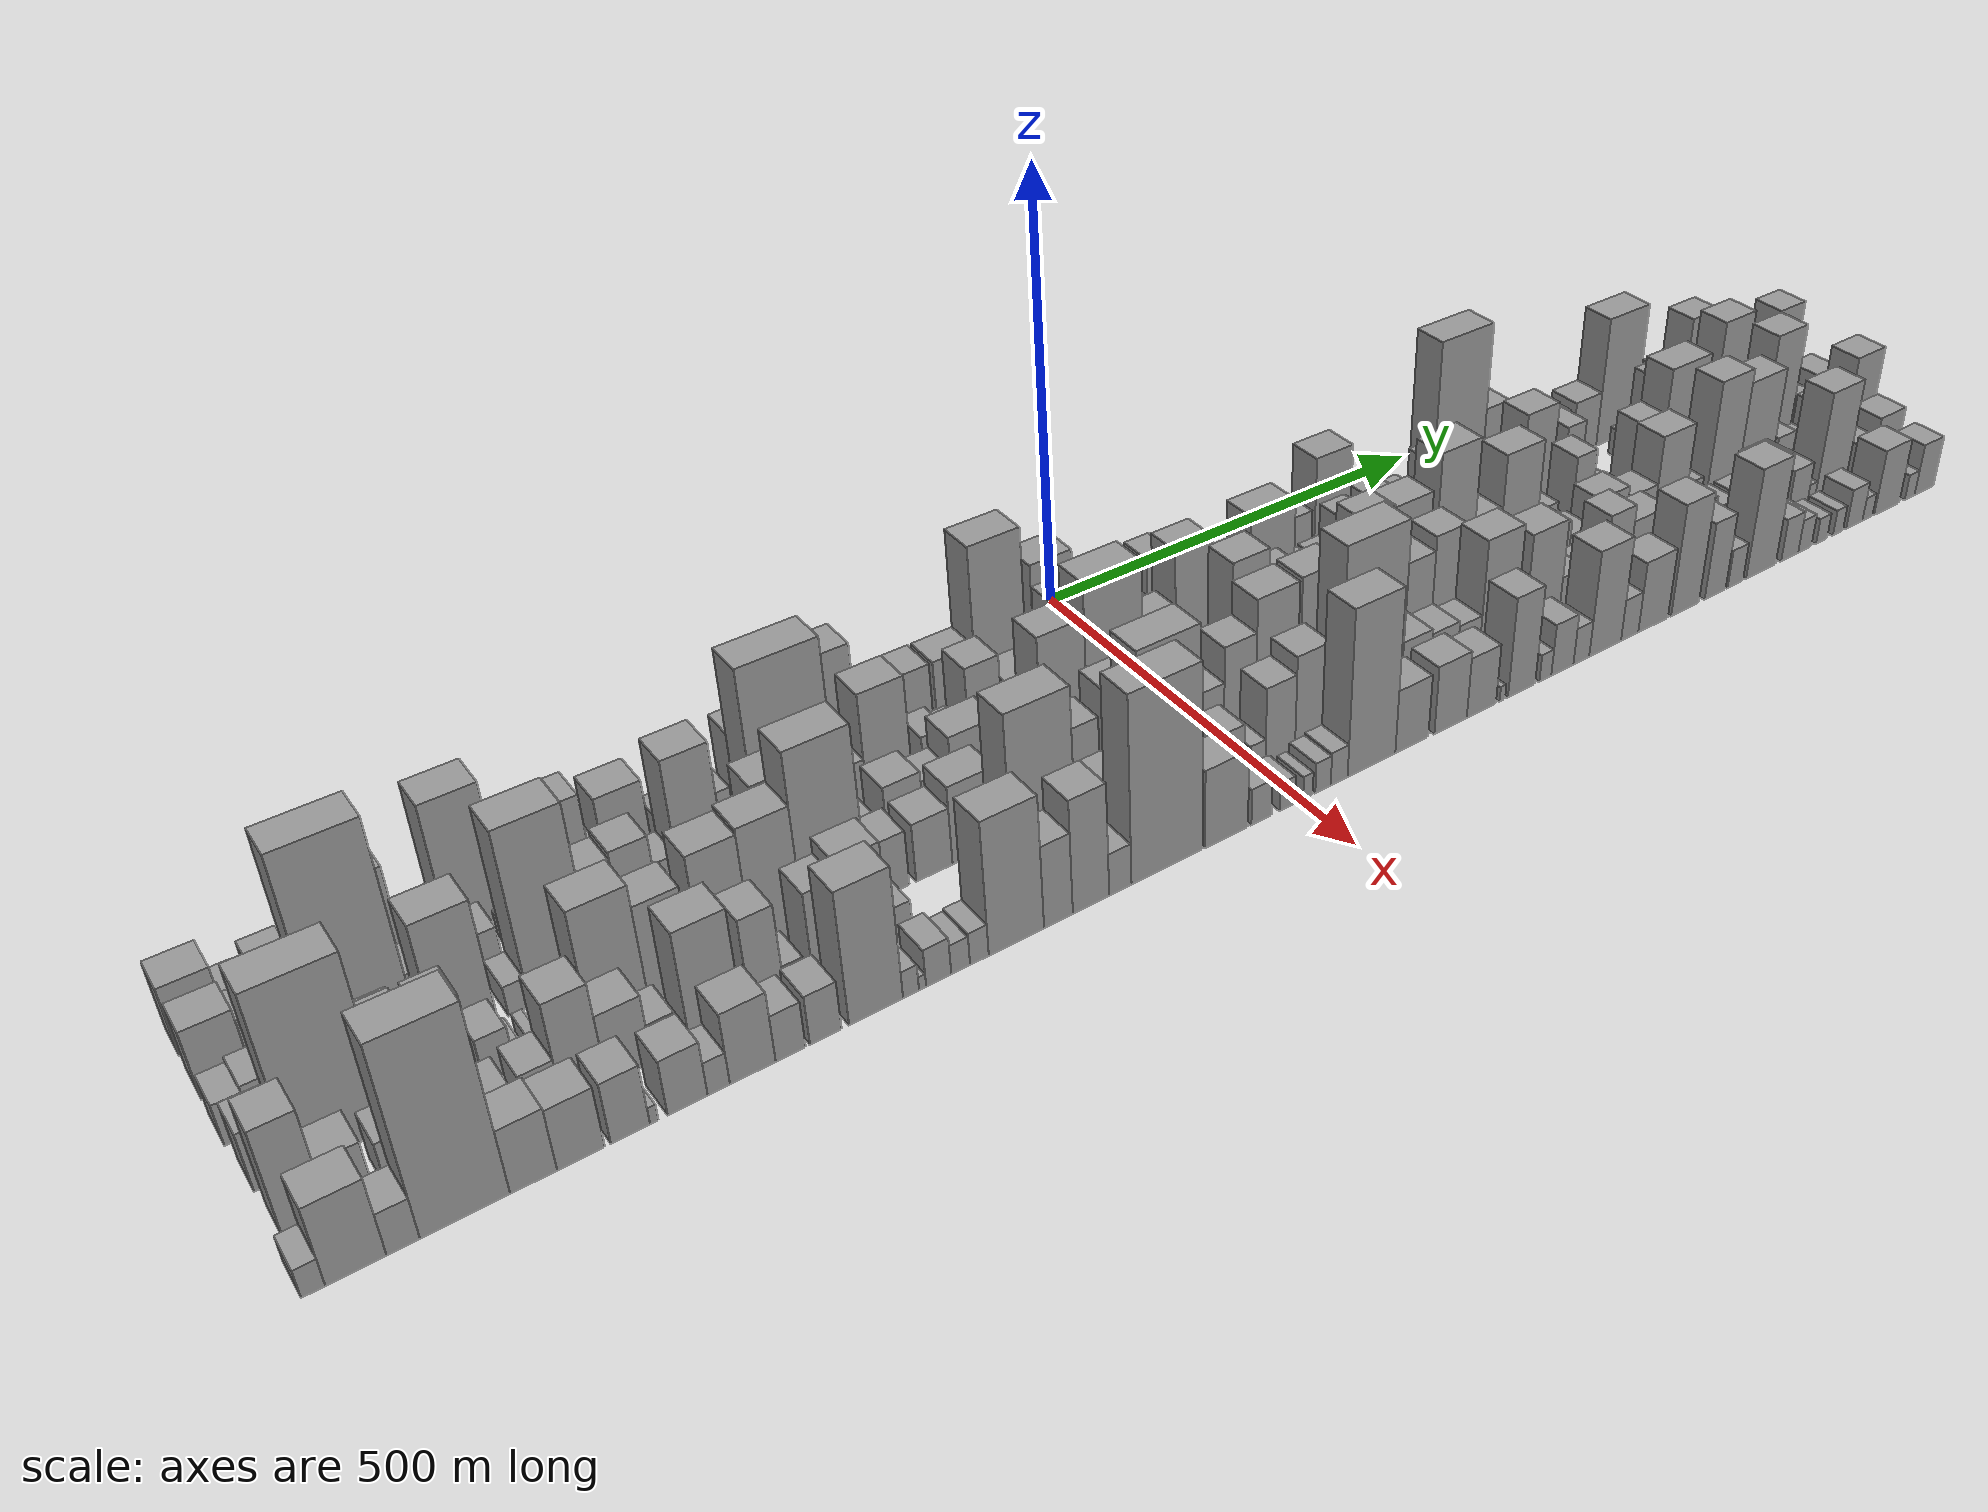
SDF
<sdf version="1.6">
 <world name="default">
  <scene>
   <sky><clouds><speed>12</speed></clouds></sky>
   <ambient>0.4 0.4 0.4 1</ambient>
   <background>0.7 0.7 0.7 1</background>
   <shadows>1</shadows>
  </scene>
  <gravity>0 0 -9.8066</gravity>
  <magnetic_field>6e-06 2.3e-05 -4.2e-05</magnetic_field>
  <physics default="0" name="default_physics" type="ode">
   <ode>
    <solver>
     <type>quick</type>
     <iters>10</iters>
     <sor>1.0</sor>
     <use_dynamic_moi_rescaling>0</use_dynamic_moi_rescaling>
    </solver>
    <constraints>
     <cfm>0</cfm>
     <erp>0.2</erp>
     <contact_max_correcting_vel>100</contact_max_correcting_vel>
     <contact_surface_layer>0.001</contact_surface_layer>
    </constraints>
   </ode>
   <max_step_size>0.004</max_step_size>
   <real_time_factor>1</real_time_factor>
   <real_time_update_rate>250</real_time_update_rate>
  </physics>
  <light name="sun" type="directional">
   <pose>0 0 10 0 0 0</pose>
   <diffuse>0.8 0.8 0.8 1</diffuse>
   <specular>0.2 0.2 0.2 1</specular>
   <attenuation>
    <range>1000</range>
    <constant>0.9</constant>
    <linear>0.01</linear>
    <quadratic>0.001</quadratic>
   </attenuation>
   <direction>-0.5 0.1 -0.9</direction>
  </light>
  <model name="building_1">
   <static>1</static>
   <pose>100.0000 -918.9162 0 0.000000 0.000000 0.000000</pose>
   <link name="link">
    <pose>0 0 37.50 0 0 0</pose>
    <collision name="collision"><geometry><box><size>40.0000 42.1676 75.0000</size></box></geometry></collision>
    <visual name="visual">
     <cast_shadows>0</cast_shadows>
     <geometry><box><size>40.0000 42.1676 75.0000</size></box></geometry>
     <material>
      <script>
       <uri>model://grey_wall/materials/scripts</uri>
       <uri>model://grey_wall/materials/textures</uri>
       <name>vrc/grey_wall</name>
      </script>
     </material>
    </visual>
   </link>
  </model>
  <model name="building_2">
   <static>1</static>
   <pose>100.0000 -886.9073 0 0.000000 0.000000 0.000000</pose>
   <link name="link">
    <pose>0 0 21.00 0 0 0</pose>
    <collision name="collision"><geometry><box><size>40.0000 21.8500 42.0000</size></box></geometry></collision>
    <visual name="visual">
     <cast_shadows>0</cast_shadows>
     <geometry><box><size>40.0000 21.8500 42.0000</size></box></geometry>
     <material>
      <script>
       <uri>model://grey_wall/materials/scripts</uri>
       <uri>model://grey_wall/materials/textures</uri>
       <name>vrc/grey_wall</name>
      </script>
     </material>
    </visual>
   </link>
  </model>
  <model name="building_3">
   <static>1</static>
   <pose>100.0000 -852.5298 0 0.000000 0.000000 0.000000</pose>
   <link name="link">
    <pose>0 0 28.50 0 0 0</pose>
    <collision name="collision"><geometry><box><size>40.0000 32.9050 57.0000</size></box></geometry></collision>
    <visual name="visual">
     <cast_shadows>0</cast_shadows>
     <geometry><box><size>40.0000 32.9050 57.0000</size></box></geometry>
     <material>
      <script>
       <uri>model://grey_wall/materials/scripts</uri>
       <uri>model://grey_wall/materials/textures</uri>
       <name>vrc/grey_wall</name>
      </script>
     </material>
    </visual>
   </link>
  </model>
  <model name="building_4">
   <static>1</static>
   <pose>100.0000 -819.8504 0 0.000000 0.000000 0.000000</pose>
   <link name="link">
    <pose>0 0 21.00 0 0 0</pose>
    <collision name="collision"><geometry><box><size>40.0000 24.4538 42.0000</size></box></geometry></collision>
    <visual name="visual">
     <cast_shadows>0</cast_shadows>
     <geometry><box><size>40.0000 24.4538 42.0000</size></box></geometry>
     <material>
      <script>
       <uri>model://grey_wall/materials/scripts</uri>
       <uri>model://grey_wall/materials/textures</uri>
       <name>vrc/grey_wall</name>
      </script>
     </material>
    </visual>
   </link>
  </model>
  <model name="building_5">
   <static>1</static>
   <pose>100.0000 -794.7699 0 0.000000 0.000000 0.000000</pose>
   <link name="link">
    <pose>0 0 9.00 0 0 0</pose>
    <collision name="collision"><geometry><box><size>40.0000 7.7071 18.0000</size></box></geometry></collision>
    <visual name="visual">
     <cast_shadows>0</cast_shadows>
     <geometry><box><size>40.0000 7.7071 18.0000</size></box></geometry>
     <material>
      <script>
       <uri>model://grey_wall/materials/scripts</uri>
       <uri>model://grey_wall/materials/textures</uri>
       <name>vrc/grey_wall</name>
      </script>
     </material>
    </visual>
   </link>
  </model>
  <model name="building_6">
   <static>1</static>
   <pose>100.0000 -770.6630 0 0.000000 0.000000 0.000000</pose>
   <link name="link">
    <pose>0 0 52.50 0 0 0</pose>
    <collision name="collision"><geometry><box><size>40.0000 40.5068 105.0000</size></box></geometry></collision>
    <visual name="visual">
     <cast_shadows>0</cast_shadows>
     <geometry><box><size>40.0000 40.5068 105.0000</size></box></geometry>
     <material>
      <script>
       <uri>model://grey_wall/materials/scripts</uri>
       <uri>model://grey_wall/materials/textures</uri>
       <name>vrc/grey_wall</name>
      </script>
     </material>
    </visual>
   </link>
  </model>
  <model name="building_7">
   <static>1</static>
   <pose>100.0000 -730.7436 0 0.000000 0.000000 0.000000</pose>
   <link name="link">
    <pose>0 0 18.00 0 0 0</pose>
    <collision name="collision"><geometry><box><size>40.0000 19.3318 36.0000</size></box></geometry></collision>
    <visual name="visual">
     <cast_shadows>0</cast_shadows>
     <geometry><box><size>40.0000 19.3318 36.0000</size></box></geometry>
     <material>
      <script>
       <uri>model://grey_wall/materials/scripts</uri>
       <uri>model://grey_wall/materials/textures</uri>
       <name>vrc/grey_wall</name>
      </script>
     </material>
    </visual>
   </link>
  </model>
  <model name="building_8">
   <static>1</static>
   <pose>100.0000 -684.5508 0 0.000000 0.000000 0.000000</pose>
   <link name="link">
    <pose>0 0 75.00 0 0 0</pose>
    <collision name="collision"><geometry><box><size>40.0000 53.0539 150.0000</size></box></geometry></collision>
    <visual name="visual">
     <cast_shadows>0</cast_shadows>
     <geometry><box><size>40.0000 53.0539 150.0000</size></box></geometry>
     <material>
      <script>
       <uri>model://grey_wall/materials/scripts</uri>
       <uri>model://grey_wall/materials/textures</uri>
       <name>vrc/grey_wall</name>
      </script>
     </material>
    </visual>
   </link>
  </model>
  <model name="building_9">
   <static>1</static>
   <pose>100.0000 -635.3252 0 0.000000 0.000000 0.000000</pose>
   <link name="link">
    <pose>0 0 30.00 0 0 0</pose>
    <collision name="collision"><geometry><box><size>40.0000 31.3972 60.0000</size></box></geometry></collision>
    <visual name="visual">
     <cast_shadows>0</cast_shadows>
     <geometry><box><size>40.0000 31.3972 60.0000</size></box></geometry>
     <material>
      <script>
       <uri>model://grey_wall/materials/scripts</uri>
       <uri>model://grey_wall/materials/textures</uri>
       <name>vrc/grey_wall</name>
      </script>
     </material>
    </visual>
   </link>
  </model>
  <model name="building_10">
   <static>1</static>
   <pose>100.0000 -595.2459 0 0.000000 0.000000 0.000000</pose>
   <link name="link">
    <pose>0 0 48.00 0 0 0</pose>
    <collision name="collision"><geometry><box><size>40.0000 36.7615 96.0000</size></box></geometry></collision>
    <visual name="visual">
     <cast_shadows>0</cast_shadows>
     <geometry><box><size>40.0000 36.7615 96.0000</size></box></geometry>
     <material>
      <script>
       <uri>model://grey_wall/materials/scripts</uri>
       <uri>model://grey_wall/materials/textures</uri>
       <name>vrc/grey_wall</name>
      </script>
     </material>
    </visual>
   </link>
  </model>
  <model name="building_11">
   <static>1</static>
   <pose>100.0000 -570.7395 0 0.000000 0.000000 0.000000</pose>
   <link name="link">
    <pose>0 0 13.50 0 0 0</pose>
    <collision name="collision"><geometry><box><size>40.0000 12.2513 27.0000</size></box></geometry></collision>
    <visual name="visual">
     <cast_shadows>0</cast_shadows>
     <geometry><box><size>40.0000 12.2513 27.0000</size></box></geometry>
     <material>
      <script>
       <uri>model://grey_wall/materials/scripts</uri>
       <uri>model://grey_wall/materials/textures</uri>
       <name>vrc/grey_wall</name>
      </script>
     </material>
    </visual>
   </link>
  </model>
  <model name="building_12">
   <static>1</static>
   <pose>100.0000 -541.9310 0 0.000000 0.000000 0.000000</pose>
   <link name="link">
    <pose>0 0 42.00 0 0 0</pose>
    <collision name="collision"><geometry><box><size>40.0000 45.3656 84.0000</size></box></geometry></collision>
    <visual name="visual">
     <cast_shadows>0</cast_shadows>
     <geometry><box><size>40.0000 45.3656 84.0000</size></box></geometry>
     <material>
      <script>
       <uri>model://grey_wall/materials/scripts</uri>
       <uri>model://grey_wall/materials/textures</uri>
       <name>vrc/grey_wall</name>
      </script>
     </material>
    </visual>
   </link>
  </model>
  <model name="building_13">
   <static>1</static>
   <pose>100.0000 -501.1030 0 0.000000 0.000000 0.000000</pose>
   <link name="link">
    <pose>0 0 16.50 0 0 0</pose>
    <collision name="collision"><geometry><box><size>40.0000 18.2905 33.0000</size></box></geometry></collision>
    <visual name="visual">
     <cast_shadows>0</cast_shadows>
     <geometry><box><size>40.0000 18.2905 33.0000</size></box></geometry>
     <material>
      <script>
       <uri>model://grey_wall/materials/scripts</uri>
       <uri>model://grey_wall/materials/textures</uri>
       <name>vrc/grey_wall</name>
      </script>
     </material>
    </visual>
   </link>
  </model>
  <model name="building_14">
   <static>1</static>
   <pose>100.0000 -474.0762 0 0.000000 0.000000 0.000000</pose>
   <link name="link">
    <pose>0 0 46.50 0 0 0</pose>
    <collision name="collision"><geometry><box><size>40.0000 35.7632 93.0000</size></box></geometry></collision>
    <visual name="visual">
     <cast_shadows>0</cast_shadows>
     <geometry><box><size>40.0000 35.7632 93.0000</size></box></geometry>
     <material>
      <script>
       <uri>model://grey_wall/materials/scripts</uri>
       <uri>model://grey_wall/materials/textures</uri>
       <name>vrc/grey_wall</name>
      </script>
     </material>
    </visual>
   </link>
  </model>
  <model name="building_15">
   <static>1</static>
   <pose>100.0000 -446.9573 0 0.000000 0.000000 0.000000</pose>
   <link name="link">
    <pose>0 0 18.00 0 0 0</pose>
    <collision name="collision"><geometry><box><size>40.0000 18.4745 36.0000</size></box></geometry></collision>
    <visual name="visual">
     <cast_shadows>0</cast_shadows>
     <geometry><box><size>40.0000 18.4745 36.0000</size></box></geometry>
     <material>
      <script>
       <uri>model://grey_wall/materials/scripts</uri>
       <uri>model://grey_wall/materials/textures</uri>
       <name>vrc/grey_wall</name>
      </script>
     </material>
    </visual>
   </link>
  </model>
  <model name="building_16">
   <static>1</static>
   <pose>100.0000 -414.3476 0 0.000000 0.000000 0.000000</pose>
   <link name="link">
    <pose>0 0 46.50 0 0 0</pose>
    <collision name="collision"><geometry><box><size>40.0000 34.7451 93.0000</size></box></geometry></collision>
    <visual name="visual">
     <cast_shadows>0</cast_shadows>
     <geometry><box><size>40.0000 34.7451 93.0000</size></box></geometry>
     <material>
      <script>
       <uri>model://grey_wall/materials/scripts</uri>
       <uri>model://grey_wall/materials/textures</uri>
       <name>vrc/grey_wall</name>
      </script>
     </material>
    </visual>
   </link>
  </model>
  <model name="building_17">
   <static>1</static>
   <pose>100.0000 -374.5045 0 0.000000 0.000000 0.000000</pose>
   <link name="link">
    <pose>0 0 42.00 0 0 0</pose>
    <collision name="collision"><geometry><box><size>40.0000 44.9411 84.0000</size></box></geometry></collision>
    <visual name="visual">
     <cast_shadows>0</cast_shadows>
     <geometry><box><size>40.0000 44.9411 84.0000</size></box></geometry>
     <material>
      <script>
       <uri>model://grey_wall/materials/scripts</uri>
       <uri>model://grey_wall/materials/textures</uri>
       <name>vrc/grey_wall</name>
      </script>
     </material>
    </visual>
   </link>
  </model>
  <model name="building_18">
   <static>1</static>
   <pose>100.0000 -326.9662 0 0.000000 0.000000 0.000000</pose>
   <link name="link">
    <pose>0 0 70.50 0 0 0</pose>
    <collision name="collision"><geometry><box><size>40.0000 50.1355 141.0000</size></box></geometry></collision>
    <visual name="visual">
     <cast_shadows>0</cast_shadows>
     <geometry><box><size>40.0000 50.1355 141.0000</size></box></geometry>
     <material>
      <script>
       <uri>model://grey_wall/materials/scripts</uri>
       <uri>model://grey_wall/materials/textures</uri>
       <name>vrc/grey_wall</name>
      </script>
     </material>
    </visual>
   </link>
  </model>
  <model name="building_19">
   <static>1</static>
   <pose>100.0000 -282.4072 0 0.000000 0.000000 0.000000</pose>
   <link name="link">
    <pose>0 0 33.00 0 0 0</pose>
    <collision name="collision"><geometry><box><size>40.0000 38.9824 66.0000</size></box></geometry></collision>
    <visual name="visual">
     <cast_shadows>0</cast_shadows>
     <geometry><box><size>40.0000 38.9824 66.0000</size></box></geometry>
     <material>
      <script>
       <uri>model://grey_wall/materials/scripts</uri>
       <uri>model://grey_wall/materials/textures</uri>
       <name>vrc/grey_wall</name>
      </script>
     </material>
    </visual>
   </link>
  </model>
  <model name="building_20">
   <static>1</static>
   <pose>100.0000 -241.3646 0 0.000000 0.000000 0.000000</pose>
   <link name="link">
    <pose>0 0 40.50 0 0 0</pose>
    <collision name="collision"><geometry><box><size>40.0000 43.1028 81.0000</size></box></geometry></collision>
    <visual name="visual">
     <cast_shadows>0</cast_shadows>
     <geometry><box><size>40.0000 43.1028 81.0000</size></box></geometry>
     <material>
      <script>
       <uri>model://grey_wall/materials/scripts</uri>
       <uri>model://grey_wall/materials/textures</uri>
       <name>vrc/grey_wall</name>
      </script>
     </material>
    </visual>
   </link>
  </model>
  <model name="building_21">
   <static>1</static>
   <pose>100.0000 -192.4322 0 0.000000 0.000000 0.000000</pose>
   <link name="link">
    <pose>0 0 40.50 0 0 0</pose>
    <collision name="collision"><geometry><box><size>40.0000 46.7620 81.0000</size></box></geometry></collision>
    <visual name="visual">
     <cast_shadows>0</cast_shadows>
     <geometry><box><size>40.0000 46.7620 81.0000</size></box></geometry>
     <material>
      <script>
       <uri>model://grey_wall/materials/scripts</uri>
       <uri>model://grey_wall/materials/textures</uri>
       <name>vrc/grey_wall</name>
      </script>
     </material>
    </visual>
   </link>
  </model>
  <model name="building_22">
   <static>1</static>
   <pose>100.0000 -139.3016 0 0.000000 0.000000 0.000000</pose>
   <link name="link">
    <pose>0 0 97.50 0 0 0</pose>
    <collision name="collision"><geometry><box><size>40.0000 59.4992 195.0000</size></box></geometry></collision>
    <visual name="visual">
     <cast_shadows>0</cast_shadows>
     <geometry><box><size>40.0000 59.4992 195.0000</size></box></geometry>
     <material>
      <script>
       <uri>model://grey_wall/materials/scripts</uri>
       <uri>model://grey_wall/materials/textures</uri>
       <name>vrc/grey_wall</name>
      </script>
     </material>
    </visual>
   </link>
  </model>
  <model name="building_23">
   <static>1</static>
   <pose>100.0000 -75.8949 0 0.000000 0.000000 0.000000</pose>
   <link name="link">
    <pose>0 0 73.50 0 0 0</pose>
    <collision name="collision"><geometry><box><size>40.0000 49.3142 147.0000</size></box></geometry></collision>
    <visual name="visual">
     <cast_shadows>0</cast_shadows>
     <geometry><box><size>40.0000 49.3142 147.0000</size></box></geometry>
     <material>
      <script>
       <uri>model://grey_wall/materials/scripts</uri>
       <uri>model://grey_wall/materials/textures</uri>
       <name>vrc/grey_wall</name>
      </script>
     </material>
    </visual>
   </link>
  </model>
  <model name="building_24">
   <static>1</static>
   <pose>100.0000 -21.9585 0 0.000000 0.000000 0.000000</pose>
   <link name="link">
    <pose>0 0 36.00 0 0 0</pose>
    <collision name="collision"><geometry><box><size>40.0000 38.5585 72.0000</size></box></geometry></collision>
    <visual name="visual">
     <cast_shadows>0</cast_shadows>
     <geometry><box><size>40.0000 38.5585 72.0000</size></box></geometry>
     <material>
      <script>
       <uri>model://grey_wall/materials/scripts</uri>
       <uri>model://grey_wall/materials/textures</uri>
       <name>vrc/grey_wall</name>
      </script>
     </material>
    </visual>
   </link>
  </model>
  <model name="building_25">
   <static>1</static>
   <pose>100.0000 1.7301 0 0.000000 0.000000 0.000000</pose>
   <link name="link">
    <pose>0 0 10.50 0 0 0</pose>
    <collision name="collision"><geometry><box><size>40.0000 8.8189 21.0000</size></box></geometry></collision>
    <visual name="visual">
     <cast_shadows>0</cast_shadows>
     <geometry><box><size>40.0000 8.8189 21.0000</size></box></geometry>
     <material>
      <script>
       <uri>model://grey_wall/materials/scripts</uri>
       <uri>model://grey_wall/materials/textures</uri>
       <name>vrc/grey_wall</name>
      </script>
     </material>
    </visual>
   </link>
  </model>
  <model name="building_26">
   <static>1</static>
   <pose>100.0000 24.4801 0 0.000000 0.000000 0.000000</pose>
   <link name="link">
    <pose>0 0 27.00 0 0 0</pose>
    <collision name="collision"><geometry><box><size>40.0000 30.6811 54.0000</size></box></geometry></collision>
    <visual name="visual">
     <cast_shadows>0</cast_shadows>
     <geometry><box><size>40.0000 30.6811 54.0000</size></box></geometry>
     <material>
      <script>
       <uri>model://grey_wall/materials/scripts</uri>
       <uri>model://grey_wall/materials/textures</uri>
       <name>vrc/grey_wall</name>
      </script>
     </material>
    </visual>
   </link>
  </model>
  <model name="building_27">
   <static>1</static>
   <pose>100.0000 55.2419 0 0.000000 0.000000 0.000000</pose>
   <link name="link">
    <pose>0 0 49.50 0 0 0</pose>
    <collision name="collision"><geometry><box><size>40.0000 30.8425 99.0000</size></box></geometry></collision>
    <visual name="visual">
     <cast_shadows>0</cast_shadows>
     <geometry><box><size>40.0000 30.8425 99.0000</size></box></geometry>
     <material>
      <script>
       <uri>model://grey_wall/materials/scripts</uri>
       <uri>model://grey_wall/materials/textures</uri>
       <name>vrc/grey_wall</name>
      </script>
     </material>
    </visual>
   </link>
  </model>
  <model name="building_28">
   <static>1</static>
   <pose>100.0000 79.9134 0 0.000000 0.000000 0.000000</pose>
   <link name="link">
    <pose>0 0 18.00 0 0 0</pose>
    <collision name="collision"><geometry><box><size>40.0000 18.5005 36.0000</size></box></geometry></collision>
    <visual name="visual">
     <cast_shadows>0</cast_shadows>
     <geometry><box><size>40.0000 18.5005 36.0000</size></box></geometry>
     <material>
      <script>
       <uri>model://grey_wall/materials/scripts</uri>
       <uri>model://grey_wall/materials/textures</uri>
       <name>vrc/grey_wall</name>
      </script>
     </material>
    </visual>
   </link>
  </model>
  <model name="building_29">
   <static>1</static>
   <pose>100.0000 116.2037 0 0.000000 0.000000 0.000000</pose>
   <link name="link">
    <pose>0 0 37.50 0 0 0</pose>
    <collision name="collision"><geometry><box><size>40.0000 38.0802 75.0000</size></box></geometry></collision>
    <visual name="visual">
     <cast_shadows>0</cast_shadows>
     <geometry><box><size>40.0000 38.0802 75.0000</size></box></geometry>
     <material>
      <script>
       <uri>model://grey_wall/materials/scripts</uri>
       <uri>model://grey_wall/materials/textures</uri>
       <name>vrc/grey_wall</name>
      </script>
     </material>
    </visual>
   </link>
  </model>
  <model name="building_30">
   <static>1</static>
   <pose>100.0000 147.2831 0 0.000000 0.000000 0.000000</pose>
   <link name="link">
    <pose>0 0 21.00 0 0 0</pose>
    <collision name="collision"><geometry><box><size>40.0000 24.0786 42.0000</size></box></geometry></collision>
    <visual name="visual">
     <cast_shadows>0</cast_shadows>
     <geometry><box><size>40.0000 24.0786 42.0000</size></box></geometry>
     <material>
      <script>
       <uri>model://grey_wall/materials/scripts</uri>
       <uri>model://grey_wall/materials/textures</uri>
       <name>vrc/grey_wall</name>
      </script>
     </material>
    </visual>
   </link>
  </model>
  <model name="building_31">
   <static>1</static>
   <pose>100.0000 170.0176 0 0.000000 0.000000 0.000000</pose>
   <link name="link">
    <pose>0 0 21.00 0 0 0</pose>
    <collision name="collision"><geometry><box><size>40.0000 21.3902 42.0000</size></box></geometry></collision>
    <visual name="visual">
     <cast_shadows>0</cast_shadows>
     <geometry><box><size>40.0000 21.3902 42.0000</size></box></geometry>
     <material>
      <script>
       <uri>model://grey_wall/materials/scripts</uri>
       <uri>model://grey_wall/materials/textures</uri>
       <name>vrc/grey_wall</name>
      </script>
     </material>
    </visual>
   </link>
  </model>
  <model name="building_32">
   <static>1</static>
   <pose>100.0000 201.4124 0 0.000000 0.000000 0.000000</pose>
   <link name="link">
    <pose>0 0 30.00 0 0 0</pose>
    <collision name="collision"><geometry><box><size>40.0000 35.3995 60.0000</size></box></geometry></collision>
    <visual name="visual">
     <cast_shadows>0</cast_shadows>
     <geometry><box><size>40.0000 35.3995 60.0000</size></box></geometry>
     <material>
      <script>
       <uri>model://grey_wall/materials/scripts</uri>
       <uri>model://grey_wall/materials/textures</uri>
       <name>vrc/grey_wall</name>
      </script>
     </material>
    </visual>
   </link>
  </model>
  <model name="building_33">
   <static>1</static>
   <pose>100.0000 239.0206 0 0.000000 0.000000 0.000000</pose>
   <link name="link">
    <pose>0 0 37.50 0 0 0</pose>
    <collision name="collision"><geometry><box><size>40.0000 39.8168 75.0000</size></box></geometry></collision>
    <visual name="visual">
     <cast_shadows>0</cast_shadows>
     <geometry><box><size>40.0000 39.8168 75.0000</size></box></geometry>
     <material>
      <script>
       <uri>model://grey_wall/materials/scripts</uri>
       <uri>model://grey_wall/materials/textures</uri>
       <name>vrc/grey_wall</name>
      </script>
     </material>
    </visual>
   </link>
  </model>
  <model name="building_34">
   <static>1</static>
   <pose>100.0000 288.0815 0 0.000000 0.000000 0.000000</pose>
   <link name="link">
    <pose>0 0 69.00 0 0 0</pose>
    <collision name="collision"><geometry><box><size>40.0000 50.3052 138.0000</size></box></geometry></collision>
    <visual name="visual">
     <cast_shadows>0</cast_shadows>
     <geometry><box><size>40.0000 50.3052 138.0000</size></box></geometry>
     <material>
      <script>
       <uri>model://grey_wall/materials/scripts</uri>
       <uri>model://grey_wall/materials/textures</uri>
       <name>vrc/grey_wall</name>
      </script>
     </material>
    </visual>
   </link>
  </model>
  <model name="building_35">
   <static>1</static>
   <pose>100.0000 323.0292 0 0.000000 0.000000 0.000000</pose>
   <link name="link">
    <pose>0 0 16.50 0 0 0</pose>
    <collision name="collision"><geometry><box><size>40.0000 19.5901 33.0000</size></box></geometry></collision>
    <visual name="visual">
     <cast_shadows>0</cast_shadows>
     <geometry><box><size>40.0000 19.5901 33.0000</size></box></geometry>
     <material>
      <script>
       <uri>model://grey_wall/materials/scripts</uri>
       <uri>model://grey_wall/materials/textures</uri>
       <name>vrc/grey_wall</name>
      </script>
     </material>
    </visual>
   </link>
  </model>
  <model name="building_36">
   <static>1</static>
   <pose>100.0000 350.8618 0 0.000000 0.000000 0.000000</pose>
   <link name="link">
    <pose>0 0 34.50 0 0 0</pose>
    <collision name="collision"><geometry><box><size>40.0000 36.0752 69.0000</size></box></geometry></collision>
    <visual name="visual">
     <cast_shadows>0</cast_shadows>
     <geometry><box><size>40.0000 36.0752 69.0000</size></box></geometry>
     <material>
      <script>
       <uri>model://grey_wall/materials/scripts</uri>
       <uri>model://grey_wall/materials/textures</uri>
       <name>vrc/grey_wall</name>
      </script>
     </material>
    </visual>
   </link>
  </model>
  <model name="building_37">
   <static>1</static>
   <pose>100.0000 379.1354 0 0.000000 0.000000 0.000000</pose>
   <link name="link">
    <pose>0 0 7.50 0 0 0</pose>
    <collision name="collision"><geometry><box><size>40.0000 6.4720 15.0000</size></box></geometry></collision>
    <visual name="visual">
     <cast_shadows>0</cast_shadows>
     <geometry><box><size>40.0000 6.4720 15.0000</size></box></geometry>
     <material>
      <script>
       <uri>model://grey_wall/materials/scripts</uri>
       <uri>model://grey_wall/materials/textures</uri>
       <name>vrc/grey_wall</name>
      </script>
     </material>
    </visual>
   </link>
  </model>
  <model name="building_38">
   <static>1</static>
   <pose>100.0000 403.4569 0 0.000000 0.000000 0.000000</pose>
   <link name="link">
    <pose>0 0 22.50 0 0 0</pose>
    <collision name="collision"><geometry><box><size>40.0000 24.1709 45.0000</size></box></geometry></collision>
    <visual name="visual">
     <cast_shadows>0</cast_shadows>
     <geometry><box><size>40.0000 24.1709 45.0000</size></box></geometry>
     <material>
      <script>
       <uri>model://grey_wall/materials/scripts</uri>
       <uri>model://grey_wall/materials/textures</uri>
       <name>vrc/grey_wall</name>
      </script>
     </material>
    </visual>
   </link>
  </model>
  <model name="building_39">
   <static>1</static>
   <pose>100.0000 419.2504 0 0.000000 0.000000 0.000000</pose>
   <link name="link">
    <pose>0 0 9.00 0 0 0</pose>
    <collision name="collision"><geometry><box><size>40.0000 7.4161 18.0000</size></box></geometry></collision>
    <visual name="visual">
     <cast_shadows>0</cast_shadows>
     <geometry><box><size>40.0000 7.4161 18.0000</size></box></geometry>
     <material>
      <script>
       <uri>model://grey_wall/materials/scripts</uri>
       <uri>model://grey_wall/materials/textures</uri>
       <name>vrc/grey_wall</name>
      </script>
     </material>
    </visual>
   </link>
  </model>
  <model name="building_40">
   <static>1</static>
   <pose>100.0000 430.4653 0 0.000000 0.000000 0.000000</pose>
   <link name="link">
    <pose>0 0 10.50 0 0 0</pose>
    <collision name="collision"><geometry><box><size>40.0000 9.0136 21.0000</size></box></geometry></collision>
    <visual name="visual">
     <cast_shadows>0</cast_shadows>
     <geometry><box><size>40.0000 9.0136 21.0000</size></box></geometry>
     <material>
      <script>
       <uri>model://grey_wall/materials/scripts</uri>
       <uri>model://grey_wall/materials/textures</uri>
       <name>vrc/grey_wall</name>
      </script>
     </material>
    </visual>
   </link>
  </model>
  <model name="building_41">
   <static>1</static>
   <pose>100.0000 472.8589 0 0.000000 0.000000 0.000000</pose>
   <link name="link">
    <pose>0 0 111.00 0 0 0</pose>
    <collision name="collision"><geometry><box><size>40.0000 75.7737 222.0000</size></box></geometry></collision>
    <visual name="visual">
     <cast_shadows>0</cast_shadows>
     <geometry><box><size>40.0000 75.7737 222.0000</size></box></geometry>
     <material>
      <script>
       <uri>model://grey_wall/materials/scripts</uri>
       <uri>model://grey_wall/materials/textures</uri>
       <name>vrc/grey_wall</name>
      </script>
     </material>
    </visual>
   </link>
  </model>
  <model name="building_42">
   <static>1</static>
   <pose>100.0000 529.0501 0 0.000000 0.000000 0.000000</pose>
   <link name="link">
    <pose>0 0 57.00 0 0 0</pose>
    <collision name="collision"><geometry><box><size>40.0000 36.6088 114.0000</size></box></geometry></collision>
    <visual name="visual">
     <cast_shadows>0</cast_shadows>
     <geometry><box><size>40.0000 36.6088 114.0000</size></box></geometry>
     <material>
      <script>
       <uri>model://grey_wall/materials/scripts</uri>
       <uri>model://grey_wall/materials/textures</uri>
       <name>vrc/grey_wall</name>
      </script>
     </material>
    </visual>
   </link>
  </model>
  <model name="building_43">
   <static>1</static>
   <pose>100.0000 557.8874 0 0.000000 0.000000 0.000000</pose>
   <link name="link">
    <pose>0 0 18.00 0 0 0</pose>
    <collision name="collision"><geometry><box><size>40.0000 21.0658 36.0000</size></box></geometry></collision>
    <visual name="visual">
     <cast_shadows>0</cast_shadows>
     <geometry><box><size>40.0000 21.0658 36.0000</size></box></geometry>
     <material>
      <script>
       <uri>model://grey_wall/materials/scripts</uri>
       <uri>model://grey_wall/materials/textures</uri>
       <name>vrc/grey_wall</name>
      </script>
     </material>
    </visual>
   </link>
  </model>
  <model name="building_44">
   <static>1</static>
   <pose>100.0000 591.2892 0 0.000000 0.000000 0.000000</pose>
   <link name="link">
    <pose>0 0 34.50 0 0 0</pose>
    <collision name="collision"><geometry><box><size>40.0000 37.7379 69.0000</size></box></geometry></collision>
    <visual name="visual">
     <cast_shadows>0</cast_shadows>
     <geometry><box><size>40.0000 37.7379 69.0000</size></box></geometry>
     <material>
      <script>
       <uri>model://grey_wall/materials/scripts</uri>
       <uri>model://grey_wall/materials/textures</uri>
       <name>vrc/grey_wall</name>
      </script>
     </material>
    </visual>
   </link>
  </model>
  <model name="building_45">
   <static>1</static>
   <pose>100.0000 632.4907 0 0.000000 0.000000 0.000000</pose>
   <link name="link">
    <pose>0 0 33.00 0 0 0</pose>
    <collision name="collision"><geometry><box><size>40.0000 34.6652 66.0000</size></box></geometry></collision>
    <visual name="visual">
     <cast_shadows>0</cast_shadows>
     <geometry><box><size>40.0000 34.6652 66.0000</size></box></geometry>
     <material>
      <script>
       <uri>model://grey_wall/materials/scripts</uri>
       <uri>model://grey_wall/materials/textures</uri>
       <name>vrc/grey_wall</name>
      </script>
     </material>
    </visual>
   </link>
  </model>
  <model name="building_46">
   <static>1</static>
   <pose>100.0000 654.2675 0 0.000000 0.000000 0.000000</pose>
   <link name="link">
    <pose>0 0 10.50 0 0 0</pose>
    <collision name="collision"><geometry><box><size>40.0000 8.8883 21.0000</size></box></geometry></collision>
    <visual name="visual">
     <cast_shadows>0</cast_shadows>
     <geometry><box><size>40.0000 8.8883 21.0000</size></box></geometry>
     <material>
      <script>
       <uri>model://grey_wall/materials/scripts</uri>
       <uri>model://grey_wall/materials/textures</uri>
       <name>vrc/grey_wall</name>
      </script>
     </material>
    </visual>
   </link>
  </model>
  <model name="building_47">
   <static>1</static>
   <pose>100.0000 679.5916 0 0.000000 0.000000 0.000000</pose>
   <link name="link">
    <pose>0 0 36.00 0 0 0</pose>
    <collision name="collision"><geometry><box><size>40.0000 41.7601 72.0000</size></box></geometry></collision>
    <visual name="visual">
     <cast_shadows>0</cast_shadows>
     <geometry><box><size>40.0000 41.7601 72.0000</size></box></geometry>
     <material>
      <script>
       <uri>model://grey_wall/materials/scripts</uri>
       <uri>model://grey_wall/materials/textures</uri>
       <name>vrc/grey_wall</name>
      </script>
     </material>
    </visual>
   </link>
  </model>
  <model name="building_48">
   <static>1</static>
   <pose>100.0000 732.7020 0 0.000000 0.000000 0.000000</pose>
   <link name="link">
    <pose>0 0 84.00 0 0 0</pose>
    <collision name="collision"><geometry><box><size>40.0000 64.4607 168.0000</size></box></geometry></collision>
    <visual name="visual">
     <cast_shadows>0</cast_shadows>
     <geometry><box><size>40.0000 64.4607 168.0000</size></box></geometry>
     <material>
      <script>
       <uri>model://grey_wall/materials/scripts</uri>
       <uri>model://grey_wall/materials/textures</uri>
       <name>vrc/grey_wall</name>
      </script>
     </material>
    </visual>
   </link>
  </model>
  <model name="building_49">
   <static>1</static>
   <pose>100.0000 776.6969 0 0.000000 0.000000 0.000000</pose>
   <link name="link">
    <pose>0 0 12.00 0 0 0</pose>
    <collision name="collision"><geometry><box><size>40.0000 11.5290 24.0000</size></box></geometry></collision>
    <visual name="visual">
     <cast_shadows>0</cast_shadows>
     <geometry><box><size>40.0000 11.5290 24.0000</size></box></geometry>
     <material>
      <script>
       <uri>model://grey_wall/materials/scripts</uri>
       <uri>model://grey_wall/materials/textures</uri>
       <name>vrc/grey_wall</name>
      </script>
     </material>
    </visual>
   </link>
  </model>
  <model name="building_50">
   <static>1</static>
   <pose>100.0000 800.5964 0 0.000000 0.000000 0.000000</pose>
   <link name="link">
    <pose>0 0 18.00 0 0 0</pose>
    <collision name="collision"><geometry><box><size>40.0000 20.2701 36.0000</size></box></geometry></collision>
    <visual name="visual">
     <cast_shadows>0</cast_shadows>
     <geometry><box><size>40.0000 20.2701 36.0000</size></box></geometry>
     <material>
      <script>
       <uri>model://grey_wall/materials/scripts</uri>
       <uri>model://grey_wall/materials/textures</uri>
       <name>vrc/grey_wall</name>
      </script>
     </material>
    </visual>
   </link>
  </model>
  <model name="building_51">
   <static>1</static>
   <pose>100.0000 830.9675 0 0.000000 0.000000 0.000000</pose>
   <link name="link">
    <pose>0 0 31.50 0 0 0</pose>
    <collision name="collision"><geometry><box><size>40.0000 34.4720 63.0000</size></box></geometry></collision>
    <visual name="visual">
     <cast_shadows>0</cast_shadows>
     <geometry><box><size>40.0000 34.4720 63.0000</size></box></geometry>
     <material>
      <script>
       <uri>model://grey_wall/materials/scripts</uri>
       <uri>model://grey_wall/materials/textures</uri>
       <name>vrc/grey_wall</name>
      </script>
     </material>
    </visual>
   </link>
  </model>
  <model name="building_52">
   <static>1</static>
   <pose>100.0000 871.3192 0 0.000000 0.000000 0.000000</pose>
   <link name="link">
    <pose>0 0 61.50 0 0 0</pose>
    <collision name="collision"><geometry><box><size>40.0000 46.2315 123.0000</size></box></geometry></collision>
    <visual name="visual">
     <cast_shadows>0</cast_shadows>
     <geometry><box><size>40.0000 46.2315 123.0000</size></box></geometry>
     <material>
      <script>
       <uri>model://grey_wall/materials/scripts</uri>
       <uri>model://grey_wall/materials/textures</uri>
       <name>vrc/grey_wall</name>
      </script>
     </material>
    </visual>
   </link>
  </model>
  <model name="building_53">
   <static>1</static>
   <pose>100.0000 914.8398 0 0.000000 0.000000 0.000000</pose>
   <link name="link">
    <pose>0 0 34.50 0 0 0</pose>
    <collision name="collision"><geometry><box><size>40.0000 40.8098 69.0000</size></box></geometry></collision>
    <visual name="visual">
     <cast_shadows>0</cast_shadows>
     <geometry><box><size>40.0000 40.8098 69.0000</size></box></geometry>
     <material>
      <script>
       <uri>model://grey_wall/materials/scripts</uri>
       <uri>model://grey_wall/materials/textures</uri>
       <name>vrc/grey_wall</name>
      </script>
     </material>
    </visual>
   </link>
  </model>
  <model name="building_54">
   <static>1</static>
   <pose>100.0000 950.6938 0 0.000000 0.000000 0.000000</pose>
   <link name="link">
    <pose>0 0 27.00 0 0 0</pose>
    <collision name="collision"><geometry><box><size>40.0000 30.8981 54.0000</size></box></geometry></collision>
    <visual name="visual">
     <cast_shadows>0</cast_shadows>
     <geometry><box><size>40.0000 30.8981 54.0000</size></box></geometry>
     <material>
      <script>
       <uri>model://grey_wall/materials/scripts</uri>
       <uri>model://grey_wall/materials/textures</uri>
       <name>vrc/grey_wall</name>
      </script>
     </material>
    </visual>
   </link>
  </model>
  <model name="building_55">
   <static>1</static>
   <pose>160.0000 -919.1313 0 0.000000 0.000000 0.000000</pose>
   <link name="link">
    <pose>0 0 37.50 0 0 0</pose>
    <collision name="collision"><geometry><box><size>40.0000 41.7373 75.0000</size></box></geometry></collision>
    <visual name="visual">
     <cast_shadows>0</cast_shadows>
     <geometry><box><size>40.0000 41.7373 75.0000</size></box></geometry>
     <material>
      <script>
       <uri>model://grey_wall/materials/scripts</uri>
       <uri>model://grey_wall/materials/textures</uri>
       <name>vrc/grey_wall</name>
      </script>
     </material>
    </visual>
   </link>
  </model>
  <model name="building_56">
   <static>1</static>
   <pose>160.0000 -881.0222 0 0.000000 0.000000 0.000000</pose>
   <link name="link">
    <pose>0 0 31.50 0 0 0</pose>
    <collision name="collision"><geometry><box><size>40.0000 34.4809 63.0000</size></box></geometry></collision>
    <visual name="visual">
     <cast_shadows>0</cast_shadows>
     <geometry><box><size>40.0000 34.4809 63.0000</size></box></geometry>
     <material>
      <script>
       <uri>model://grey_wall/materials/scripts</uri>
       <uri>model://grey_wall/materials/textures</uri>
       <name>vrc/grey_wall</name>
      </script>
     </material>
    </visual>
   </link>
  </model>
  <model name="building_57">
   <static>1</static>
   <pose>160.0000 -853.3646 0 0.000000 0.000000 0.000000</pose>
   <link name="link">
    <pose>0 0 19.50 0 0 0</pose>
    <collision name="collision"><geometry><box><size>40.0000 20.8344 39.0000</size></box></geometry></collision>
    <visual name="visual">
     <cast_shadows>0</cast_shadows>
     <geometry><box><size>40.0000 20.8344 39.0000</size></box></geometry>
     <material>
      <script>
       <uri>model://grey_wall/materials/scripts</uri>
       <uri>model://grey_wall/materials/textures</uri>
       <name>vrc/grey_wall</name>
      </script>
     </material>
    </visual>
   </link>
  </model>
  <model name="building_58">
   <static>1</static>
   <pose>160.0000 -804.7489 0 0.000000 0.000000 0.000000</pose>
   <link name="link">
    <pose>0 0 103.50 0 0 0</pose>
    <collision name="collision"><geometry><box><size>40.0000 76.3969 207.0000</size></box></geometry></collision>
    <visual name="visual">
     <cast_shadows>0</cast_shadows>
     <geometry><box><size>40.0000 76.3969 207.0000</size></box></geometry>
     <material>
      <script>
       <uri>model://grey_wall/materials/scripts</uri>
       <uri>model://grey_wall/materials/textures</uri>
       <name>vrc/grey_wall</name>
      </script>
     </material>
    </visual>
   </link>
  </model>
  <model name="building_59">
   <static>1</static>
   <pose>160.0000 -756.6857 0 0.000000 0.000000 0.000000</pose>
   <link name="link">
    <pose>0 0 18.00 0 0 0</pose>
    <collision name="collision"><geometry><box><size>40.0000 19.7295 36.0000</size></box></geometry></collision>
    <visual name="visual">
     <cast_shadows>0</cast_shadows>
     <geometry><box><size>40.0000 19.7295 36.0000</size></box></geometry>
     <material>
      <script>
       <uri>model://grey_wall/materials/scripts</uri>
       <uri>model://grey_wall/materials/textures</uri>
       <name>vrc/grey_wall</name>
      </script>
     </material>
    </visual>
   </link>
  </model>
  <model name="building_60">
   <static>1</static>
   <pose>160.0000 -729.3834 0 0.000000 0.000000 0.000000</pose>
   <link name="link">
    <pose>0 0 19.50 0 0 0</pose>
    <collision name="collision"><geometry><box><size>40.0000 22.8751 39.0000</size></box></geometry></collision>
    <visual name="visual">
     <cast_shadows>0</cast_shadows>
     <geometry><box><size>40.0000 22.8751 39.0000</size></box></geometry>
     <material>
      <script>
       <uri>model://grey_wall/materials/scripts</uri>
       <uri>model://grey_wall/materials/textures</uri>
       <name>vrc/grey_wall</name>
      </script>
     </material>
    </visual>
   </link>
  </model>
  <model name="building_61">
   <static>1</static>
   <pose>160.0000 -699.0128 0 0.000000 0.000000 0.000000</pose>
   <link name="link">
    <pose>0 0 22.50 0 0 0</pose>
    <collision name="collision"><geometry><box><size>40.0000 25.8661 45.0000</size></box></geometry></collision>
    <visual name="visual">
     <cast_shadows>0</cast_shadows>
     <geometry><box><size>40.0000 25.8661 45.0000</size></box></geometry>
     <material>
      <script>
       <uri>model://grey_wall/materials/scripts</uri>
       <uri>model://grey_wall/materials/textures</uri>
       <name>vrc/grey_wall</name>
      </script>
     </material>
    </visual>
   </link>
  </model>
  <model name="building_62">
   <static>1</static>
   <pose>160.0000 -668.5405 0 0.000000 0.000000 0.000000</pose>
   <link name="link">
    <pose>0 0 15.00 0 0 0</pose>
    <collision name="collision"><geometry><box><size>40.0000 15.0786 30.0000</size></box></geometry></collision>
    <visual name="visual">
     <cast_shadows>0</cast_shadows>
     <geometry><box><size>40.0000 15.0786 30.0000</size></box></geometry>
     <material>
      <script>
       <uri>model://grey_wall/materials/scripts</uri>
       <uri>model://grey_wall/materials/textures</uri>
       <name>vrc/grey_wall</name>
      </script>
     </material>
    </visual>
   </link>
  </model>
  <model name="building_63">
   <static>1</static>
   <pose>160.0000 -638.3200 0 0.000000 0.000000 0.000000</pose>
   <link name="link">
    <pose>0 0 39.00 0 0 0</pose>
    <collision name="collision"><geometry><box><size>40.0000 45.3623 78.0000</size></box></geometry></collision>
    <visual name="visual">
     <cast_shadows>0</cast_shadows>
     <geometry><box><size>40.0000 45.3623 78.0000</size></box></geometry>
     <material>
      <script>
       <uri>model://grey_wall/materials/scripts</uri>
       <uri>model://grey_wall/materials/textures</uri>
       <name>vrc/grey_wall</name>
      </script>
     </material>
    </visual>
   </link>
  </model>
  <model name="building_64">
   <static>1</static>
   <pose>160.0000 -597.8002 0 0.000000 0.000000 0.000000</pose>
   <link name="link">
    <pose>0 0 31.50 0 0 0</pose>
    <collision name="collision"><geometry><box><size>40.0000 35.6772 63.0000</size></box></geometry></collision>
    <visual name="visual">
     <cast_shadows>0</cast_shadows>
     <geometry><box><size>40.0000 35.6772 63.0000</size></box></geometry>
     <material>
      <script>
       <uri>model://grey_wall/materials/scripts</uri>
       <uri>model://grey_wall/materials/textures</uri>
       <name>vrc/grey_wall</name>
      </script>
     </material>
    </visual>
   </link>
  </model>
  <model name="building_65">
   <static>1</static>
   <pose>160.0000 -561.5451 0 0.000000 0.000000 0.000000</pose>
   <link name="link">
    <pose>0 0 36.00 0 0 0</pose>
    <collision name="collision"><geometry><box><size>40.0000 36.8331 72.0000</size></box></geometry></collision>
    <visual name="visual">
     <cast_shadows>0</cast_shadows>
     <geometry><box><size>40.0000 36.8331 72.0000</size></box></geometry>
     <material>
      <script>
       <uri>model://grey_wall/materials/scripts</uri>
       <uri>model://grey_wall/materials/textures</uri>
       <name>vrc/grey_wall</name>
      </script>
     </material>
    </visual>
   </link>
  </model>
  <model name="building_66">
   <static>1</static>
   <pose>160.0000 -531.9915 0 0.000000 0.000000 0.000000</pose>
   <link name="link">
    <pose>0 0 19.50 0 0 0</pose>
    <collision name="collision"><geometry><box><size>40.0000 22.2741 39.0000</size></box></geometry></collision>
    <visual name="visual">
     <cast_shadows>0</cast_shadows>
     <geometry><box><size>40.0000 22.2741 39.0000</size></box></geometry>
     <material>
      <script>
       <uri>model://grey_wall/materials/scripts</uri>
       <uri>model://grey_wall/materials/textures</uri>
       <name>vrc/grey_wall</name>
      </script>
     </material>
    </visual>
   </link>
  </model>
  <model name="building_67">
   <static>1</static>
   <pose>160.0000 -498.0781 0 0.000000 0.000000 0.000000</pose>
   <link name="link">
    <pose>0 0 72.00 0 0 0</pose>
    <collision name="collision"><geometry><box><size>40.0000 45.5527 144.0000</size></box></geometry></collision>
    <visual name="visual">
     <cast_shadows>0</cast_shadows>
     <geometry><box><size>40.0000 45.5527 144.0000</size></box></geometry>
     <material>
      <script>
       <uri>model://grey_wall/materials/scripts</uri>
       <uri>model://grey_wall/materials/textures</uri>
       <name>vrc/grey_wall</name>
      </script>
     </material>
    </visual>
   </link>
  </model>
  <model name="building_68">
   <static>1</static>
   <pose>160.0000 -471.2553 0 0.000000 0.000000 0.000000</pose>
   <link name="link">
    <pose>0 0 9.00 0 0 0</pose>
    <collision name="collision"><geometry><box><size>40.0000 8.0928 18.0000</size></box></geometry></collision>
    <visual name="visual">
     <cast_shadows>0</cast_shadows>
     <geometry><box><size>40.0000 8.0928 18.0000</size></box></geometry>
     <material>
      <script>
       <uri>model://grey_wall/materials/scripts</uri>
       <uri>model://grey_wall/materials/textures</uri>
       <name>vrc/grey_wall</name>
      </script>
     </material>
    </visual>
   </link>
  </model>
  <model name="building_69">
   <static>1</static>
   <pose>160.0000 -452.9685 0 0.000000 0.000000 0.000000</pose>
   <link name="link">
    <pose>0 0 19.50 0 0 0</pose>
    <collision name="collision"><geometry><box><size>40.0000 22.4809 39.0000</size></box></geometry></collision>
    <visual name="visual">
     <cast_shadows>0</cast_shadows>
     <geometry><box><size>40.0000 22.4809 39.0000</size></box></geometry>
     <material>
      <script>
       <uri>model://grey_wall/materials/scripts</uri>
       <uri>model://grey_wall/materials/textures</uri>
       <name>vrc/grey_wall</name>
      </script>
     </material>
    </visual>
   </link>
  </model>
  <model name="building_70">
   <static>1</static>
   <pose>160.0000 -400.4646 0 0.000000 0.000000 0.000000</pose>
   <link name="link">
    <pose>0 0 103.50 0 0 0</pose>
    <collision name="collision"><geometry><box><size>40.0000 82.5268 207.0000</size></box></geometry></collision>
    <visual name="visual">
     <cast_shadows>0</cast_shadows>
     <geometry><box><size>40.0000 82.5268 207.0000</size></box></geometry>
     <material>
      <script>
       <uri>model://grey_wall/materials/scripts</uri>
       <uri>model://grey_wall/materials/textures</uri>
       <name>vrc/grey_wall</name>
      </script>
     </material>
    </visual>
   </link>
  </model>
  <model name="building_71">
   <static>1</static>
   <pose>160.0000 -344.0316 0 0.000000 0.000000 0.000000</pose>
   <link name="link">
    <pose>0 0 27.00 0 0 0</pose>
    <collision name="collision"><geometry><box><size>40.0000 30.3391 54.0000</size></box></geometry></collision>
    <visual name="visual">
     <cast_shadows>0</cast_shadows>
     <geometry><box><size>40.0000 30.3391 54.0000</size></box></geometry>
     <material>
      <script>
       <uri>model://grey_wall/materials/scripts</uri>
       <uri>model://grey_wall/materials/textures</uri>
       <name>vrc/grey_wall</name>
      </script>
     </material>
    </visual>
   </link>
  </model>
  <model name="building_72">
   <static>1</static>
   <pose>160.0000 -304.3494 0 0.000000 0.000000 0.000000</pose>
   <link name="link">
    <pose>0 0 64.50 0 0 0</pose>
    <collision name="collision"><geometry><box><size>40.0000 49.0255 129.0000</size></box></geometry></collision>
    <visual name="visual">
     <cast_shadows>0</cast_shadows>
     <geometry><box><size>40.0000 49.0255 129.0000</size></box></geometry>
     <material>
      <script>
       <uri>model://grey_wall/materials/scripts</uri>
       <uri>model://grey_wall/materials/textures</uri>
       <name>vrc/grey_wall</name>
      </script>
     </material>
    </visual>
   </link>
  </model>
  <model name="building_73">
   <static>1</static>
   <pose>160.0000 -270.5381 0 0.000000 0.000000 0.000000</pose>
   <link name="link">
    <pose>0 0 7.50 0 0 0</pose>
    <collision name="collision"><geometry><box><size>40.0000 6.5971 15.0000</size></box></geometry></collision>
    <visual name="visual">
     <cast_shadows>0</cast_shadows>
     <geometry><box><size>40.0000 6.5971 15.0000</size></box></geometry>
     <material>
      <script>
       <uri>model://grey_wall/materials/scripts</uri>
       <uri>model://grey_wall/materials/textures</uri>
       <name>vrc/grey_wall</name>
      </script>
     </material>
    </visual>
   </link>
  </model>
  <model name="building_74">
   <static>1</static>
   <pose>160.0000 -253.3159 0 0.000000 0.000000 0.000000</pose>
   <link name="link">
    <pose>0 0 25.50 0 0 0</pose>
    <collision name="collision"><geometry><box><size>40.0000 27.8474 51.0000</size></box></geometry></collision>
    <visual name="visual">
     <cast_shadows>0</cast_shadows>
     <geometry><box><size>40.0000 27.8474 51.0000</size></box></geometry>
     <material>
      <script>
       <uri>model://grey_wall/materials/scripts</uri>
       <uri>model://grey_wall/materials/textures</uri>
       <name>vrc/grey_wall</name>
      </script>
     </material>
    </visual>
   </link>
  </model>
  <model name="building_75">
   <static>1</static>
   <pose>160.0000 -227.5384 0 0.000000 0.000000 0.000000</pose>
   <link name="link">
    <pose>0 0 21.00 0 0 0</pose>
    <collision name="collision"><geometry><box><size>40.0000 23.7076 42.0000</size></box></geometry></collision>
    <visual name="visual">
     <cast_shadows>0</cast_shadows>
     <geometry><box><size>40.0000 23.7076 42.0000</size></box></geometry>
     <material>
      <script>
       <uri>model://grey_wall/materials/scripts</uri>
       <uri>model://grey_wall/materials/textures</uri>
       <name>vrc/grey_wall</name>
      </script>
     </material>
    </visual>
   </link>
  </model>
  <model name="building_76">
   <static>1</static>
   <pose>160.0000 -196.6930 0 0.000000 0.000000 0.000000</pose>
   <link name="link">
    <pose>0 0 54.00 0 0 0</pose>
    <collision name="collision"><geometry><box><size>40.0000 37.9832 108.0000</size></box></geometry></collision>
    <visual name="visual">
     <cast_shadows>0</cast_shadows>
     <geometry><box><size>40.0000 37.9832 108.0000</size></box></geometry>
     <material>
      <script>
       <uri>model://grey_wall/materials/scripts</uri>
       <uri>model://grey_wall/materials/textures</uri>
       <name>vrc/grey_wall</name>
      </script>
     </material>
    </visual>
   </link>
  </model>
  <model name="building_77">
   <static>1</static>
   <pose>160.0000 -152.7159 0 0.000000 0.000000 0.000000</pose>
   <link name="link">
    <pose>0 0 37.50 0 0 0</pose>
    <collision name="collision"><geometry><box><size>40.0000 39.9711 75.0000</size></box></geometry></collision>
    <visual name="visual">
     <cast_shadows>0</cast_shadows>
     <geometry><box><size>40.0000 39.9711 75.0000</size></box></geometry>
     <material>
      <script>
       <uri>model://grey_wall/materials/scripts</uri>
       <uri>model://grey_wall/materials/textures</uri>
       <name>vrc/grey_wall</name>
      </script>
     </material>
    </visual>
   </link>
  </model>
  <model name="building_78">
   <static>1</static>
   <pose>160.0000 -122.4921 0 0.000000 0.000000 0.000000</pose>
   <link name="link">
    <pose>0 0 19.50 0 0 0</pose>
    <collision name="collision"><geometry><box><size>40.0000 20.4765 39.0000</size></box></geometry></collision>
    <visual name="visual">
     <cast_shadows>0</cast_shadows>
     <geometry><box><size>40.0000 20.4765 39.0000</size></box></geometry>
     <material>
      <script>
       <uri>model://grey_wall/materials/scripts</uri>
       <uri>model://grey_wall/materials/textures</uri>
       <name>vrc/grey_wall</name>
      </script>
     </material>
    </visual>
   </link>
  </model>
  <model name="building_79">
   <static>1</static>
   <pose>160.0000 -91.2231 0 0.000000 0.000000 0.000000</pose>
   <link name="link">
    <pose>0 0 69.00 0 0 0</pose>
    <collision name="collision"><geometry><box><size>40.0000 42.0614 138.0000</size></box></geometry></collision>
    <visual name="visual">
     <cast_shadows>0</cast_shadows>
     <geometry><box><size>40.0000 42.0614 138.0000</size></box></geometry>
     <material>
      <script>
       <uri>model://grey_wall/materials/scripts</uri>
       <uri>model://grey_wall/materials/textures</uri>
       <name>vrc/grey_wall</name>
      </script>
     </material>
    </visual>
   </link>
  </model>
  <model name="building_80">
   <static>1</static>
   <pose>160.0000 -64.3996 0 0.000000 0.000000 0.000000</pose>
   <link name="link">
    <pose>0 0 13.50 0 0 0</pose>
    <collision name="collision"><geometry><box><size>40.0000 11.5857 27.0000</size></box></geometry></collision>
    <visual name="visual">
     <cast_shadows>0</cast_shadows>
     <geometry><box><size>40.0000 11.5857 27.0000</size></box></geometry>
     <material>
      <script>
       <uri>model://grey_wall/materials/scripts</uri>
       <uri>model://grey_wall/materials/textures</uri>
       <name>vrc/grey_wall</name>
      </script>
     </material>
    </visual>
   </link>
  </model>
  <model name="building_81">
   <static>1</static>
   <pose>160.0000 -37.5981 0 0.000000 0.000000 0.000000</pose>
   <link name="link">
    <pose>0 0 27.00 0 0 0</pose>
    <collision name="collision"><geometry><box><size>40.0000 28.0174 54.0000</size></box></geometry></collision>
    <visual name="visual">
     <cast_shadows>0</cast_shadows>
     <geometry><box><size>40.0000 28.0174 54.0000</size></box></geometry>
     <material>
      <script>
       <uri>model://grey_wall/materials/scripts</uri>
       <uri>model://grey_wall/materials/textures</uri>
       <name>vrc/grey_wall</name>
      </script>
     </material>
    </visual>
   </link>
  </model>
  <model name="building_82">
   <static>1</static>
   <pose>160.0000 -15.8726 0 0.000000 0.000000 0.000000</pose>
   <link name="link">
    <pose>0 0 15.00 0 0 0</pose>
    <collision name="collision"><geometry><box><size>40.0000 15.4336 30.0000</size></box></geometry></collision>
    <visual name="visual">
     <cast_shadows>0</cast_shadows>
     <geometry><box><size>40.0000 15.4336 30.0000</size></box></geometry>
     <material>
      <script>
       <uri>model://grey_wall/materials/scripts</uri>
       <uri>model://grey_wall/materials/textures</uri>
       <name>vrc/grey_wall</name>
      </script>
     </material>
    </visual>
   </link>
  </model>
  <model name="building_83">
   <static>1</static>
   <pose>160.0000 13.0818 0 0.000000 0.000000 0.000000</pose>
   <link name="link">
    <pose>0 0 24.00 0 0 0</pose>
    <collision name="collision"><geometry><box><size>40.0000 24.4751 48.0000</size></box></geometry></collision>
    <visual name="visual">
     <cast_shadows>0</cast_shadows>
     <geometry><box><size>40.0000 24.4751 48.0000</size></box></geometry>
     <material>
      <script>
       <uri>model://grey_wall/materials/scripts</uri>
       <uri>model://grey_wall/materials/textures</uri>
       <name>vrc/grey_wall</name>
      </script>
     </material>
    </visual>
   </link>
  </model>
  <model name="building_84">
   <static>1</static>
   <pose>160.0000 54.4491 0 0.000000 0.000000 0.000000</pose>
   <link name="link">
    <pose>0 0 72.00 0 0 0</pose>
    <collision name="collision"><geometry><box><size>40.0000 46.2595 144.0000</size></box></geometry></collision>
    <visual name="visual">
     <cast_shadows>0</cast_shadows>
     <geometry><box><size>40.0000 46.2595 144.0000</size></box></geometry>
     <material>
      <script>
       <uri>model://grey_wall/materials/scripts</uri>
       <uri>model://grey_wall/materials/textures</uri>
       <name>vrc/grey_wall</name>
      </script>
     </material>
    </visual>
   </link>
  </model>
  <model name="building_85">
   <static>1</static>
   <pose>160.0000 98.1941 0 0.000000 0.000000 0.000000</pose>
   <link name="link">
    <pose>0 0 37.50 0 0 0</pose>
    <collision name="collision"><geometry><box><size>40.0000 41.2305 75.0000</size></box></geometry></collision>
    <visual name="visual">
     <cast_shadows>0</cast_shadows>
     <geometry><box><size>40.0000 41.2305 75.0000</size></box></geometry>
     <material>
      <script>
       <uri>model://grey_wall/materials/scripts</uri>
       <uri>model://grey_wall/materials/textures</uri>
       <name>vrc/grey_wall</name>
      </script>
     </material>
    </visual>
   </link>
  </model>
  <model name="building_86">
   <static>1</static>
   <pose>160.0000 155.6884 0 0.000000 0.000000 0.000000</pose>
   <link name="link">
    <pose>0 0 73.50 0 0 0</pose>
    <collision name="collision"><geometry><box><size>40.0000 57.7581 147.0000</size></box></geometry></collision>
    <visual name="visual">
     <cast_shadows>0</cast_shadows>
     <geometry><box><size>40.0000 57.7581 147.0000</size></box></geometry>
     <material>
      <script>
       <uri>model://grey_wall/materials/scripts</uri>
       <uri>model://grey_wall/materials/textures</uri>
       <name>vrc/grey_wall</name>
      </script>
     </material>
    </visual>
   </link>
  </model>
  <model name="building_87">
   <static>1</static>
   <pose>160.0000 188.8410 0 0.000000 0.000000 0.000000</pose>
   <link name="link">
    <pose>0 0 10.50 0 0 0</pose>
    <collision name="collision"><geometry><box><size>40.0000 8.5471 21.0000</size></box></geometry></collision>
    <visual name="visual">
     <cast_shadows>0</cast_shadows>
     <geometry><box><size>40.0000 8.5471 21.0000</size></box></geometry>
     <material>
      <script>
       <uri>model://grey_wall/materials/scripts</uri>
       <uri>model://grey_wall/materials/textures</uri>
       <name>vrc/grey_wall</name>
      </script>
     </material>
    </visual>
   </link>
  </model>
  <model name="building_88">
   <static>1</static>
   <pose>160.0000 208.0790 0 0.000000 0.000000 0.000000</pose>
   <link name="link">
    <pose>0 0 27.00 0 0 0</pose>
    <collision name="collision"><geometry><box><size>40.0000 29.9290 54.0000</size></box></geometry></collision>
    <visual name="visual">
     <cast_shadows>0</cast_shadows>
     <geometry><box><size>40.0000 29.9290 54.0000</size></box></geometry>
     <material>
      <script>
       <uri>model://grey_wall/materials/scripts</uri>
       <uri>model://grey_wall/materials/textures</uri>
       <name>vrc/grey_wall</name>
      </script>
     </material>
    </visual>
   </link>
  </model>
  <model name="building_89">
   <static>1</static>
   <pose>160.0000 237.5743 0 0.000000 0.000000 0.000000</pose>
   <link name="link">
    <pose>0 0 28.50 0 0 0</pose>
    <collision name="collision"><geometry><box><size>40.0000 29.0616 57.0000</size></box></geometry></collision>
    <visual name="visual">
     <cast_shadows>0</cast_shadows>
     <geometry><box><size>40.0000 29.0616 57.0000</size></box></geometry>
     <material>
      <script>
       <uri>model://grey_wall/materials/scripts</uri>
       <uri>model://grey_wall/materials/textures</uri>
       <name>vrc/grey_wall</name>
      </script>
     </material>
    </visual>
   </link>
  </model>
  <model name="building_90">
   <static>1</static>
   <pose>160.0000 268.7198 0 0.000000 0.000000 0.000000</pose>
   <link name="link">
    <pose>0 0 48.00 0 0 0</pose>
    <collision name="collision"><geometry><box><size>40.0000 33.2294 96.0000</size></box></geometry></collision>
    <visual name="visual">
     <cast_shadows>0</cast_shadows>
     <geometry><box><size>40.0000 33.2294 96.0000</size></box></geometry>
     <material>
      <script>
       <uri>model://grey_wall/materials/scripts</uri>
       <uri>model://grey_wall/materials/textures</uri>
       <name>vrc/grey_wall</name>
      </script>
     </material>
    </visual>
   </link>
  </model>
  <model name="building_91">
   <static>1</static>
   <pose>160.0000 310.1979 0 0.000000 0.000000 0.000000</pose>
   <link name="link">
    <pose>0 0 42.00 0 0 0</pose>
    <collision name="collision"><geometry><box><size>40.0000 49.7267 84.0000</size></box></geometry></collision>
    <visual name="visual">
     <cast_shadows>0</cast_shadows>
     <geometry><box><size>40.0000 49.7267 84.0000</size></box></geometry>
     <material>
      <script>
       <uri>model://grey_wall/materials/scripts</uri>
       <uri>model://grey_wall/materials/textures</uri>
       <name>vrc/grey_wall</name>
      </script>
     </material>
    </visual>
   </link>
  </model>
  <model name="building_92">
   <static>1</static>
   <pose>160.0000 358.7361 0 0.000000 0.000000 0.000000</pose>
   <link name="link">
    <pose>0 0 31.50 0 0 0</pose>
    <collision name="collision"><geometry><box><size>40.0000 35.3497 63.0000</size></box></geometry></collision>
    <visual name="visual">
     <cast_shadows>0</cast_shadows>
     <geometry><box><size>40.0000 35.3497 63.0000</size></box></geometry>
     <material>
      <script>
       <uri>model://grey_wall/materials/scripts</uri>
       <uri>model://grey_wall/materials/textures</uri>
       <name>vrc/grey_wall</name>
      </script>
     </material>
    </visual>
   </link>
  </model>
  <model name="building_93">
   <static>1</static>
   <pose>160.0000 399.9373 0 0.000000 0.000000 0.000000</pose>
   <link name="link">
    <pose>0 0 60.00 0 0 0</pose>
    <collision name="collision"><geometry><box><size>40.0000 47.0527 120.0000</size></box></geometry></collision>
    <visual name="visual">
     <cast_shadows>0</cast_shadows>
     <geometry><box><size>40.0000 47.0527 120.0000</size></box></geometry>
     <material>
      <script>
       <uri>model://grey_wall/materials/scripts</uri>
       <uri>model://grey_wall/materials/textures</uri>
       <name>vrc/grey_wall</name>
      </script>
     </material>
    </visual>
   </link>
  </model>
  <model name="building_94">
   <static>1</static>
   <pose>160.0000 448.0725 0 0.000000 0.000000 0.000000</pose>
   <link name="link">
    <pose>0 0 43.50 0 0 0</pose>
    <collision name="collision"><geometry><box><size>40.0000 49.2176 87.0000</size></box></geometry></collision>
    <visual name="visual">
     <cast_shadows>0</cast_shadows>
     <geometry><box><size>40.0000 49.2176 87.0000</size></box></geometry>
     <material>
      <script>
       <uri>model://grey_wall/materials/scripts</uri>
       <uri>model://grey_wall/materials/textures</uri>
       <name>vrc/grey_wall</name>
      </script>
     </material>
    </visual>
   </link>
  </model>
  <model name="building_95">
   <static>1</static>
   <pose>160.0000 485.3931 0 0.000000 0.000000 0.000000</pose>
   <link name="link">
    <pose>0 0 22.50 0 0 0</pose>
    <collision name="collision"><geometry><box><size>40.0000 25.4237 45.0000</size></box></geometry></collision>
    <visual name="visual">
     <cast_shadows>0</cast_shadows>
     <geometry><box><size>40.0000 25.4237 45.0000</size></box></geometry>
     <material>
      <script>
       <uri>model://grey_wall/materials/scripts</uri>
       <uri>model://grey_wall/materials/textures</uri>
       <name>vrc/grey_wall</name>
      </script>
     </material>
    </visual>
   </link>
  </model>
  <model name="building_96">
   <static>1</static>
   <pose>160.0000 511.2469 0 0.000000 0.000000 0.000000</pose>
   <link name="link">
    <pose>0 0 9.00 0 0 0</pose>
    <collision name="collision"><geometry><box><size>40.0000 8.2840 18.0000</size></box></geometry></collision>
    <visual name="visual">
     <cast_shadows>0</cast_shadows>
     <geometry><box><size>40.0000 8.2840 18.0000</size></box></geometry>
     <material>
      <script>
       <uri>model://grey_wall/materials/scripts</uri>
       <uri>model://grey_wall/materials/textures</uri>
       <name>vrc/grey_wall</name>
      </script>
     </material>
    </visual>
   </link>
  </model>
  <model name="building_97">
   <static>1</static>
   <pose>160.0000 539.3332 0 0.000000 0.000000 0.000000</pose>
   <link name="link">
    <pose>0 0 66.00 0 0 0</pose>
    <collision name="collision"><geometry><box><size>40.0000 47.8885 132.0000</size></box></geometry></collision>
    <visual name="visual">
     <cast_shadows>0</cast_shadows>
     <geometry><box><size>40.0000 47.8885 132.0000</size></box></geometry>
     <material>
      <script>
       <uri>model://grey_wall/materials/scripts</uri>
       <uri>model://grey_wall/materials/textures</uri>
       <name>vrc/grey_wall</name>
      </script>
     </material>
    </visual>
   </link>
  </model>
  <model name="building_98">
   <static>1</static>
   <pose>160.0000 577.3981 0 0.000000 0.000000 0.000000</pose>
   <link name="link">
    <pose>0 0 12.00 0 0 0</pose>
    <collision name="collision"><geometry><box><size>40.0000 10.2413 24.0000</size></box></geometry></collision>
    <visual name="visual">
     <cast_shadows>0</cast_shadows>
     <geometry><box><size>40.0000 10.2413 24.0000</size></box></geometry>
     <material>
      <script>
       <uri>model://grey_wall/materials/scripts</uri>
       <uri>model://grey_wall/materials/textures</uri>
       <name>vrc/grey_wall</name>
      </script>
     </material>
    </visual>
   </link>
  </model>
  <model name="building_99">
   <static>1</static>
   <pose>160.0000 596.7478 0 0.000000 0.000000 0.000000</pose>
   <link name="link">
    <pose>0 0 46.50 0 0 0</pose>
    <collision name="collision"><geometry><box><size>40.0000 28.4580 93.0000</size></box></geometry></collision>
    <visual name="visual">
     <cast_shadows>0</cast_shadows>
     <geometry><box><size>40.0000 28.4580 93.0000</size></box></geometry>
     <material>
      <script>
       <uri>model://grey_wall/materials/scripts</uri>
       <uri>model://grey_wall/materials/textures</uri>
       <name>vrc/grey_wall</name>
      </script>
     </material>
    </visual>
   </link>
  </model>
  <model name="building_100">
   <static>1</static>
   <pose>160.0000 623.4657 0 0.000000 0.000000 0.000000</pose>
   <link name="link">
    <pose>0 0 22.50 0 0 0</pose>
    <collision name="collision"><geometry><box><size>40.0000 24.9779 45.0000</size></box></geometry></collision>
    <visual name="visual">
     <cast_shadows>0</cast_shadows>
     <geometry><box><size>40.0000 24.9779 45.0000</size></box></geometry>
     <material>
      <script>
       <uri>model://grey_wall/materials/scripts</uri>
       <uri>model://grey_wall/materials/textures</uri>
       <name>vrc/grey_wall</name>
      </script>
     </material>
    </visual>
   </link>
  </model>
  <model name="building_101">
   <static>1</static>
   <pose>160.0000 639.5584 0 0.000000 0.000000 0.000000</pose>
   <link name="link">
    <pose>0 0 7.50 0 0 0</pose>
    <collision name="collision"><geometry><box><size>40.0000 7.2074 15.0000</size></box></geometry></collision>
    <visual name="visual">
     <cast_shadows>0</cast_shadows>
     <geometry><box><size>40.0000 7.2074 15.0000</size></box></geometry>
     <material>
      <script>
       <uri>model://grey_wall/materials/scripts</uri>
       <uri>model://grey_wall/materials/textures</uri>
       <name>vrc/grey_wall</name>
      </script>
     </material>
    </visual>
   </link>
  </model>
  <model name="building_102">
   <static>1</static>
   <pose>160.0000 710.2720 0 0.000000 0.000000 0.000000</pose>
   <link name="link">
    <pose>0 0 18.00 0 0 0</pose>
    <collision name="collision"><geometry><box><size>40.0000 20.0733 36.0000</size></box></geometry></collision>
    <visual name="visual">
     <cast_shadows>0</cast_shadows>
     <geometry><box><size>40.0000 20.0733 36.0000</size></box></geometry>
     <material>
      <script>
       <uri>model://grey_wall/materials/scripts</uri>
       <uri>model://grey_wall/materials/textures</uri>
       <name>vrc/grey_wall</name>
      </script>
     </material>
    </visual>
   </link>
  </model>
  <model name="building_103">
   <static>1</static>
   <pose>160.0000 745.5565 0 0.000000 0.000000 0.000000</pose>
   <link name="link">
    <pose>0 0 52.50 0 0 0</pose>
    <collision name="collision"><geometry><box><size>40.0000 32.4956 105.0000</size></box></geometry></collision>
    <visual name="visual">
     <cast_shadows>0</cast_shadows>
     <geometry><box><size>40.0000 32.4956 105.0000</size></box></geometry>
     <material>
      <script>
       <uri>model://grey_wall/materials/scripts</uri>
       <uri>model://grey_wall/materials/textures</uri>
       <name>vrc/grey_wall</name>
      </script>
     </material>
    </visual>
   </link>
  </model>
  <model name="building_104">
   <static>1</static>
   <pose>160.0000 781.3296 0 0.000000 0.000000 0.000000</pose>
   <link name="link">
    <pose>0 0 19.50 0 0 0</pose>
    <collision name="collision"><geometry><box><size>40.0000 23.0507 39.0000</size></box></geometry></collision>
    <visual name="visual">
     <cast_shadows>0</cast_shadows>
     <geometry><box><size>40.0000 23.0507 39.0000</size></box></geometry>
     <material>
      <script>
       <uri>model://grey_wall/materials/scripts</uri>
       <uri>model://grey_wall/materials/textures</uri>
       <name>vrc/grey_wall</name>
      </script>
     </material>
    </visual>
   </link>
  </model>
  <model name="building_105">
   <static>1</static>
   <pose>160.0000 816.6064 0 0.000000 0.000000 0.000000</pose>
   <link name="link">
    <pose>0 0 31.50 0 0 0</pose>
    <collision name="collision"><geometry><box><size>40.0000 35.5027 63.0000</size></box></geometry></collision>
    <visual name="visual">
     <cast_shadows>0</cast_shadows>
     <geometry><box><size>40.0000 35.5027 63.0000</size></box></geometry>
     <material>
      <script>
       <uri>model://grey_wall/materials/scripts</uri>
       <uri>model://grey_wall/materials/textures</uri>
       <name>vrc/grey_wall</name>
      </script>
     </material>
    </visual>
   </link>
  </model>
  <model name="building_106">
   <static>1</static>
   <pose>160.0000 860.0116 0 0.000000 0.000000 0.000000</pose>
   <link name="link">
    <pose>0 0 73.50 0 0 0</pose>
    <collision name="collision"><geometry><box><size>40.0000 51.3078 147.0000</size></box></geometry></collision>
    <visual name="visual">
     <cast_shadows>0</cast_shadows>
     <geometry><box><size>40.0000 51.3078 147.0000</size></box></geometry>
     <material>
      <script>
       <uri>model://grey_wall/materials/scripts</uri>
       <uri>model://grey_wall/materials/textures</uri>
       <name>vrc/grey_wall</name>
      </script>
     </material>
    </visual>
   </link>
  </model>
  <model name="building_107">
   <static>1</static>
   <pose>160.0000 907.7728 0 0.000000 0.000000 0.000000</pose>
   <link name="link">
    <pose>0 0 37.50 0 0 0</pose>
    <collision name="collision"><geometry><box><size>40.0000 44.2146 75.0000</size></box></geometry></collision>
    <visual name="visual">
     <cast_shadows>0</cast_shadows>
     <geometry><box><size>40.0000 44.2146 75.0000</size></box></geometry>
     <material>
      <script>
       <uri>model://grey_wall/materials/scripts</uri>
       <uri>model://grey_wall/materials/textures</uri>
       <name>vrc/grey_wall</name>
      </script>
     </material>
    </visual>
   </link>
  </model>
  <model name="building_108">
   <static>1</static>
   <pose>160.0000 955.5445 0 0.000000 0.000000 0.000000</pose>
   <link name="link">
    <pose>0 0 66.00 0 0 0</pose>
    <collision name="collision"><geometry><box><size>40.0000 43.3289 132.0000</size></box></geometry></collision>
    <visual name="visual">
     <cast_shadows>0</cast_shadows>
     <geometry><box><size>40.0000 43.3289 132.0000</size></box></geometry>
     <material>
      <script>
       <uri>model://grey_wall/materials/scripts</uri>
       <uri>model://grey_wall/materials/textures</uri>
       <name>vrc/grey_wall</name>
      </script>
     </material>
    </visual>
   </link>
  </model>
  <model name="building_109">
   <static>1</static>
   <pose>220.0000 -928.3323 0 0.000000 0.000000 0.000000</pose>
   <link name="link">
    <pose>0 0 22.50 0 0 0</pose>
    <collision name="collision"><geometry><box><size>40.0000 23.3354 45.0000</size></box></geometry></collision>
    <visual name="visual">
     <cast_shadows>0</cast_shadows>
     <geometry><box><size>40.0000 23.3354 45.0000</size></box></geometry>
     <material>
      <script>
       <uri>model://grey_wall/materials/scripts</uri>
       <uri>model://grey_wall/materials/textures</uri>
       <name>vrc/grey_wall</name>
      </script>
     </material>
    </visual>
   </link>
  </model>
  <model name="building_110">
   <static>1</static>
   <pose>220.0000 -901.9848 0 0.000000 0.000000 0.000000</pose>
   <link name="link">
    <pose>0 0 25.50 0 0 0</pose>
    <collision name="collision"><geometry><box><size>40.0000 29.3595 51.0000</size></box></geometry></collision>
    <visual name="visual">
     <cast_shadows>0</cast_shadows>
     <geometry><box><size>40.0000 29.3595 51.0000</size></box></geometry>
     <material>
      <script>
       <uri>model://grey_wall/materials/scripts</uri>
       <uri>model://grey_wall/materials/textures</uri>
       <name>vrc/grey_wall</name>
      </script>
     </material>
    </visual>
   </link>
  </model>
  <model name="building_111">
   <static>1</static>
   <pose>220.0000 -864.9635 0 0.000000 0.000000 0.000000</pose>
   <link name="link">
    <pose>0 0 67.50 0 0 0</pose>
    <collision name="collision"><geometry><box><size>40.0000 44.6831 135.0000</size></box></geometry></collision>
    <visual name="visual">
     <cast_shadows>0</cast_shadows>
     <geometry><box><size>40.0000 44.6831 135.0000</size></box></geometry>
     <material>
      <script>
       <uri>model://grey_wall/materials/scripts</uri>
       <uri>model://grey_wall/materials/textures</uri>
       <name>vrc/grey_wall</name>
      </script>
     </material>
    </visual>
   </link>
  </model>
  <model name="building_112">
   <static>1</static>
   <pose>220.0000 -825.6896 0 0.000000 0.000000 0.000000</pose>
   <link name="link">
    <pose>0 0 22.50 0 0 0</pose>
    <collision name="collision"><geometry><box><size>40.0000 23.8648 45.0000</size></box></geometry></collision>
    <visual name="visual">
     <cast_shadows>0</cast_shadows>
     <geometry><box><size>40.0000 23.8648 45.0000</size></box></geometry>
     <material>
      <script>
       <uri>model://grey_wall/materials/scripts</uri>
       <uri>model://grey_wall/materials/textures</uri>
       <name>vrc/grey_wall</name>
      </script>
     </material>
    </visual>
   </link>
  </model>
  <model name="building_113">
   <static>1</static>
   <pose>220.0000 -800.6557 0 0.000000 0.000000 0.000000</pose>
   <link name="link">
    <pose>0 0 25.50 0 0 0</pose>
    <collision name="collision"><geometry><box><size>40.0000 26.2030 51.0000</size></box></geometry></collision>
    <visual name="visual">
     <cast_shadows>0</cast_shadows>
     <geometry><box><size>40.0000 26.2030 51.0000</size></box></geometry>
     <material>
      <script>
       <uri>model://grey_wall/materials/scripts</uri>
       <uri>model://grey_wall/materials/textures</uri>
       <name>vrc/grey_wall</name>
      </script>
     </material>
    </visual>
   </link>
  </model>
  <model name="building_114">
   <static>1</static>
   <pose>220.0000 -777.2206 0 0.000000 0.000000 0.000000</pose>
   <link name="link">
    <pose>0 0 19.50 0 0 0</pose>
    <collision name="collision"><geometry><box><size>40.0000 20.6672 39.0000</size></box></geometry></collision>
    <visual name="visual">
     <cast_shadows>0</cast_shadows>
     <geometry><box><size>40.0000 20.6672 39.0000</size></box></geometry>
     <material>
      <script>
       <uri>model://grey_wall/materials/scripts</uri>
       <uri>model://grey_wall/materials/textures</uri>
       <name>vrc/grey_wall</name>
      </script>
     </material>
    </visual>
   </link>
  </model>
  <model name="building_115">
   <static>1</static>
   <pose>220.0000 -741.5390 0 0.000000 0.000000 0.000000</pose>
   <link name="link">
    <pose>0 0 67.50 0 0 0</pose>
    <collision name="collision"><geometry><box><size>40.0000 50.6960 135.0000</size></box></geometry></collision>
    <visual name="visual">
     <cast_shadows>0</cast_shadows>
     <geometry><box><size>40.0000 50.6960 135.0000</size></box></geometry>
     <material>
      <script>
       <uri>model://grey_wall/materials/scripts</uri>
       <uri>model://grey_wall/materials/textures</uri>
       <name>vrc/grey_wall</name>
      </script>
     </material>
    </visual>
   </link>
  </model>
  <model name="building_116">
   <static>1</static>
   <pose>220.0000 -697.7606 0 0.000000 0.000000 0.000000</pose>
   <link name="link">
    <pose>0 0 16.50 0 0 0</pose>
    <collision name="collision"><geometry><box><size>40.0000 18.8609 33.0000</size></box></geometry></collision>
    <visual name="visual">
     <cast_shadows>0</cast_shadows>
     <geometry><box><size>40.0000 18.8609 33.0000</size></box></geometry>
     <material>
      <script>
       <uri>model://grey_wall/materials/scripts</uri>
       <uri>model://grey_wall/materials/textures</uri>
       <name>vrc/grey_wall</name>
      </script>
     </material>
    </visual>
   </link>
  </model>
  <model name="building_117">
   <static>1</static>
   <pose>220.0000 -658.4060 0 0.000000 0.000000 0.000000</pose>
   <link name="link">
    <pose>0 0 96.00 0 0 0</pose>
    <collision name="collision"><geometry><box><size>40.0000 59.8482 192.0000</size></box></geometry></collision>
    <visual name="visual">
     <cast_shadows>0</cast_shadows>
     <geometry><box><size>40.0000 59.8482 192.0000</size></box></geometry>
     <material>
      <script>
       <uri>model://grey_wall/materials/scripts</uri>
       <uri>model://grey_wall/materials/textures</uri>
       <name>vrc/grey_wall</name>
      </script>
     </material>
    </visual>
   </link>
  </model>
  <model name="building_118">
   <static>1</static>
   <pose>220.0000 -617.0318 0 0.000000 0.000000 0.000000</pose>
   <link name="link">
    <pose>0 0 9.00 0 0 0</pose>
    <collision name="collision"><geometry><box><size>40.0000 8.9002 18.0000</size></box></geometry></collision>
    <visual name="visual">
     <cast_shadows>0</cast_shadows>
     <geometry><box><size>40.0000 8.9002 18.0000</size></box></geometry>
     <material>
      <script>
       <uri>model://grey_wall/materials/scripts</uri>
       <uri>model://grey_wall/materials/textures</uri>
       <name>vrc/grey_wall</name>
      </script>
     </material>
    </visual>
   </link>
  </model>
  <model name="building_119">
   <static>1</static>
   <pose>220.0000 -601.6146 0 0.000000 0.000000 0.000000</pose>
   <link name="link">
    <pose>0 0 13.50 0 0 0</pose>
    <collision name="collision"><geometry><box><size>40.0000 11.9343 27.0000</size></box></geometry></collision>
    <visual name="visual">
     <cast_shadows>0</cast_shadows>
     <geometry><box><size>40.0000 11.9343 27.0000</size></box></geometry>
     <material>
      <script>
       <uri>model://grey_wall/materials/scripts</uri>
       <uri>model://grey_wall/materials/textures</uri>
       <name>vrc/grey_wall</name>
      </script>
     </material>
    </visual>
   </link>
  </model>
  <model name="building_120">
   <static>1</static>
   <pose>220.0000 -572.4841 0 0.000000 0.000000 0.000000</pose>
   <link name="link">
    <pose>0 0 28.50 0 0 0</pose>
    <collision name="collision"><geometry><box><size>40.0000 32.3268 57.0000</size></box></geometry></collision>
    <visual name="visual">
     <cast_shadows>0</cast_shadows>
     <geometry><box><size>40.0000 32.3268 57.0000</size></box></geometry>
     <material>
      <script>
       <uri>model://grey_wall/materials/scripts</uri>
       <uri>model://grey_wall/materials/textures</uri>
       <name>vrc/grey_wall</name>
      </script>
     </material>
    </visual>
   </link>
  </model>
  <model name="building_121">
   <static>1</static>
   <pose>220.0000 -537.6914 0 0.000000 0.000000 0.000000</pose>
   <link name="link">
    <pose>0 0 21.00 0 0 0</pose>
    <collision name="collision"><geometry><box><size>40.0000 21.2585 42.0000</size></box></geometry></collision>
    <visual name="visual">
     <cast_shadows>0</cast_shadows>
     <geometry><box><size>40.0000 21.2585 42.0000</size></box></geometry>
     <material>
      <script>
       <uri>model://grey_wall/materials/scripts</uri>
       <uri>model://grey_wall/materials/textures</uri>
       <name>vrc/grey_wall</name>
      </script>
     </material>
    </visual>
   </link>
  </model>
  <model name="building_122">
   <static>1</static>
   <pose>220.0000 -518.1086 0 0.000000 0.000000 0.000000</pose>
   <link name="link">
    <pose>0 0 15.00 0 0 0</pose>
    <collision name="collision"><geometry><box><size>40.0000 17.9072 30.0000</size></box></geometry></collision>
    <visual name="visual">
     <cast_shadows>0</cast_shadows>
     <geometry><box><size>40.0000 17.9072 30.0000</size></box></geometry>
     <material>
      <script>
       <uri>model://grey_wall/materials/scripts</uri>
       <uri>model://grey_wall/materials/textures</uri>
       <name>vrc/grey_wall</name>
      </script>
     </material>
    </visual>
   </link>
  </model>
  <model name="building_123">
   <static>1</static>
   <pose>220.0000 -503.0272 0 0.000000 0.000000 0.000000</pose>
   <link name="link">
    <pose>0 0 13.50 0 0 0</pose>
    <collision name="collision"><geometry><box><size>40.0000 12.2557 27.0000</size></box></geometry></collision>
    <visual name="visual">
     <cast_shadows>0</cast_shadows>
     <geometry><box><size>40.0000 12.2557 27.0000</size></box></geometry>
     <material>
      <script>
       <uri>model://grey_wall/materials/scripts</uri>
       <uri>model://grey_wall/materials/textures</uri>
       <name>vrc/grey_wall</name>
      </script>
     </material>
    </visual>
   </link>
  </model>
  <model name="building_124">
   <static>1</static>
   <pose>220.0000 -493.2896 0 0.000000 0.000000 0.000000</pose>
   <link name="link">
    <pose>0 0 9.00 0 0 0</pose>
    <collision name="collision"><geometry><box><size>40.0000 7.2194 18.0000</size></box></geometry></collision>
    <visual name="visual">
     <cast_shadows>0</cast_shadows>
     <geometry><box><size>40.0000 7.2194 18.0000</size></box></geometry>
     <material>
      <script>
       <uri>model://grey_wall/materials/scripts</uri>
       <uri>model://grey_wall/materials/textures</uri>
       <name>vrc/grey_wall</name>
      </script>
     </material>
    </visual>
   </link>
  </model>
  <model name="building_125">
   <static>1</static>
   <pose>220.0000 -478.9729 0 0.000000 0.000000 0.000000</pose>
   <link name="link">
    <pose>0 0 18.00 0 0 0</pose>
    <collision name="collision"><geometry><box><size>40.0000 21.4140 36.0000</size></box></geometry></collision>
    <visual name="visual">
     <cast_shadows>0</cast_shadows>
     <geometry><box><size>40.0000 21.4140 36.0000</size></box></geometry>
     <material>
      <script>
       <uri>model://grey_wall/materials/scripts</uri>
       <uri>model://grey_wall/materials/textures</uri>
       <name>vrc/grey_wall</name>
      </script>
     </material>
    </visual>
   </link>
  </model>
  <model name="building_126">
   <static>1</static>
   <pose>220.0000 -448.0472 0 0.000000 0.000000 0.000000</pose>
   <link name="link">
    <pose>0 0 64.50 0 0 0</pose>
    <collision name="collision"><geometry><box><size>40.0000 40.4374 129.0000</size></box></geometry></collision>
    <visual name="visual">
     <cast_shadows>0</cast_shadows>
     <geometry><box><size>40.0000 40.4374 129.0000</size></box></geometry>
     <material>
      <script>
       <uri>model://grey_wall/materials/scripts</uri>
       <uri>model://grey_wall/materials/textures</uri>
       <name>vrc/grey_wall</name>
      </script>
     </material>
    </visual>
   </link>
  </model>
  <model name="building_127">
   <static>1</static>
   <pose>220.0000 -413.7361 0 0.000000 0.000000 0.000000</pose>
   <link name="link">
    <pose>0 0 27.00 0 0 0</pose>
    <collision name="collision"><geometry><box><size>40.0000 28.1848 54.0000</size></box></geometry></collision>
    <visual name="visual">
     <cast_shadows>0</cast_shadows>
     <geometry><box><size>40.0000 28.1848 54.0000</size></box></geometry>
     <material>
      <script>
       <uri>model://grey_wall/materials/scripts</uri>
       <uri>model://grey_wall/materials/textures</uri>
       <name>vrc/grey_wall</name>
      </script>
     </material>
    </visual>
   </link>
  </model>
  <model name="building_128">
   <static>1</static>
   <pose>220.0000 -389.4999 0 0.000000 0.000000 0.000000</pose>
   <link name="link">
    <pose>0 0 18.00 0 0 0</pose>
    <collision name="collision"><geometry><box><size>40.0000 20.2877 36.0000</size></box></geometry></collision>
    <visual name="visual">
     <cast_shadows>0</cast_shadows>
     <geometry><box><size>40.0000 20.2877 36.0000</size></box></geometry>
     <material>
      <script>
       <uri>model://grey_wall/materials/scripts</uri>
       <uri>model://grey_wall/materials/textures</uri>
       <name>vrc/grey_wall</name>
      </script>
     </material>
    </visual>
   </link>
  </model>
  <model name="building_129">
   <static>1</static>
   <pose>220.0000 -374.2634 0 0.000000 0.000000 0.000000</pose>
   <link name="link">
    <pose>0 0 12.00 0 0 0</pose>
    <collision name="collision"><geometry><box><size>40.0000 10.1853 24.0000</size></box></geometry></collision>
    <visual name="visual">
     <cast_shadows>0</cast_shadows>
     <geometry><box><size>40.0000 10.1853 24.0000</size></box></geometry>
     <material>
      <script>
       <uri>model://grey_wall/materials/scripts</uri>
       <uri>model://grey_wall/materials/textures</uri>
       <name>vrc/grey_wall</name>
      </script>
     </material>
    </visual>
   </link>
  </model>
  <model name="building_130">
   <static>1</static>
   <pose>220.0000 -359.9568 0 0.000000 0.000000 0.000000</pose>
   <link name="link">
    <pose>0 0 18.00 0 0 0</pose>
    <collision name="collision"><geometry><box><size>40.0000 18.4278 36.0000</size></box></geometry></collision>
    <visual name="visual">
     <cast_shadows>0</cast_shadows>
     <geometry><box><size>40.0000 18.4278 36.0000</size></box></geometry>
     <material>
      <script>
       <uri>model://grey_wall/materials/scripts</uri>
       <uri>model://grey_wall/materials/textures</uri>
       <name>vrc/grey_wall</name>
      </script>
     </material>
    </visual>
   </link>
  </model>
  <model name="building_131">
   <static>1</static>
   <pose>220.0000 -323.1866 0 0.000000 0.000000 0.000000</pose>
   <link name="link">
    <pose>0 0 33.00 0 0 0</pose>
    <collision name="collision"><geometry><box><size>40.0000 39.1126 66.0000</size></box></geometry></collision>
    <visual name="visual">
     <cast_shadows>0</cast_shadows>
     <geometry><box><size>40.0000 39.1126 66.0000</size></box></geometry>
     <material>
      <script>
       <uri>model://grey_wall/materials/scripts</uri>
       <uri>model://grey_wall/materials/textures</uri>
       <name>vrc/grey_wall</name>
      </script>
     </material>
    </visual>
   </link>
  </model>
  <model name="building_132">
   <static>1</static>
   <pose>220.0000 -287.6200 0 0.000000 0.000000 0.000000</pose>
   <link name="link">
    <pose>0 0 27.00 0 0 0</pose>
    <collision name="collision"><geometry><box><size>40.0000 32.0208 54.0000</size></box></geometry></collision>
    <visual name="visual">
     <cast_shadows>0</cast_shadows>
     <geometry><box><size>40.0000 32.0208 54.0000</size></box></geometry>
     <material>
      <script>
       <uri>model://grey_wall/materials/scripts</uri>
       <uri>model://grey_wall/materials/textures</uri>
       <name>vrc/grey_wall</name>
      </script>
     </material>
    </visual>
   </link>
  </model>
  <model name="building_133">
   <static>1</static>
   <pose>220.0000 -245.0868 0 0.000000 0.000000 0.000000</pose>
   <link name="link">
    <pose>0 0 45.00 0 0 0</pose>
    <collision name="collision"><geometry><box><size>40.0000 53.0455 90.0000</size></box></geometry></collision>
    <visual name="visual">
     <cast_shadows>0</cast_shadows>
     <geometry><box><size>40.0000 53.0455 90.0000</size></box></geometry>
     <material>
      <script>
       <uri>model://grey_wall/materials/scripts</uri>
       <uri>model://grey_wall/materials/textures</uri>
       <name>vrc/grey_wall</name>
      </script>
     </material>
    </visual>
   </link>
  </model>
  <model name="building_134">
   <static>1</static>
   <pose>220.0000 -193.3885 0 0.000000 0.000000 0.000000</pose>
   <link name="link">
    <pose>0 0 25.50 0 0 0</pose>
    <collision name="collision"><geometry><box><size>40.0000 30.3511 51.0000</size></box></geometry></collision>
    <visual name="visual">
     <cast_shadows>0</cast_shadows>
     <geometry><box><size>40.0000 30.3511 51.0000</size></box></geometry>
     <material>
      <script>
       <uri>model://grey_wall/materials/scripts</uri>
       <uri>model://grey_wall/materials/textures</uri>
       <name>vrc/grey_wall</name>
      </script>
     </material>
    </visual>
   </link>
  </model>
  <model name="building_135">
   <static>1</static>
   <pose>220.0000 -175.0281 0 0.000000 0.000000 0.000000</pose>
   <link name="link">
    <pose>0 0 7.50 0 0 0</pose>
    <collision name="collision"><geometry><box><size>40.0000 6.3698 15.0000</size></box></geometry></collision>
    <visual name="visual">
     <cast_shadows>0</cast_shadows>
     <geometry><box><size>40.0000 6.3698 15.0000</size></box></geometry>
     <material>
      <script>
       <uri>model://grey_wall/materials/scripts</uri>
       <uri>model://grey_wall/materials/textures</uri>
       <name>vrc/grey_wall</name>
      </script>
     </material>
    </visual>
   </link>
  </model>
  <model name="building_136">
   <static>1</static>
   <pose>220.0000 -145.3822 0 0.000000 0.000000 0.000000</pose>
   <link name="link">
    <pose>0 0 79.50 0 0 0</pose>
    <collision name="collision"><geometry><box><size>40.0000 52.9220 159.0000</size></box></geometry></collision>
    <visual name="visual">
     <cast_shadows>0</cast_shadows>
     <geometry><box><size>40.0000 52.9220 159.0000</size></box></geometry>
     <material>
      <script>
       <uri>model://grey_wall/materials/scripts</uri>
       <uri>model://grey_wall/materials/textures</uri>
       <name>vrc/grey_wall</name>
      </script>
     </material>
    </visual>
   </link>
  </model>
  <model name="building_137">
   <static>1</static>
   <pose>220.0000 -85.6703 0 0.000000 0.000000 0.000000</pose>
   <link name="link">
    <pose>0 0 99.00 0 0 0</pose>
    <collision name="collision"><geometry><box><size>40.0000 66.5017 198.0000</size></box></geometry></collision>
    <visual name="visual">
     <cast_shadows>0</cast_shadows>
     <geometry><box><size>40.0000 66.5017 198.0000</size></box></geometry>
     <material>
      <script>
       <uri>model://grey_wall/materials/scripts</uri>
       <uri>model://grey_wall/materials/textures</uri>
       <name>vrc/grey_wall</name>
      </script>
     </material>
    </visual>
   </link>
  </model>
  <model name="building_138">
   <static>1</static>
   <pose>220.0000 -29.9982 0 0.000000 0.000000 0.000000</pose>
   <link name="link">
    <pose>0 0 61.50 0 0 0</pose>
    <collision name="collision"><geometry><box><size>40.0000 44.8425 123.0000</size></box></geometry></collision>
    <visual name="visual">
     <cast_shadows>0</cast_shadows>
     <geometry><box><size>40.0000 44.8425 123.0000</size></box></geometry>
     <material>
      <script>
       <uri>model://grey_wall/materials/scripts</uri>
       <uri>model://grey_wall/materials/textures</uri>
       <name>vrc/grey_wall</name>
      </script>
     </material>
    </visual>
   </link>
  </model>
  <model name="building_139">
   <static>1</static>
   <pose>220.0000 7.7298 0 0.000000 0.000000 0.000000</pose>
   <link name="link">
    <pose>0 0 13.50 0 0 0</pose>
    <collision name="collision"><geometry><box><size>40.0000 12.6136 27.0000</size></box></geometry></collision>
    <visual name="visual">
     <cast_shadows>0</cast_shadows>
     <geometry><box><size>40.0000 12.6136 27.0000</size></box></geometry>
     <material>
      <script>
       <uri>model://grey_wall/materials/scripts</uri>
       <uri>model://grey_wall/materials/textures</uri>
       <name>vrc/grey_wall</name>
      </script>
     </material>
    </visual>
   </link>
  </model>
  <model name="building_140">
   <static>1</static>
   <pose>220.0000 18.9061 0 0.000000 0.000000 0.000000</pose>
   <link name="link">
    <pose>0 0 10.50 0 0 0</pose>
    <collision name="collision"><geometry><box><size>40.0000 9.7389 21.0000</size></box></geometry></collision>
    <visual name="visual">
     <cast_shadows>0</cast_shadows>
     <geometry><box><size>40.0000 9.7389 21.0000</size></box></geometry>
     <material>
      <script>
       <uri>model://grey_wall/materials/scripts</uri>
       <uri>model://grey_wall/materials/textures</uri>
       <name>vrc/grey_wall</name>
      </script>
     </material>
    </visual>
   </link>
  </model>
  <model name="building_141">
   <static>1</static>
   <pose>220.0000 44.9950 0 0.000000 0.000000 0.000000</pose>
   <link name="link">
    <pose>0 0 21.00 0 0 0</pose>
    <collision name="collision"><geometry><box><size>40.0000 24.4390 42.0000</size></box></geometry></collision>
    <visual name="visual">
     <cast_shadows>0</cast_shadows>
     <geometry><box><size>40.0000 24.4390 42.0000</size></box></geometry>
     <material>
      <script>
       <uri>model://grey_wall/materials/scripts</uri>
       <uri>model://grey_wall/materials/textures</uri>
       <name>vrc/grey_wall</name>
      </script>
     </material>
    </visual>
   </link>
  </model>
  <model name="building_142">
   <static>1</static>
   <pose>220.0000 80.0974 0 0.000000 0.000000 0.000000</pose>
   <link name="link">
    <pose>0 0 75.00 0 0 0</pose>
    <collision name="collision"><geometry><box><size>40.0000 45.7659 150.0000</size></box></geometry></collision>
    <visual name="visual">
     <cast_shadows>0</cast_shadows>
     <geometry><box><size>40.0000 45.7659 150.0000</size></box></geometry>
     <material>
      <script>
       <uri>model://grey_wall/materials/scripts</uri>
       <uri>model://grey_wall/materials/textures</uri>
       <name>vrc/grey_wall</name>
      </script>
     </material>
    </visual>
   </link>
  </model>
  <model name="building_143">
   <static>1</static>
   <pose>220.0000 123.7399 0 0.000000 0.000000 0.000000</pose>
   <link name="link">
    <pose>0 0 57.00 0 0 0</pose>
    <collision name="collision"><geometry><box><size>40.0000 41.5192 114.0000</size></box></geometry></collision>
    <visual name="visual">
     <cast_shadows>0</cast_shadows>
     <geometry><box><size>40.0000 41.5192 114.0000</size></box></geometry>
     <material>
      <script>
       <uri>model://grey_wall/materials/scripts</uri>
       <uri>model://grey_wall/materials/textures</uri>
       <name>vrc/grey_wall</name>
      </script>
     </material>
    </visual>
   </link>
  </model>
  <model name="building_144">
   <static>1</static>
   <pose>220.0000 170.6851 0 0.000000 0.000000 0.000000</pose>
   <link name="link">
    <pose>0 0 42.00 0 0 0</pose>
    <collision name="collision"><geometry><box><size>40.0000 44.3712 84.0000</size></box></geometry></collision>
    <visual name="visual">
     <cast_shadows>0</cast_shadows>
     <geometry><box><size>40.0000 44.3712 84.0000</size></box></geometry>
     <material>
      <script>
       <uri>model://grey_wall/materials/scripts</uri>
       <uri>model://grey_wall/materials/textures</uri>
       <name>vrc/grey_wall</name>
      </script>
     </material>
    </visual>
   </link>
  </model>
  <model name="building_145">
   <static>1</static>
   <pose>220.0000 202.7504 0 0.000000 0.000000 0.000000</pose>
   <link name="link">
    <pose>0 0 16.50 0 0 0</pose>
    <collision name="collision"><geometry><box><size>40.0000 19.7595 33.0000</size></box></geometry></collision>
    <visual name="visual">
     <cast_shadows>0</cast_shadows>
     <geometry><box><size>40.0000 19.7595 33.0000</size></box></geometry>
     <material>
      <script>
       <uri>model://grey_wall/materials/scripts</uri>
       <uri>model://grey_wall/materials/textures</uri>
       <name>vrc/grey_wall</name>
      </script>
     </material>
    </visual>
   </link>
  </model>
  <model name="building_146">
   <static>1</static>
   <pose>220.0000 245.2112 0 0.000000 0.000000 0.000000</pose>
   <link name="link">
    <pose>0 0 69.00 0 0 0</pose>
    <collision name="collision"><geometry><box><size>40.0000 45.1622 138.0000</size></box></geometry></collision>
    <visual name="visual">
     <cast_shadows>0</cast_shadows>
     <geometry><box><size>40.0000 45.1622 138.0000</size></box></geometry>
     <material>
      <script>
       <uri>model://grey_wall/materials/scripts</uri>
       <uri>model://grey_wall/materials/textures</uri>
       <name>vrc/grey_wall</name>
      </script>
     </material>
    </visual>
   </link>
  </model>
  <model name="building_147">
   <static>1</static>
   <pose>220.0000 294.0206 0 0.000000 0.000000 0.000000</pose>
   <link name="link">
    <pose>0 0 67.50 0 0 0</pose>
    <collision name="collision"><geometry><box><size>40.0000 52.4565 135.0000</size></box></geometry></collision>
    <visual name="visual">
     <cast_shadows>0</cast_shadows>
     <geometry><box><size>40.0000 52.4565 135.0000</size></box></geometry>
     <material>
      <script>
       <uri>model://grey_wall/materials/scripts</uri>
       <uri>model://grey_wall/materials/textures</uri>
       <name>vrc/grey_wall</name>
      </script>
     </material>
    </visual>
   </link>
  </model>
  <model name="building_148">
   <static>1</static>
   <pose>220.0000 357.1074 0 0.000000 0.000000 0.000000</pose>
   <link name="link">
    <pose>0 0 88.50 0 0 0</pose>
    <collision name="collision"><geometry><box><size>40.0000 55.7172 177.0000</size></box></geometry></collision>
    <visual name="visual">
     <cast_shadows>0</cast_shadows>
     <geometry><box><size>40.0000 55.7172 177.0000</size></box></geometry>
     <material>
      <script>
       <uri>model://grey_wall/materials/scripts</uri>
       <uri>model://grey_wall/materials/textures</uri>
       <name>vrc/grey_wall</name>
      </script>
     </material>
    </visual>
   </link>
  </model>
  <model name="building_149">
   <static>1</static>
   <pose>220.0000 405.1855 0 0.000000 0.000000 0.000000</pose>
   <link name="link">
    <pose>0 0 37.50 0 0 0</pose>
    <collision name="collision"><geometry><box><size>40.0000 40.4389 75.0000</size></box></geometry></collision>
    <visual name="visual">
     <cast_shadows>0</cast_shadows>
     <geometry><box><size>40.0000 40.4389 75.0000</size></box></geometry>
     <material>
      <script>
       <uri>model://grey_wall/materials/scripts</uri>
       <uri>model://grey_wall/materials/textures</uri>
       <name>vrc/grey_wall</name>
      </script>
     </material>
    </visual>
   </link>
  </model>
  <model name="building_150">
   <static>1</static>
   <pose>220.0000 453.0860 0 0.000000 0.000000 0.000000</pose>
   <link name="link">
    <pose>0 0 70.50 0 0 0</pose>
    <collision name="collision"><geometry><box><size>40.0000 55.3623 141.0000</size></box></geometry></collision>
    <visual name="visual">
     <cast_shadows>0</cast_shadows>
     <geometry><box><size>40.0000 55.3623 141.0000</size></box></geometry>
     <material>
      <script>
       <uri>model://grey_wall/materials/scripts</uri>
       <uri>model://grey_wall/materials/textures</uri>
       <name>vrc/grey_wall</name>
      </script>
     </material>
    </visual>
   </link>
  </model>
  <model name="building_151">
   <static>1</static>
   <pose>220.0000 497.8865 0 0.000000 0.000000 0.000000</pose>
   <link name="link">
    <pose>0 0 25.50 0 0 0</pose>
    <collision name="collision"><geometry><box><size>40.0000 28.2386 51.0000</size></box></geometry></collision>
    <visual name="visual">
     <cast_shadows>0</cast_shadows>
     <geometry><box><size>40.0000 28.2386 51.0000</size></box></geometry>
     <material>
      <script>
       <uri>model://grey_wall/materials/scripts</uri>
       <uri>model://grey_wall/materials/textures</uri>
       <name>vrc/grey_wall</name>
      </script>
     </material>
    </visual>
   </link>
  </model>
  <model name="building_152">
   <static>1</static>
   <pose>220.0000 526.7714 0 0.000000 0.000000 0.000000</pose>
   <link name="link">
    <pose>0 0 12.00 0 0 0</pose>
    <collision name="collision"><geometry><box><size>40.0000 11.5313 24.0000</size></box></geometry></collision>
    <visual name="visual">
     <cast_shadows>0</cast_shadows>
     <geometry><box><size>40.0000 11.5313 24.0000</size></box></geometry>
     <material>
      <script>
       <uri>model://grey_wall/materials/scripts</uri>
       <uri>model://grey_wall/materials/textures</uri>
       <name>vrc/grey_wall</name>
      </script>
     </material>
    </visual>
   </link>
  </model>
  <model name="building_153">
   <static>1</static>
   <pose>220.0000 550.8953 0 0.000000 0.000000 0.000000</pose>
   <link name="link">
    <pose>0 0 49.50 0 0 0</pose>
    <collision name="collision"><geometry><box><size>40.0000 30.7163 99.0000</size></box></geometry></collision>
    <visual name="visual">
     <cast_shadows>0</cast_shadows>
     <geometry><box><size>40.0000 30.7163 99.0000</size></box></geometry>
     <material>
      <script>
       <uri>model://grey_wall/materials/scripts</uri>
       <uri>model://grey_wall/materials/textures</uri>
       <name>vrc/grey_wall</name>
      </script>
     </material>
    </visual>
   </link>
  </model>
  <model name="building_154">
   <static>1</static>
   <pose>220.0000 574.7846 0 0.000000 0.000000 0.000000</pose>
   <link name="link">
    <pose>0 0 15.00 0 0 0</pose>
    <collision name="collision"><geometry><box><size>40.0000 17.0623 30.0000</size></box></geometry></collision>
    <visual name="visual">
     <cast_shadows>0</cast_shadows>
     <geometry><box><size>40.0000 17.0623 30.0000</size></box></geometry>
     <material>
      <script>
       <uri>model://grey_wall/materials/scripts</uri>
       <uri>model://grey_wall/materials/textures</uri>
       <name>vrc/grey_wall</name>
      </script>
     </material>
    </visual>
   </link>
  </model>
  <model name="building_155">
   <static>1</static>
   <pose>220.0000 601.5917 0 0.000000 0.000000 0.000000</pose>
   <link name="link">
    <pose>0 0 19.50 0 0 0</pose>
    <collision name="collision"><geometry><box><size>40.0000 22.5519 39.0000</size></box></geometry></collision>
    <visual name="visual">
     <cast_shadows>0</cast_shadows>
     <geometry><box><size>40.0000 22.5519 39.0000</size></box></geometry>
     <material>
      <script>
       <uri>model://grey_wall/materials/scripts</uri>
       <uri>model://grey_wall/materials/textures</uri>
       <name>vrc/grey_wall</name>
      </script>
     </material>
    </visual>
   </link>
  </model>
  <model name="building_156">
   <static>1</static>
   <pose>220.0000 625.1853 0 0.000000 0.000000 0.000000</pose>
   <link name="link">
    <pose>0 0 13.50 0 0 0</pose>
    <collision name="collision"><geometry><box><size>40.0000 12.6353 27.0000</size></box></geometry></collision>
    <visual name="visual">
     <cast_shadows>0</cast_shadows>
     <geometry><box><size>40.0000 12.6353 27.0000</size></box></geometry>
     <material>
      <script>
       <uri>model://grey_wall/materials/scripts</uri>
       <uri>model://grey_wall/materials/textures</uri>
       <name>vrc/grey_wall</name>
      </script>
     </material>
    </visual>
   </link>
  </model>
  <model name="building_157">
   <static>1</static>
   <pose>220.0000 657.1182 0 0.000000 0.000000 0.000000</pose>
   <link name="link">
    <pose>0 0 52.50 0 0 0</pose>
    <collision name="collision"><geometry><box><size>40.0000 37.2304 105.0000</size></box></geometry></collision>
    <visual name="visual">
     <cast_shadows>0</cast_shadows>
     <geometry><box><size>40.0000 37.2304 105.0000</size></box></geometry>
     <material>
      <script>
       <uri>model://grey_wall/materials/scripts</uri>
       <uri>model://grey_wall/materials/textures</uri>
       <name>vrc/grey_wall</name>
      </script>
     </material>
    </visual>
   </link>
  </model>
  <model name="building_158">
   <static>1</static>
   <pose>220.0000 707.7376 0 0.000000 0.000000 0.000000</pose>
   <link name="link">
    <pose>0 0 81.00 0 0 0</pose>
    <collision name="collision"><geometry><box><size>40.0000 64.0084 162.0000</size></box></geometry></collision>
    <visual name="visual">
     <cast_shadows>0</cast_shadows>
     <geometry><box><size>40.0000 64.0084 162.0000</size></box></geometry>
     <material>
      <script>
       <uri>model://grey_wall/materials/scripts</uri>
       <uri>model://grey_wall/materials/textures</uri>
       <name>vrc/grey_wall</name>
      </script>
     </material>
    </visual>
   </link>
  </model>
  <model name="building_159">
   <static>1</static>
   <pose>220.0000 748.0587 0 0.000000 0.000000 0.000000</pose>
   <link name="link">
    <pose>0 0 16.50 0 0 0</pose>
    <collision name="collision"><geometry><box><size>40.0000 16.6338 33.0000</size></box></geometry></collision>
    <visual name="visual">
     <cast_shadows>0</cast_shadows>
     <geometry><box><size>40.0000 16.6338 33.0000</size></box></geometry>
     <material>
      <script>
       <uri>model://grey_wall/materials/scripts</uri>
       <uri>model://grey_wall/materials/textures</uri>
       <name>vrc/grey_wall</name>
      </script>
     </material>
    </visual>
   </link>
  </model>
  <model name="building_160">
   <static>1</static>
   <pose>220.0000 783.0269 0 0.000000 0.000000 0.000000</pose>
   <link name="link">
    <pose>0 0 37.50 0 0 0</pose>
    <collision name="collision"><geometry><box><size>40.0000 43.3027 75.0000</size></box></geometry></collision>
    <visual name="visual">
     <cast_shadows>0</cast_shadows>
     <geometry><box><size>40.0000 43.3027 75.0000</size></box></geometry>
     <material>
      <script>
       <uri>model://grey_wall/materials/scripts</uri>
       <uri>model://grey_wall/materials/textures</uri>
       <name>vrc/grey_wall</name>
      </script>
     </material>
    </visual>
   </link>
  </model>
  <model name="building_161">
   <static>1</static>
   <pose>220.0000 819.7863 0 0.000000 0.000000 0.000000</pose>
   <link name="link">
    <pose>0 0 27.00 0 0 0</pose>
    <collision name="collision"><geometry><box><size>40.0000 30.2160 54.0000</size></box></geometry></collision>
    <visual name="visual">
     <cast_shadows>0</cast_shadows>
     <geometry><box><size>40.0000 30.2160 54.0000</size></box></geometry>
     <material>
      <script>
       <uri>model://grey_wall/materials/scripts</uri>
       <uri>model://grey_wall/materials/textures</uri>
       <name>vrc/grey_wall</name>
      </script>
     </material>
    </visual>
   </link>
  </model>
  <model name="building_162">
   <static>1</static>
   <pose>220.0000 845.8004 0 0.000000 0.000000 0.000000</pose>
   <link name="link">
    <pose>0 0 19.50 0 0 0</pose>
    <collision name="collision"><geometry><box><size>40.0000 21.8121 39.0000</size></box></geometry></collision>
    <visual name="visual">
     <cast_shadows>0</cast_shadows>
     <geometry><box><size>40.0000 21.8121 39.0000</size></box></geometry>
     <material>
      <script>
       <uri>model://grey_wall/materials/scripts</uri>
       <uri>model://grey_wall/materials/textures</uri>
       <name>vrc/grey_wall</name>
      </script>
     </material>
    </visual>
   </link>
  </model>
  <model name="building_163">
   <static>1</static>
   <pose>220.0000 881.5925 0 0.000000 0.000000 0.000000</pose>
   <link name="link">
    <pose>0 0 73.50 0 0 0</pose>
    <collision name="collision"><geometry><box><size>40.0000 49.7721 147.0000</size></box></geometry></collision>
    <visual name="visual">
     <cast_shadows>0</cast_shadows>
     <geometry><box><size>40.0000 49.7721 147.0000</size></box></geometry>
     <material>
      <script>
       <uri>model://grey_wall/materials/scripts</uri>
       <uri>model://grey_wall/materials/textures</uri>
       <name>vrc/grey_wall</name>
      </script>
     </material>
    </visual>
   </link>
  </model>
  <model name="building_164">
   <static>1</static>
   <pose>220.0000 922.5987 0 0.000000 0.000000 0.000000</pose>
   <link name="link">
    <pose>0 0 25.50 0 0 0</pose>
    <collision name="collision"><geometry><box><size>40.0000 26.2402 51.0000</size></box></geometry></collision>
    <visual name="visual">
     <cast_shadows>0</cast_shadows>
     <geometry><box><size>40.0000 26.2402 51.0000</size></box></geometry>
     <material>
      <script>
       <uri>model://grey_wall/materials/scripts</uri>
       <uri>model://grey_wall/materials/textures</uri>
       <name>vrc/grey_wall</name>
      </script>
     </material>
    </visual>
   </link>
  </model>
  <model name="building_165">
   <static>1</static>
   <pose>220.0000 960.9531 0 0.000000 0.000000 0.000000</pose>
   <link name="link">
    <pose>0 0 34.50 0 0 0</pose>
    <collision name="collision"><geometry><box><size>40.0000 38.4686 69.0000</size></box></geometry></collision>
    <visual name="visual">
     <cast_shadows>0</cast_shadows>
     <geometry><box><size>40.0000 38.4686 69.0000</size></box></geometry>
     <material>
      <script>
       <uri>model://grey_wall/materials/scripts</uri>
       <uri>model://grey_wall/materials/textures</uri>
       <name>vrc/grey_wall</name>
      </script>
     </material>
    </visual>
   </link>
  </model>
  <model name="building_166">
   <static>1</static>
   <pose>280.0000 -919.8937 0 0.000000 0.000000 0.000000</pose>
   <link name="link">
    <pose>0 0 31.50 0 0 0</pose>
    <collision name="collision"><geometry><box><size>40.0000 32.2125 63.0000</size></box></geometry></collision>
    <visual name="visual">
     <cast_shadows>0</cast_shadows>
     <geometry><box><size>40.0000 32.2125 63.0000</size></box></geometry>
     <material>
      <script>
       <uri>model://grey_wall/materials/scripts</uri>
       <uri>model://grey_wall/materials/textures</uri>
       <name>vrc/grey_wall</name>
      </script>
     </material>
    </visual>
   </link>
  </model>
  <model name="building_167">
   <static>1</static>
   <pose>280.0000 -866.4475 0 0.000000 0.000000 0.000000</pose>
   <link name="link">
    <pose>0 0 94.50 0 0 0</pose>
    <collision name="collision"><geometry><box><size>40.0000 74.6801 189.0000</size></box></geometry></collision>
    <visual name="visual">
     <cast_shadows>0</cast_shadows>
     <geometry><box><size>40.0000 74.6801 189.0000</size></box></geometry>
     <material>
      <script>
       <uri>model://grey_wall/materials/scripts</uri>
       <uri>model://grey_wall/materials/textures</uri>
       <name>vrc/grey_wall</name>
      </script>
     </material>
    </visual>
   </link>
  </model>
  <model name="building_168">
   <static>1</static>
   <pose>280.0000 -812.6711 0 0.000000 0.000000 0.000000</pose>
   <link name="link">
    <pose>0 0 51.00 0 0 0</pose>
    <collision name="collision"><geometry><box><size>40.0000 32.8726 102.0000</size></box></geometry></collision>
    <visual name="visual">
     <cast_shadows>0</cast_shadows>
     <geometry><box><size>40.0000 32.8726 102.0000</size></box></geometry>
     <material>
      <script>
       <uri>model://grey_wall/materials/scripts</uri>
       <uri>model://grey_wall/materials/textures</uri>
       <name>vrc/grey_wall</name>
      </script>
     </material>
    </visual>
   </link>
  </model>
  <model name="building_169">
   <static>1</static>
   <pose>280.0000 -791.8769 0 0.000000 0.000000 0.000000</pose>
   <link name="link">
    <pose>0 0 10.50 0 0 0</pose>
    <collision name="collision"><geometry><box><size>40.0000 8.7158 21.0000</size></box></geometry></collision>
    <visual name="visual">
     <cast_shadows>0</cast_shadows>
     <geometry><box><size>40.0000 8.7158 21.0000</size></box></geometry>
     <material>
      <script>
       <uri>model://grey_wall/materials/scripts</uri>
       <uri>model://grey_wall/materials/textures</uri>
       <name>vrc/grey_wall</name>
      </script>
     </material>
    </visual>
   </link>
  </model>
  <model name="building_170">
   <static>1</static>
   <pose>280.0000 -771.5204 0 0.000000 0.000000 0.000000</pose>
   <link name="link">
    <pose>0 0 51.00 0 0 0</pose>
    <collision name="collision"><geometry><box><size>40.0000 31.9972 102.0000</size></box></geometry></collision>
    <visual name="visual">
     <cast_shadows>0</cast_shadows>
     <geometry><box><size>40.0000 31.9972 102.0000</size></box></geometry>
     <material>
      <script>
       <uri>model://grey_wall/materials/scripts</uri>
       <uri>model://grey_wall/materials/textures</uri>
       <name>vrc/grey_wall</name>
      </script>
     </material>
    </visual>
   </link>
  </model>
  <model name="building_171">
   <static>1</static>
   <pose>280.0000 -739.1095 0 0.000000 0.000000 0.000000</pose>
   <link name="link">
    <pose>0 0 24.00 0 0 0</pose>
    <collision name="collision"><geometry><box><size>40.0000 26.8247 48.0000</size></box></geometry></collision>
    <visual name="visual">
     <cast_shadows>0</cast_shadows>
     <geometry><box><size>40.0000 26.8247 48.0000</size></box></geometry>
     <material>
      <script>
       <uri>model://grey_wall/materials/scripts</uri>
       <uri>model://grey_wall/materials/textures</uri>
       <name>vrc/grey_wall</name>
      </script>
     </material>
    </visual>
   </link>
  </model>
  <model name="building_172">
   <static>1</static>
   <pose>280.0000 -720.9382 0 0.000000 0.000000 0.000000</pose>
   <link name="link">
    <pose>0 0 10.50 0 0 0</pose>
    <collision name="collision"><geometry><box><size>40.0000 9.5177 21.0000</size></box></geometry></collision>
    <visual name="visual">
     <cast_shadows>0</cast_shadows>
     <geometry><box><size>40.0000 9.5177 21.0000</size></box></geometry>
     <material>
      <script>
       <uri>model://grey_wall/materials/scripts</uri>
       <uri>model://grey_wall/materials/textures</uri>
       <name>vrc/grey_wall</name>
      </script>
     </material>
    </visual>
   </link>
  </model>
  <model name="building_173">
   <static>1</static>
   <pose>280.0000 -705.3701 0 0.000000 0.000000 0.000000</pose>
   <link name="link">
    <pose>0 0 10.50 0 0 0</pose>
    <collision name="collision"><geometry><box><size>40.0000 9.6185 21.0000</size></box></geometry></collision>
    <visual name="visual">
     <cast_shadows>0</cast_shadows>
     <geometry><box><size>40.0000 9.6185 21.0000</size></box></geometry>
     <material>
      <script>
       <uri>model://grey_wall/materials/scripts</uri>
       <uri>model://grey_wall/materials/textures</uri>
       <name>vrc/grey_wall</name>
      </script>
     </material>
    </visual>
   </link>
  </model>
  <model name="building_174">
   <static>1</static>
   <pose>280.0000 -676.1766 0 0.000000 0.000000 0.000000</pose>
   <link name="link">
    <pose>0 0 27.00 0 0 0</pose>
    <collision name="collision"><geometry><box><size>40.0000 30.7687 54.0000</size></box></geometry></collision>
    <visual name="visual">
     <cast_shadows>0</cast_shadows>
     <geometry><box><size>40.0000 30.7687 54.0000</size></box></geometry>
     <material>
      <script>
       <uri>model://grey_wall/materials/scripts</uri>
       <uri>model://grey_wall/materials/textures</uri>
       <name>vrc/grey_wall</name>
      </script>
     </material>
    </visual>
   </link>
  </model>
  <model name="building_175">
   <static>1</static>
   <pose>280.0000 -634.3873 0 0.000000 0.000000 0.000000</pose>
   <link name="link">
    <pose>0 0 67.50 0 0 0</pose>
    <collision name="collision"><geometry><box><size>40.0000 52.8098 135.0000</size></box></geometry></collision>
    <visual name="visual">
     <cast_shadows>0</cast_shadows>
     <geometry><box><size>40.0000 52.8098 135.0000</size></box></geometry>
     <material>
      <script>
       <uri>model://grey_wall/materials/scripts</uri>
       <uri>model://grey_wall/materials/textures</uri>
       <name>vrc/grey_wall</name>
      </script>
     </material>
    </visual>
   </link>
  </model>
  <model name="building_176">
   <static>1</static>
   <pose>280.0000 -586.9316 0 0.000000 0.000000 0.000000</pose>
   <link name="link">
    <pose>0 0 55.50 0 0 0</pose>
    <collision name="collision"><geometry><box><size>40.0000 42.1018 111.0000</size></box></geometry></collision>
    <visual name="visual">
     <cast_shadows>0</cast_shadows>
     <geometry><box><size>40.0000 42.1018 111.0000</size></box></geometry>
     <material>
      <script>
       <uri>model://grey_wall/materials/scripts</uri>
       <uri>model://grey_wall/materials/textures</uri>
       <name>vrc/grey_wall</name>
      </script>
     </material>
    </visual>
   </link>
  </model>
  <model name="building_177">
   <static>1</static>
   <pose>280.0000 -533.8290 0 0.000000 0.000000 0.000000</pose>
   <link name="link">
    <pose>0 0 69.00 0 0 0</pose>
    <collision name="collision"><geometry><box><size>40.0000 46.1033 138.0000</size></box></geometry></collision>
    <visual name="visual">
     <cast_shadows>0</cast_shadows>
     <geometry><box><size>40.0000 46.1033 138.0000</size></box></geometry>
     <material>
      <script>
       <uri>model://grey_wall/materials/scripts</uri>
       <uri>model://grey_wall/materials/textures</uri>
       <name>vrc/grey_wall</name>
      </script>
     </material>
    </visual>
   </link>
  </model>
  <model name="building_178">
   <static>1</static>
   <pose>280.0000 -485.8958 0 0.000000 0.000000 0.000000</pose>
   <link name="link">
    <pose>0 0 72.00 0 0 0</pose>
    <collision name="collision"><geometry><box><size>40.0000 49.7632 144.0000</size></box></geometry></collision>
    <visual name="visual">
     <cast_shadows>0</cast_shadows>
     <geometry><box><size>40.0000 49.7632 144.0000</size></box></geometry>
     <material>
      <script>
       <uri>model://grey_wall/materials/scripts</uri>
       <uri>model://grey_wall/materials/textures</uri>
       <name>vrc/grey_wall</name>
      </script>
     </material>
    </visual>
   </link>
  </model>
  <model name="building_179">
   <static>1</static>
   <pose>280.0000 -429.0110 0 0.000000 0.000000 0.000000</pose>
   <link name="link">
    <pose>0 0 100.50 0 0 0</pose>
    <collision name="collision"><geometry><box><size>40.0000 64.0063 201.0000</size></box></geometry></collision>
    <visual name="visual">
     <cast_shadows>0</cast_shadows>
     <geometry><box><size>40.0000 64.0063 201.0000</size></box></geometry>
     <material>
      <script>
       <uri>model://grey_wall/materials/scripts</uri>
       <uri>model://grey_wall/materials/textures</uri>
       <name>vrc/grey_wall</name>
      </script>
     </material>
    </visual>
   </link>
  </model>
  <model name="building_180">
   <static>1</static>
   <pose>280.0000 -372.8710 0 0.000000 0.000000 0.000000</pose>
   <link name="link">
    <pose>0 0 31.50 0 0 0</pose>
    <collision name="collision"><geometry><box><size>40.0000 34.2738 63.0000</size></box></geometry></collision>
    <visual name="visual">
     <cast_shadows>0</cast_shadows>
     <geometry><box><size>40.0000 34.2738 63.0000</size></box></geometry>
     <material>
      <script>
       <uri>model://grey_wall/materials/scripts</uri>
       <uri>model://grey_wall/materials/textures</uri>
       <name>vrc/grey_wall</name>
      </script>
     </material>
    </visual>
   </link>
  </model>
  <model name="building_181">
   <static>1</static>
   <pose>280.0000 -329.5836 0 0.000000 0.000000 0.000000</pose>
   <link name="link">
    <pose>0 0 33.00 0 0 0</pose>
    <collision name="collision"><geometry><box><size>40.0000 38.3008 66.0000</size></box></geometry></collision>
    <visual name="visual">
     <cast_shadows>0</cast_shadows>
     <geometry><box><size>40.0000 38.3008 66.0000</size></box></geometry>
     <material>
      <script>
       <uri>model://grey_wall/materials/scripts</uri>
       <uri>model://grey_wall/materials/textures</uri>
       <name>vrc/grey_wall</name>
      </script>
     </material>
    </visual>
   </link>
  </model>
  <model name="building_182">
   <static>1</static>
   <pose>280.0000 -285.4587 0 0.000000 0.000000 0.000000</pose>
   <link name="link">
    <pose>0 0 45.00 0 0 0</pose>
    <collision name="collision"><geometry><box><size>40.0000 49.9489 90.0000</size></box></geometry></collision>
    <visual name="visual">
     <cast_shadows>0</cast_shadows>
     <geometry><box><size>40.0000 49.9489 90.0000</size></box></geometry>
     <material>
      <script>
       <uri>model://grey_wall/materials/scripts</uri>
       <uri>model://grey_wall/materials/textures</uri>
       <name>vrc/grey_wall</name>
      </script>
     </material>
    </visual>
   </link>
  </model>
  <model name="building_183">
   <static>1</static>
   <pose>280.0000 -239.1614 0 0.000000 0.000000 0.000000</pose>
   <link name="link">
    <pose>0 0 36.00 0 0 0</pose>
    <collision name="collision"><geometry><box><size>40.0000 42.6457 72.0000</size></box></geometry></collision>
    <visual name="visual">
     <cast_shadows>0</cast_shadows>
     <geometry><box><size>40.0000 42.6457 72.0000</size></box></geometry>
     <material>
      <script>
       <uri>model://grey_wall/materials/scripts</uri>
       <uri>model://grey_wall/materials/textures</uri>
       <name>vrc/grey_wall</name>
      </script>
     </material>
    </visual>
   </link>
  </model>
  <model name="building_184">
   <static>1</static>
   <pose>280.0000 -198.4694 0 0.000000 0.000000 0.000000</pose>
   <link name="link">
    <pose>0 0 54.00 0 0 0</pose>
    <collision name="collision"><geometry><box><size>40.0000 38.7384 108.0000</size></box></geometry></collision>
    <visual name="visual">
     <cast_shadows>0</cast_shadows>
     <geometry><box><size>40.0000 38.7384 108.0000</size></box></geometry>
     <material>
      <script>
       <uri>model://grey_wall/materials/scripts</uri>
       <uri>model://grey_wall/materials/textures</uri>
       <name>vrc/grey_wall</name>
      </script>
     </material>
    </visual>
   </link>
  </model>
  <model name="building_185">
   <static>1</static>
   <pose>280.0000 -162.9202 0 0.000000 0.000000 0.000000</pose>
   <link name="link">
    <pose>0 0 46.50 0 0 0</pose>
    <collision name="collision"><geometry><box><size>40.0000 32.3600 93.0000</size></box></geometry></collision>
    <visual name="visual">
     <cast_shadows>0</cast_shadows>
     <geometry><box><size>40.0000 32.3600 93.0000</size></box></geometry>
     <material>
      <script>
       <uri>model://grey_wall/materials/scripts</uri>
       <uri>model://grey_wall/materials/textures</uri>
       <name>vrc/grey_wall</name>
      </script>
     </material>
    </visual>
   </link>
  </model>
  <model name="building_186">
   <static>1</static>
   <pose>280.0000 -117.2008 0 0.000000 0.000000 0.000000</pose>
   <link name="link">
    <pose>0 0 60.00 0 0 0</pose>
    <collision name="collision"><geometry><box><size>40.0000 45.0787 120.0000</size></box></geometry></collision>
    <visual name="visual">
     <cast_shadows>0</cast_shadows>
     <geometry><box><size>40.0000 45.0787 120.0000</size></box></geometry>
     <material>
      <script>
       <uri>model://grey_wall/materials/scripts</uri>
       <uri>model://grey_wall/materials/textures</uri>
       <name>vrc/grey_wall</name>
      </script>
     </material>
    </visual>
   </link>
  </model>
  <model name="building_187">
   <static>1</static>
   <pose>280.0000 -83.3864 0 0.000000 0.000000 0.000000</pose>
   <link name="link">
    <pose>0 0 22.50 0 0 0</pose>
    <collision name="collision"><geometry><box><size>40.0000 22.5501 45.0000</size></box></geometry></collision>
    <visual name="visual">
     <cast_shadows>0</cast_shadows>
     <geometry><box><size>40.0000 22.5501 45.0000</size></box></geometry>
     <material>
      <script>
       <uri>model://grey_wall/materials/scripts</uri>
       <uri>model://grey_wall/materials/textures</uri>
       <name>vrc/grey_wall</name>
      </script>
     </material>
    </visual>
   </link>
  </model>
  <model name="building_188">
   <static>1</static>
   <pose>280.0000 -50.0803 0 0.000000 0.000000 0.000000</pose>
   <link name="link">
    <pose>0 0 24.00 0 0 0</pose>
    <collision name="collision"><geometry><box><size>40.0000 24.0621 48.0000</size></box></geometry></collision>
    <visual name="visual">
     <cast_shadows>0</cast_shadows>
     <geometry><box><size>40.0000 24.0621 48.0000</size></box></geometry>
     <material>
      <script>
       <uri>model://grey_wall/materials/scripts</uri>
       <uri>model://grey_wall/materials/textures</uri>
       <name>vrc/grey_wall</name>
      </script>
     </material>
    </visual>
   </link>
  </model>
  <model name="building_189">
   <static>1</static>
   <pose>280.0000 -16.7186 0 0.000000 0.000000 0.000000</pose>
   <link name="link">
    <pose>0 0 33.00 0 0 0</pose>
    <collision name="collision"><geometry><box><size>40.0000 34.6612 66.0000</size></box></geometry></collision>
    <visual name="visual">
     <cast_shadows>0</cast_shadows>
     <geometry><box><size>40.0000 34.6612 66.0000</size></box></geometry>
     <material>
      <script>
       <uri>model://grey_wall/materials/scripts</uri>
       <uri>model://grey_wall/materials/textures</uri>
       <name>vrc/grey_wall</name>
      </script>
     </material>
    </visual>
   </link>
  </model>
  <model name="building_190">
   <static>1</static>
   <pose>280.0000 20.3184 0 0.000000 0.000000 0.000000</pose>
   <link name="link">
    <pose>0 0 54.00 0 0 0</pose>
    <collision name="collision"><geometry><box><size>40.0000 39.4128 108.0000</size></box></geometry></collision>
    <visual name="visual">
     <cast_shadows>0</cast_shadows>
     <geometry><box><size>40.0000 39.4128 108.0000</size></box></geometry>
     <material>
      <script>
       <uri>model://grey_wall/materials/scripts</uri>
       <uri>model://grey_wall/materials/textures</uri>
       <name>vrc/grey_wall</name>
      </script>
     </material>
    </visual>
   </link>
  </model>
  <model name="building_191">
   <static>1</static>
   <pose>280.0000 66.0910 0 0.000000 0.000000 0.000000</pose>
   <link name="link">
    <pose>0 0 73.50 0 0 0</pose>
    <collision name="collision"><geometry><box><size>40.0000 52.1325 147.0000</size></box></geometry></collision>
    <visual name="visual">
     <cast_shadows>0</cast_shadows>
     <geometry><box><size>40.0000 52.1325 147.0000</size></box></geometry>
     <material>
      <script>
       <uri>model://grey_wall/materials/scripts</uri>
       <uri>model://grey_wall/materials/textures</uri>
       <name>vrc/grey_wall</name>
      </script>
     </material>
    </visual>
   </link>
  </model>
  <model name="building_192">
   <static>1</static>
   <pose>280.0000 120.2849 0 0.000000 0.000000 0.000000</pose>
   <link name="link">
    <pose>0 0 75.00 0 0 0</pose>
    <collision name="collision"><geometry><box><size>40.0000 50.2553 150.0000</size></box></geometry></collision>
    <visual name="visual">
     <cast_shadows>0</cast_shadows>
     <geometry><box><size>40.0000 50.2553 150.0000</size></box></geometry>
     <material>
      <script>
       <uri>model://grey_wall/materials/scripts</uri>
       <uri>model://grey_wall/materials/textures</uri>
       <name>vrc/grey_wall</name>
      </script>
     </material>
    </visual>
   </link>
  </model>
  <model name="building_193">
   <static>1</static>
   <pose>280.0000 178.6409 0 0.000000 0.000000 0.000000</pose>
   <link name="link">
    <pose>0 0 66.00 0 0 0</pose>
    <collision name="collision"><geometry><box><size>40.0000 46.4566 132.0000</size></box></geometry></collision>
    <visual name="visual">
     <cast_shadows>0</cast_shadows>
     <geometry><box><size>40.0000 46.4566 132.0000</size></box></geometry>
     <material>
      <script>
       <uri>model://grey_wall/materials/scripts</uri>
       <uri>model://grey_wall/materials/textures</uri>
       <name>vrc/grey_wall</name>
      </script>
     </material>
    </visual>
   </link>
  </model>
  <model name="building_194">
   <static>1</static>
   <pose>280.0000 210.6964 0 0.000000 0.000000 0.000000</pose>
   <link name="link">
    <pose>0 0 16.50 0 0 0</pose>
    <collision name="collision"><geometry><box><size>40.0000 17.6545 33.0000</size></box></geometry></collision>
    <visual name="visual">
     <cast_shadows>0</cast_shadows>
     <geometry><box><size>40.0000 17.6545 33.0000</size></box></geometry>
     <material>
      <script>
       <uri>model://grey_wall/materials/scripts</uri>
       <uri>model://grey_wall/materials/textures</uri>
       <name>vrc/grey_wall</name>
      </script>
     </material>
    </visual>
   </link>
  </model>
  <model name="building_195">
   <static>1</static>
   <pose>280.0000 249.3085 0 0.000000 0.000000 0.000000</pose>
   <link name="link">
    <pose>0 0 55.50 0 0 0</pose>
    <collision name="collision"><geometry><box><size>40.0000 43.5696 111.0000</size></box></geometry></collision>
    <visual name="visual">
     <cast_shadows>0</cast_shadows>
     <geometry><box><size>40.0000 43.5696 111.0000</size></box></geometry>
     <material>
      <script>
       <uri>model://grey_wall/materials/scripts</uri>
       <uri>model://grey_wall/materials/textures</uri>
       <name>vrc/grey_wall</name>
      </script>
     </material>
    </visual>
   </link>
  </model>
  <model name="building_196">
   <static>1</static>
   <pose>280.0000 292.2337 0 0.000000 0.000000 0.000000</pose>
   <link name="link">
    <pose>0 0 64.50 0 0 0</pose>
    <collision name="collision"><geometry><box><size>40.0000 42.2808 129.0000</size></box></geometry></collision>
    <visual name="visual">
     <cast_shadows>0</cast_shadows>
     <geometry><box><size>40.0000 42.2808 129.0000</size></box></geometry>
     <material>
      <script>
       <uri>model://grey_wall/materials/scripts</uri>
       <uri>model://grey_wall/materials/textures</uri>
       <name>vrc/grey_wall</name>
      </script>
     </material>
    </visual>
   </link>
  </model>
  <model name="building_197">
   <static>1</static>
   <pose>280.0000 327.2347 0 0.000000 0.000000 0.000000</pose>
   <link name="link">
    <pose>0 0 9.00 0 0 0</pose>
    <collision name="collision"><geometry><box><size>40.0000 7.7213 18.0000</size></box></geometry></collision>
    <visual name="visual">
     <cast_shadows>0</cast_shadows>
     <geometry><box><size>40.0000 7.7213 18.0000</size></box></geometry>
     <material>
      <script>
       <uri>model://grey_wall/materials/scripts</uri>
       <uri>model://grey_wall/materials/textures</uri>
       <name>vrc/grey_wall</name>
      </script>
     </material>
    </visual>
   </link>
  </model>
  <model name="building_198">
   <static>1</static>
   <pose>280.0000 346.6897 0 0.000000 0.000000 0.000000</pose>
   <link name="link">
    <pose>0 0 27.00 0 0 0</pose>
    <collision name="collision"><geometry><box><size>40.0000 31.1886 54.0000</size></box></geometry></collision>
    <visual name="visual">
     <cast_shadows>0</cast_shadows>
     <geometry><box><size>40.0000 31.1886 54.0000</size></box></geometry>
     <material>
      <script>
       <uri>model://grey_wall/materials/scripts</uri>
       <uri>model://grey_wall/materials/textures</uri>
       <name>vrc/grey_wall</name>
      </script>
     </material>
    </visual>
   </link>
  </model>
  <model name="building_199">
   <static>1</static>
   <pose>280.0000 381.0096 0 0.000000 0.000000 0.000000</pose>
   <link name="link">
    <pose>0 0 34.50 0 0 0</pose>
    <collision name="collision"><geometry><box><size>40.0000 37.4512 69.0000</size></box></geometry></collision>
    <visual name="visual">
     <cast_shadows>0</cast_shadows>
     <geometry><box><size>40.0000 37.4512 69.0000</size></box></geometry>
     <material>
      <script>
       <uri>model://grey_wall/materials/scripts</uri>
       <uri>model://grey_wall/materials/textures</uri>
       <name>vrc/grey_wall</name>
      </script>
     </material>
    </visual>
   </link>
  </model>
  <model name="building_200">
   <static>1</static>
   <pose>280.0000 418.8208 0 0.000000 0.000000 0.000000</pose>
   <link name="link">
    <pose>0 0 22.50 0 0 0</pose>
    <collision name="collision"><geometry><box><size>40.0000 26.1712 45.0000</size></box></geometry></collision>
    <visual name="visual">
     <cast_shadows>0</cast_shadows>
     <geometry><box><size>40.0000 26.1712 45.0000</size></box></geometry>
     <material>
      <script>
       <uri>model://grey_wall/materials/scripts</uri>
       <uri>model://grey_wall/materials/textures</uri>
       <name>vrc/grey_wall</name>
      </script>
     </material>
    </visual>
   </link>
  </model>
  <model name="building_201">
   <static>1</static>
   <pose>280.0000 450.8995 0 0.000000 0.000000 0.000000</pose>
   <link name="link">
    <pose>0 0 36.00 0 0 0</pose>
    <collision name="collision"><geometry><box><size>40.0000 37.9861 72.0000</size></box></geometry></collision>
    <visual name="visual">
     <cast_shadows>0</cast_shadows>
     <geometry><box><size>40.0000 37.9861 72.0000</size></box></geometry>
     <material>
      <script>
       <uri>model://grey_wall/materials/scripts</uri>
       <uri>model://grey_wall/materials/textures</uri>
       <name>vrc/grey_wall</name>
      </script>
     </material>
    </visual>
   </link>
  </model>
  <model name="building_202">
   <static>1</static>
   <pose>280.0000 485.9661 0 0.000000 0.000000 0.000000</pose>
   <link name="link">
    <pose>0 0 27.00 0 0 0</pose>
    <collision name="collision"><geometry><box><size>40.0000 32.1472 54.0000</size></box></geometry></collision>
    <visual name="visual">
     <cast_shadows>0</cast_shadows>
     <geometry><box><size>40.0000 32.1472 54.0000</size></box></geometry>
     <material>
      <script>
       <uri>model://grey_wall/materials/scripts</uri>
       <uri>model://grey_wall/materials/textures</uri>
       <name>vrc/grey_wall</name>
      </script>
     </material>
    </visual>
   </link>
  </model>
  <model name="building_203">
   <static>1</static>
   <pose>280.0000 533.6090 0 0.000000 0.000000 0.000000</pose>
   <link name="link">
    <pose>0 0 42.00 0 0 0</pose>
    <collision name="collision"><geometry><box><size>40.0000 45.1386 84.0000</size></box></geometry></collision>
    <visual name="visual">
     <cast_shadows>0</cast_shadows>
     <geometry><box><size>40.0000 45.1386 84.0000</size></box></geometry>
     <material>
      <script>
       <uri>model://grey_wall/materials/scripts</uri>
       <uri>model://grey_wall/materials/textures</uri>
       <name>vrc/grey_wall</name>
      </script>
     </material>
    </visual>
   </link>
  </model>
  <model name="building_204">
   <static>1</static>
   <pose>280.0000 582.5009 0 0.000000 0.000000 0.000000</pose>
   <link name="link">
    <pose>0 0 34.50 0 0 0</pose>
    <collision name="collision"><geometry><box><size>40.0000 40.6454 69.0000</size></box></geometry></collision>
    <visual name="visual">
     <cast_shadows>0</cast_shadows>
     <geometry><box><size>40.0000 40.6454 69.0000</size></box></geometry>
     <material>
      <script>
       <uri>model://grey_wall/materials/scripts</uri>
       <uri>model://grey_wall/materials/textures</uri>
       <name>vrc/grey_wall</name>
      </script>
     </material>
    </visual>
   </link>
  </model>
  <model name="building_205">
   <static>1</static>
   <pose>280.0000 628.2506 0 0.000000 0.000000 0.000000</pose>
   <link name="link">
    <pose>0 0 64.50 0 0 0</pose>
    <collision name="collision"><geometry><box><size>40.0000 50.8539 129.0000</size></box></geometry></collision>
    <visual name="visual">
     <cast_shadows>0</cast_shadows>
     <geometry><box><size>40.0000 50.8539 129.0000</size></box></geometry>
     <material>
      <script>
       <uri>model://grey_wall/materials/scripts</uri>
       <uri>model://grey_wall/materials/textures</uri>
       <name>vrc/grey_wall</name>
      </script>
     </material>
    </visual>
   </link>
  </model>
  <model name="building_206">
   <static>1</static>
   <pose>280.0000 666.8454 0 0.000000 0.000000 0.000000</pose>
   <link name="link">
    <pose>0 0 25.50 0 0 0</pose>
    <collision name="collision"><geometry><box><size>40.0000 26.3356 51.0000</size></box></geometry></collision>
    <visual name="visual">
     <cast_shadows>0</cast_shadows>
     <geometry><box><size>40.0000 26.3356 51.0000</size></box></geometry>
     <material>
      <script>
       <uri>model://grey_wall/materials/scripts</uri>
       <uri>model://grey_wall/materials/textures</uri>
       <name>vrc/grey_wall</name>
      </script>
     </material>
    </visual>
   </link>
  </model>
  <model name="building_207">
   <static>1</static>
   <pose>280.0000 714.8054 0 0.000000 0.000000 0.000000</pose>
   <link name="link">
    <pose>0 0 84.00 0 0 0</pose>
    <collision name="collision"><geometry><box><size>40.0000 51.5845 168.0000</size></box></geometry></collision>
    <visual name="visual">
     <cast_shadows>0</cast_shadows>
     <geometry><box><size>40.0000 51.5845 168.0000</size></box></geometry>
     <material>
      <script>
       <uri>model://grey_wall/materials/scripts</uri>
       <uri>model://grey_wall/materials/textures</uri>
       <name>vrc/grey_wall</name>
      </script>
     </material>
    </visual>
   </link>
  </model>
  <model name="building_208">
   <static>1</static>
   <pose>280.0000 769.8180 0 0.000000 0.000000 0.000000</pose>
   <link name="link">
    <pose>0 0 75.00 0 0 0</pose>
    <collision name="collision"><geometry><box><size>40.0000 58.4406 150.0000</size></box></geometry></collision>
    <visual name="visual">
     <cast_shadows>0</cast_shadows>
     <geometry><box><size>40.0000 58.4406 150.0000</size></box></geometry>
     <material>
      <script>
       <uri>model://grey_wall/materials/scripts</uri>
       <uri>model://grey_wall/materials/textures</uri>
       <name>vrc/grey_wall</name>
      </script>
     </material>
    </visual>
   </link>
  </model>
  <model name="building_209">
   <static>1</static>
   <pose>280.0000 820.3462 0 0.000000 0.000000 0.000000</pose>
   <link name="link">
    <pose>0 0 28.50 0 0 0</pose>
    <collision name="collision"><geometry><box><size>40.0000 30.6159 57.0000</size></box></geometry></collision>
    <visual name="visual">
     <cast_shadows>0</cast_shadows>
     <geometry><box><size>40.0000 30.6159 57.0000</size></box></geometry>
     <material>
      <script>
       <uri>model://grey_wall/materials/scripts</uri>
       <uri>model://grey_wall/materials/textures</uri>
       <name>vrc/grey_wall</name>
      </script>
     </material>
    </visual>
   </link>
  </model>
  <model name="building_210">
   <static>1</static>
   <pose>280.0000 846.1853 0 0.000000 0.000000 0.000000</pose>
   <link name="link">
    <pose>0 0 21.00 0 0 0</pose>
    <collision name="collision"><geometry><box><size>40.0000 21.0623 42.0000</size></box></geometry></collision>
    <visual name="visual">
     <cast_shadows>0</cast_shadows>
     <geometry><box><size>40.0000 21.0623 42.0000</size></box></geometry>
     <material>
      <script>
       <uri>model://grey_wall/materials/scripts</uri>
       <uri>model://grey_wall/materials/textures</uri>
       <name>vrc/grey_wall</name>
      </script>
     </material>
    </visual>
   </link>
  </model>
  <model name="building_211">
   <static>1</static>
   <pose>280.0000 872.2209 0 0.000000 0.000000 0.000000</pose>
   <link name="link">
    <pose>0 0 16.50 0 0 0</pose>
    <collision name="collision"><geometry><box><size>40.0000 19.0088 33.0000</size></box></geometry></collision>
    <visual name="visual">
     <cast_shadows>0</cast_shadows>
     <geometry><box><size>40.0000 19.0088 33.0000</size></box></geometry>
     <material>
      <script>
       <uri>model://grey_wall/materials/scripts</uri>
       <uri>model://grey_wall/materials/textures</uri>
       <name>vrc/grey_wall</name>
      </script>
     </material>
    </visual>
   </link>
  </model>
  <model name="building_212">
   <static>1</static>
   <pose>280.0000 899.9423 0 0.000000 0.000000 0.000000</pose>
   <link name="link">
    <pose>0 0 36.00 0 0 0</pose>
    <collision name="collision"><geometry><box><size>40.0000 36.4341 72.0000</size></box></geometry></collision>
    <visual name="visual">
     <cast_shadows>0</cast_shadows>
     <geometry><box><size>40.0000 36.4341 72.0000</size></box></geometry>
     <material>
      <script>
       <uri>model://grey_wall/materials/scripts</uri>
       <uri>model://grey_wall/materials/textures</uri>
       <name>vrc/grey_wall</name>
      </script>
     </material>
    </visual>
   </link>
  </model>
  <model name="building_213">
   <static>1</static>
   <pose>280.0000 924.7579 0 0.000000 0.000000 0.000000</pose>
   <link name="link">
    <pose>0 0 13.50 0 0 0</pose>
    <collision name="collision"><geometry><box><size>40.0000 13.1969 27.0000</size></box></geometry></collision>
    <visual name="visual">
     <cast_shadows>0</cast_shadows>
     <geometry><box><size>40.0000 13.1969 27.0000</size></box></geometry>
     <material>
      <script>
       <uri>model://grey_wall/materials/scripts</uri>
       <uri>model://grey_wall/materials/textures</uri>
       <name>vrc/grey_wall</name>
      </script>
     </material>
    </visual>
   </link>
  </model>
  <model name="building_214">
   <static>1</static>
   <pose>280.0000 955.1423 0 0.000000 0.000000 0.000000</pose>
   <link name="link">
    <pose>0 0 60.00 0 0 0</pose>
    <collision name="collision"><geometry><box><size>40.0000 47.5719 120.0000</size></box></geometry></collision>
    <visual name="visual">
     <cast_shadows>0</cast_shadows>
     <geometry><box><size>40.0000 47.5719 120.0000</size></box></geometry>
     <material>
      <script>
       <uri>model://grey_wall/materials/scripts</uri>
       <uri>model://grey_wall/materials/textures</uri>
       <name>vrc/grey_wall</name>
      </script>
     </material>
    </visual>
   </link>
  </model>
  <model name="building_215">
   <static>1</static>
   <pose>340.0000 -915.3143 0 0.000000 0.000000 0.000000</pose>
   <link name="link">
    <pose>0 0 58.50 0 0 0</pose>
    <collision name="collision"><geometry><box><size>40.0000 35.3715 117.0000</size></box></geometry></collision>
    <visual name="visual">
     <cast_shadows>0</cast_shadows>
     <geometry><box><size>40.0000 35.3715 117.0000</size></box></geometry>
     <material>
      <script>
       <uri>model://grey_wall/materials/scripts</uri>
       <uri>model://grey_wall/materials/textures</uri>
       <name>vrc/grey_wall</name>
      </script>
     </material>
    </visual>
   </link>
  </model>
  <model name="building_216">
   <static>1</static>
   <pose>340.0000 -880.4019 0 0.000000 0.000000 0.000000</pose>
   <link name="link">
    <pose>0 0 30.00 0 0 0</pose>
    <collision name="collision"><geometry><box><size>40.0000 34.4532 60.0000</size></box></geometry></collision>
    <visual name="visual">
     <cast_shadows>0</cast_shadows>
     <geometry><box><size>40.0000 34.4532 60.0000</size></box></geometry>
     <material>
      <script>
       <uri>model://grey_wall/materials/scripts</uri>
       <uri>model://grey_wall/materials/textures</uri>
       <name>vrc/grey_wall</name>
      </script>
     </material>
    </visual>
   </link>
  </model>
  <model name="building_217">
   <static>1</static>
   <pose>340.0000 -841.2976 0 0.000000 0.000000 0.000000</pose>
   <link name="link">
    <pose>0 0 25.50 0 0 0</pose>
    <collision name="collision"><geometry><box><size>40.0000 25.7554 51.0000</size></box></geometry></collision>
    <visual name="visual">
     <cast_shadows>0</cast_shadows>
     <geometry><box><size>40.0000 25.7554 51.0000</size></box></geometry>
     <material>
      <script>
       <uri>model://grey_wall/materials/scripts</uri>
       <uri>model://grey_wall/materials/textures</uri>
       <name>vrc/grey_wall</name>
      </script>
     </material>
    </visual>
   </link>
  </model>
  <model name="building_218">
   <static>1</static>
   <pose>340.0000 -804.5926 0 0.000000 0.000000 0.000000</pose>
   <link name="link">
    <pose>0 0 42.00 0 0 0</pose>
    <collision name="collision"><geometry><box><size>40.0000 47.6546 84.0000</size></box></geometry></collision>
    <visual name="visual">
     <cast_shadows>0</cast_shadows>
     <geometry><box><size>40.0000 47.6546 84.0000</size></box></geometry>
     <material>
      <script>
       <uri>model://grey_wall/materials/scripts</uri>
       <uri>model://grey_wall/materials/textures</uri>
       <name>vrc/grey_wall</name>
      </script>
     </material>
    </visual>
   </link>
  </model>
  <model name="building_219">
   <static>1</static>
   <pose>340.0000 -776.2530 0 0.000000 0.000000 0.000000</pose>
   <link name="link">
    <pose>0 0 10.50 0 0 0</pose>
    <collision name="collision"><geometry><box><size>40.0000 9.0247 21.0000</size></box></geometry></collision>
    <visual name="visual">
     <cast_shadows>0</cast_shadows>
     <geometry><box><size>40.0000 9.0247 21.0000</size></box></geometry>
     <material>
      <script>
       <uri>model://grey_wall/materials/scripts</uri>
       <uri>model://grey_wall/materials/textures</uri>
       <name>vrc/grey_wall</name>
      </script>
     </material>
    </visual>
   </link>
  </model>
  <model name="building_220">
   <static>1</static>
   <pose>340.0000 -759.7838 0 0.000000 0.000000 0.000000</pose>
   <link name="link">
    <pose>0 0 22.50 0 0 0</pose>
    <collision name="collision"><geometry><box><size>40.0000 23.9137 45.0000</size></box></geometry></collision>
    <visual name="visual">
     <cast_shadows>0</cast_shadows>
     <geometry><box><size>40.0000 23.9137 45.0000</size></box></geometry>
     <material>
      <script>
       <uri>model://grey_wall/materials/scripts</uri>
       <uri>model://grey_wall/materials/textures</uri>
       <name>vrc/grey_wall</name>
      </script>
     </material>
    </visual>
   </link>
  </model>
  <model name="building_221">
   <static>1</static>
   <pose>340.0000 -726.2046 0 0.000000 0.000000 0.000000</pose>
   <link name="link">
    <pose>0 0 25.50 0 0 0</pose>
    <collision name="collision"><geometry><box><size>40.0000 29.2446 51.0000</size></box></geometry></collision>
    <visual name="visual">
     <cast_shadows>0</cast_shadows>
     <geometry><box><size>40.0000 29.2446 51.0000</size></box></geometry>
     <material>
      <script>
       <uri>model://grey_wall/materials/scripts</uri>
       <uri>model://grey_wall/materials/textures</uri>
       <name>vrc/grey_wall</name>
      </script>
     </material>
    </visual>
   </link>
  </model>
  <model name="building_222">
   <static>1</static>
   <pose>340.0000 -692.5305 0 0.000000 0.000000 0.000000</pose>
   <link name="link">
    <pose>0 0 55.50 0 0 0</pose>
    <collision name="collision"><geometry><box><size>40.0000 38.1037 111.0000</size></box></geometry></collision>
    <visual name="visual">
     <cast_shadows>0</cast_shadows>
     <geometry><box><size>40.0000 38.1037 111.0000</size></box></geometry>
     <material>
      <script>
       <uri>model://grey_wall/materials/scripts</uri>
       <uri>model://grey_wall/materials/textures</uri>
       <name>vrc/grey_wall</name>
      </script>
     </material>
    </visual>
   </link>
  </model>
  <model name="building_223">
   <static>1</static>
   <pose>340.0000 -653.7952 0 0.000000 0.000000 0.000000</pose>
   <link name="link">
    <pose>0 0 37.50 0 0 0</pose>
    <collision name="collision"><geometry><box><size>40.0000 39.3669 75.0000</size></box></geometry></collision>
    <visual name="visual">
     <cast_shadows>0</cast_shadows>
     <geometry><box><size>40.0000 39.3669 75.0000</size></box></geometry>
     <material>
      <script>
       <uri>model://grey_wall/materials/scripts</uri>
       <uri>model://grey_wall/materials/textures</uri>
       <name>vrc/grey_wall</name>
      </script>
     </material>
    </visual>
   </link>
  </model>
  <model name="building_224">
   <static>1</static>
   <pose>340.0000 -621.6849 0 0.000000 0.000000 0.000000</pose>
   <link name="link">
    <pose>0 0 21.00 0 0 0</pose>
    <collision name="collision"><geometry><box><size>40.0000 24.8537 42.0000</size></box></geometry></collision>
    <visual name="visual">
     <cast_shadows>0</cast_shadows>
     <geometry><box><size>40.0000 24.8537 42.0000</size></box></geometry>
     <material>
      <script>
       <uri>model://grey_wall/materials/scripts</uri>
       <uri>model://grey_wall/materials/textures</uri>
       <name>vrc/grey_wall</name>
      </script>
     </material>
    </visual>
   </link>
  </model>
  <model name="building_225">
   <static>1</static>
   <pose>340.0000 -604.9641 0 0.000000 0.000000 0.000000</pose>
   <link name="link">
    <pose>0 0 9.00 0 0 0</pose>
    <collision name="collision"><geometry><box><size>40.0000 8.5881 18.0000</size></box></geometry></collision>
    <visual name="visual">
     <cast_shadows>0</cast_shadows>
     <geometry><box><size>40.0000 8.5881 18.0000</size></box></geometry>
     <material>
      <script>
       <uri>model://grey_wall/materials/scripts</uri>
       <uri>model://grey_wall/materials/textures</uri>
       <name>vrc/grey_wall</name>
      </script>
     </material>
    </visual>
   </link>
  </model>
  <model name="building_226">
   <static>1</static>
   <pose>340.0000 -576.5546 0 0.000000 0.000000 0.000000</pose>
   <link name="link">
    <pose>0 0 61.50 0 0 0</pose>
    <collision name="collision"><geometry><box><size>40.0000 48.2308 123.0000</size></box></geometry></collision>
    <visual name="visual">
     <cast_shadows>0</cast_shadows>
     <geometry><box><size>40.0000 48.2308 123.0000</size></box></geometry>
     <material>
      <script>
       <uri>model://grey_wall/materials/scripts</uri>
       <uri>model://grey_wall/materials/textures</uri>
       <name>vrc/grey_wall</name>
      </script>
     </material>
    </visual>
   </link>
  </model>
  <model name="building_227">
   <static>1</static>
   <pose>340.0000 -548.5276 0 0.000000 0.000000 0.000000</pose>
   <link name="link">
    <pose>0 0 9.00 0 0 0</pose>
    <collision name="collision"><geometry><box><size>40.0000 7.8231 18.0000</size></box></geometry></collision>
    <visual name="visual">
     <cast_shadows>0</cast_shadows>
     <geometry><box><size>40.0000 7.8231 18.0000</size></box></geometry>
     <material>
      <script>
       <uri>model://grey_wall/materials/scripts</uri>
       <uri>model://grey_wall/materials/textures</uri>
       <name>vrc/grey_wall</name>
      </script>
     </material>
    </visual>
   </link>
  </model>
  <model name="building_228">
   <static>1</static>
   <pose>340.0000 -528.5743 0 0.000000 0.000000 0.000000</pose>
   <link name="link">
    <pose>0 0 52.50 0 0 0</pose>
    <collision name="collision"><geometry><box><size>40.0000 32.0837 105.0000</size></box></geometry></collision>
    <visual name="visual">
     <cast_shadows>0</cast_shadows>
     <geometry><box><size>40.0000 32.0837 105.0000</size></box></geometry>
     <material>
      <script>
       <uri>model://grey_wall/materials/scripts</uri>
       <uri>model://grey_wall/materials/textures</uri>
       <name>vrc/grey_wall</name>
      </script>
     </material>
    </visual>
   </link>
  </model>
  <model name="building_229">
   <static>1</static>
   <pose>340.0000 -502.4227 0 0.000000 0.000000 0.000000</pose>
   <link name="link">
    <pose>0 0 18.00 0 0 0</pose>
    <collision name="collision"><geometry><box><size>40.0000 20.2194 36.0000</size></box></geometry></collision>
    <visual name="visual">
     <cast_shadows>0</cast_shadows>
     <geometry><box><size>40.0000 20.2194 36.0000</size></box></geometry>
     <material>
      <script>
       <uri>model://grey_wall/materials/scripts</uri>
       <uri>model://grey_wall/materials/textures</uri>
       <name>vrc/grey_wall</name>
      </script>
     </material>
    </visual>
   </link>
  </model>
  <model name="building_230">
   <static>1</static>
   <pose>340.0000 -469.5578 0 0.000000 0.000000 0.000000</pose>
   <link name="link">
    <pose>0 0 51.00 0 0 0</pose>
    <collision name="collision"><geometry><box><size>40.0000 31.5105 102.0000</size></box></geometry></collision>
    <visual name="visual">
     <cast_shadows>0</cast_shadows>
     <geometry><box><size>40.0000 31.5105 102.0000</size></box></geometry>
     <material>
      <script>
       <uri>model://grey_wall/materials/scripts</uri>
       <uri>model://grey_wall/materials/textures</uri>
       <name>vrc/grey_wall</name>
      </script>
     </material>
    </visual>
   </link>
  </model>
  <model name="building_231">
   <static>1</static>
   <pose>340.0000 -432.4018 0 0.000000 0.000000 0.000000</pose>
   <link name="link">
    <pose>0 0 60.00 0 0 0</pose>
    <collision name="collision"><geometry><box><size>40.0000 42.8014 120.0000</size></box></geometry></collision>
    <visual name="visual">
     <cast_shadows>0</cast_shadows>
     <geometry><box><size>40.0000 42.8014 120.0000</size></box></geometry>
     <material>
      <script>
       <uri>model://grey_wall/materials/scripts</uri>
       <uri>model://grey_wall/materials/textures</uri>
       <name>vrc/grey_wall</name>
      </script>
     </material>
    </visual>
   </link>
  </model>
  <model name="building_232">
   <static>1</static>
   <pose>340.0000 -399.2310 0 0.000000 0.000000 0.000000</pose>
   <link name="link">
    <pose>0 0 21.00 0 0 0</pose>
    <collision name="collision"><geometry><box><size>40.0000 23.5403 42.0000</size></box></geometry></collision>
    <visual name="visual">
     <cast_shadows>0</cast_shadows>
     <geometry><box><size>40.0000 23.5403 42.0000</size></box></geometry>
     <material>
      <script>
       <uri>model://grey_wall/materials/scripts</uri>
       <uri>model://grey_wall/materials/textures</uri>
       <name>vrc/grey_wall</name>
      </script>
     </material>
    </visual>
   </link>
  </model>
  <model name="building_233">
   <static>1</static>
   <pose>340.0000 -249.7678 0 0.000000 0.000000 0.000000</pose>
   <link name="link">
    <pose>0 0 97.50 0 0 0</pose>
    <collision name="collision"><geometry><box><size>40.0000 68.4620 195.0000</size></box></geometry></collision>
    <visual name="visual">
     <cast_shadows>0</cast_shadows>
     <geometry><box><size>40.0000 68.4620 195.0000</size></box></geometry>
     <material>
      <script>
       <uri>model://grey_wall/materials/scripts</uri>
       <uri>model://grey_wall/materials/textures</uri>
       <name>vrc/grey_wall</name>
      </script>
     </material>
    </visual>
   </link>
  </model>
  <model name="building_234">
   <static>1</static>
   <pose>340.0000 -202.7642 0 0.000000 0.000000 0.000000</pose>
   <link name="link">
    <pose>0 0 22.50 0 0 0</pose>
    <collision name="collision"><geometry><box><size>40.0000 25.5454 45.0000</size></box></geometry></collision>
    <visual name="visual">
     <cast_shadows>0</cast_shadows>
     <geometry><box><size>40.0000 25.5454 45.0000</size></box></geometry>
     <material>
      <script>
       <uri>model://grey_wall/materials/scripts</uri>
       <uri>model://grey_wall/materials/textures</uri>
       <name>vrc/grey_wall</name>
      </script>
     </material>
    </visual>
   </link>
  </model>
  <model name="building_235">
   <static>1</static>
   <pose>340.0000 -171.4117 0 0.000000 0.000000 0.000000</pose>
   <link name="link">
    <pose>0 0 36.00 0 0 0</pose>
    <collision name="collision"><geometry><box><size>40.0000 37.1595 72.0000</size></box></geometry></collision>
    <visual name="visual">
     <cast_shadows>0</cast_shadows>
     <geometry><box><size>40.0000 37.1595 72.0000</size></box></geometry>
     <material>
      <script>
       <uri>model://grey_wall/materials/scripts</uri>
       <uri>model://grey_wall/materials/textures</uri>
       <name>vrc/grey_wall</name>
      </script>
     </material>
    </visual>
   </link>
  </model>
  <model name="building_236">
   <static>1</static>
   <pose>340.0000 -109.2250 0 0.000000 0.000000 0.000000</pose>
   <link name="link">
    <pose>0 0 100.50 0 0 0</pose>
    <collision name="collision"><geometry><box><size>40.0000 71.2140 201.0000</size></box></geometry></collision>
    <visual name="visual">
     <cast_shadows>0</cast_shadows>
     <geometry><box><size>40.0000 71.2140 201.0000</size></box></geometry>
     <material>
      <script>
       <uri>model://grey_wall/materials/scripts</uri>
       <uri>model://grey_wall/materials/textures</uri>
       <name>vrc/grey_wall</name>
      </script>
     </material>
    </visual>
   </link>
  </model>
  <model name="building_237">
   <static>1</static>
   <pose>340.0000 -61.5990 0 0.000000 0.000000 0.000000</pose>
   <link name="link">
    <pose>0 0 10.50 0 0 0</pose>
    <collision name="collision"><geometry><box><size>40.0000 10.0379 21.0000</size></box></geometry></collision>
    <visual name="visual">
     <cast_shadows>0</cast_shadows>
     <geometry><box><size>40.0000 10.0379 21.0000</size></box></geometry>
     <material>
      <script>
       <uri>model://grey_wall/materials/scripts</uri>
       <uri>model://grey_wall/materials/textures</uri>
       <name>vrc/grey_wall</name>
      </script>
     </material>
    </visual>
   </link>
  </model>
  <model name="building_238">
   <static>1</static>
   <pose>340.0000 -38.9036 0 0.000000 0.000000 0.000000</pose>
   <link name="link">
    <pose>0 0 31.50 0 0 0</pose>
    <collision name="collision"><geometry><box><size>40.0000 35.3530 63.0000</size></box></geometry></collision>
    <visual name="visual">
     <cast_shadows>0</cast_shadows>
     <geometry><box><size>40.0000 35.3530 63.0000</size></box></geometry>
     <material>
      <script>
       <uri>model://grey_wall/materials/scripts</uri>
       <uri>model://grey_wall/materials/textures</uri>
       <name>vrc/grey_wall</name>
      </script>
     </material>
    </visual>
   </link>
  </model>
  <model name="building_239">
   <static>1</static>
   <pose>340.0000 -4.9048 0 0.000000 0.000000 0.000000</pose>
   <link name="link">
    <pose>0 0 16.50 0 0 0</pose>
    <collision name="collision"><geometry><box><size>40.0000 18.6445 33.0000</size></box></geometry></collision>
    <visual name="visual">
     <cast_shadows>0</cast_shadows>
     <geometry><box><size>40.0000 18.6445 33.0000</size></box></geometry>
     <material>
      <script>
       <uri>model://grey_wall/materials/scripts</uri>
       <uri>model://grey_wall/materials/textures</uri>
       <name>vrc/grey_wall</name>
      </script>
     </material>
    </visual>
   </link>
  </model>
  <model name="building_240">
   <static>1</static>
   <pose>340.0000 22.6875 0 0.000000 0.000000 0.000000</pose>
   <link name="link">
    <pose>0 0 46.50 0 0 0</pose>
    <collision name="collision"><geometry><box><size>40.0000 36.5401 93.0000</size></box></geometry></collision>
    <visual name="visual">
     <cast_shadows>0</cast_shadows>
     <geometry><box><size>40.0000 36.5401 93.0000</size></box></geometry>
     <material>
      <script>
       <uri>model://grey_wall/materials/scripts</uri>
       <uri>model://grey_wall/materials/textures</uri>
       <name>vrc/grey_wall</name>
      </script>
     </material>
    </visual>
   </link>
  </model>
  <model name="building_241">
   <static>1</static>
   <pose>340.0000 61.6356 0 0.000000 0.000000 0.000000</pose>
   <link name="link">
    <pose>0 0 57.00 0 0 0</pose>
    <collision name="collision"><geometry><box><size>40.0000 41.3562 114.0000</size></box></geometry></collision>
    <visual name="visual">
     <cast_shadows>0</cast_shadows>
     <geometry><box><size>40.0000 41.3562 114.0000</size></box></geometry>
     <material>
      <script>
       <uri>model://grey_wall/materials/scripts</uri>
       <uri>model://grey_wall/materials/textures</uri>
       <name>vrc/grey_wall</name>
      </script>
     </material>
    </visual>
   </link>
  </model>
  <model name="building_242">
   <static>1</static>
   <pose>340.0000 86.4959 0 0.000000 0.000000 0.000000</pose>
   <link name="link">
    <pose>0 0 9.00 0 0 0</pose>
    <collision name="collision"><geometry><box><size>40.0000 8.3644 18.0000</size></box></geometry></collision>
    <visual name="visual">
     <cast_shadows>0</cast_shadows>
     <geometry><box><size>40.0000 8.3644 18.0000</size></box></geometry>
     <material>
      <script>
       <uri>model://grey_wall/materials/scripts</uri>
       <uri>model://grey_wall/materials/textures</uri>
       <name>vrc/grey_wall</name>
      </script>
     </material>
    </visual>
   </link>
  </model>
  <model name="building_243">
   <static>1</static>
   <pose>340.0000 137.2993 0 0.000000 0.000000 0.000000</pose>
   <link name="link">
    <pose>0 0 108.00 0 0 0</pose>
    <collision name="collision"><geometry><box><size>40.0000 79.2426 216.0000</size></box></geometry></collision>
    <visual name="visual">
     <cast_shadows>0</cast_shadows>
     <geometry><box><size>40.0000 79.2426 216.0000</size></box></geometry>
     <material>
      <script>
       <uri>model://grey_wall/materials/scripts</uri>
       <uri>model://grey_wall/materials/textures</uri>
       <name>vrc/grey_wall</name>
      </script>
     </material>
    </visual>
   </link>
  </model>
  <model name="building_244">
   <static>1</static>
   <pose>340.0000 196.4431 0 0.000000 0.000000 0.000000</pose>
   <link name="link">
    <pose>0 0 36.00 0 0 0</pose>
    <collision name="collision"><geometry><box><size>40.0000 39.0450 72.0000</size></box></geometry></collision>
    <visual name="visual">
     <cast_shadows>0</cast_shadows>
     <geometry><box><size>40.0000 39.0450 72.0000</size></box></geometry>
     <material>
      <script>
       <uri>model://grey_wall/materials/scripts</uri>
       <uri>model://grey_wall/materials/textures</uri>
       <name>vrc/grey_wall</name>
      </script>
     </material>
    </visual>
   </link>
  </model>
  <model name="building_245">
   <static>1</static>
   <pose>340.0000 234.2090 0 0.000000 0.000000 0.000000</pose>
   <link name="link">
    <pose>0 0 33.00 0 0 0</pose>
    <collision name="collision"><geometry><box><size>40.0000 36.4868 66.0000</size></box></geometry></collision>
    <visual name="visual">
     <cast_shadows>0</cast_shadows>
     <geometry><box><size>40.0000 36.4868 66.0000</size></box></geometry>
     <material>
      <script>
       <uri>model://grey_wall/materials/scripts</uri>
       <uri>model://grey_wall/materials/textures</uri>
       <name>vrc/grey_wall</name>
      </script>
     </material>
    </visual>
   </link>
  </model>
  <model name="building_246">
   <static>1</static>
   <pose>340.0000 267.9614 0 0.000000 0.000000 0.000000</pose>
   <link name="link">
    <pose>0 0 30.00 0 0 0</pose>
    <collision name="collision"><geometry><box><size>40.0000 31.0181 60.0000</size></box></geometry></collision>
    <visual name="visual">
     <cast_shadows>0</cast_shadows>
     <geometry><box><size>40.0000 31.0181 60.0000</size></box></geometry>
     <material>
      <script>
       <uri>model://grey_wall/materials/scripts</uri>
       <uri>model://grey_wall/materials/textures</uri>
       <name>vrc/grey_wall</name>
      </script>
     </material>
    </visual>
   </link>
  </model>
  <model name="building_247">
   <static>1</static>
   <pose>340.0000 308.6376 0 0.000000 0.000000 0.000000</pose>
   <link name="link">
    <pose>0 0 75.00 0 0 0</pose>
    <collision name="collision"><geometry><box><size>40.0000 50.3343 150.0000</size></box></geometry></collision>
    <visual name="visual">
     <cast_shadows>0</cast_shadows>
     <geometry><box><size>40.0000 50.3343 150.0000</size></box></geometry>
     <material>
      <script>
       <uri>model://grey_wall/materials/scripts</uri>
       <uri>model://grey_wall/materials/textures</uri>
       <name>vrc/grey_wall</name>
      </script>
     </material>
    </visual>
   </link>
  </model>
  <model name="building_248">
   <static>1</static>
   <pose>340.0000 337.4750 0 0.000000 0.000000 0.000000</pose>
   <link name="link">
    <pose>0 0 9.00 0 0 0</pose>
    <collision name="collision"><geometry><box><size>40.0000 7.3404 18.0000</size></box></geometry></collision>
    <visual name="visual">
     <cast_shadows>0</cast_shadows>
     <geometry><box><size>40.0000 7.3404 18.0000</size></box></geometry>
     <material>
      <script>
       <uri>model://grey_wall/materials/scripts</uri>
       <uri>model://grey_wall/materials/textures</uri>
       <name>vrc/grey_wall</name>
      </script>
     </material>
    </visual>
   </link>
  </model>
  <model name="building_249">
   <static>1</static>
   <pose>340.0000 372.2615 0 0.000000 0.000000 0.000000</pose>
   <link name="link">
    <pose>0 0 66.00 0 0 0</pose>
    <collision name="collision"><geometry><box><size>40.0000 50.2326 132.0000</size></box></geometry></collision>
    <visual name="visual">
     <cast_shadows>0</cast_shadows>
     <geometry><box><size>40.0000 50.2326 132.0000</size></box></geometry>
     <material>
      <script>
       <uri>model://grey_wall/materials/scripts</uri>
       <uri>model://grey_wall/materials/textures</uri>
       <name>vrc/grey_wall</name>
      </script>
     </material>
    </visual>
   </link>
  </model>
  <model name="building_250">
   <static>1</static>
   <pose>340.0000 414.7727 0 0.000000 0.000000 0.000000</pose>
   <link name="link">
    <pose>0 0 30.00 0 0 0</pose>
    <collision name="collision"><geometry><box><size>40.0000 34.7898 60.0000</size></box></geometry></collision>
    <visual name="visual">
     <cast_shadows>0</cast_shadows>
     <geometry><box><size>40.0000 34.7898 60.0000</size></box></geometry>
     <material>
      <script>
       <uri>model://grey_wall/materials/scripts</uri>
       <uri>model://grey_wall/materials/textures</uri>
       <name>vrc/grey_wall</name>
      </script>
     </material>
    </visual>
   </link>
  </model>
  <model name="building_251">
   <static>1</static>
   <pose>340.0000 447.2426 0 0.000000 0.000000 0.000000</pose>
   <link name="link">
    <pose>0 0 30.00 0 0 0</pose>
    <collision name="collision"><geometry><box><size>40.0000 30.1500 60.0000</size></box></geometry></collision>
    <visual name="visual">
     <cast_shadows>0</cast_shadows>
     <geometry><box><size>40.0000 30.1500 60.0000</size></box></geometry>
     <material>
      <script>
       <uri>model://grey_wall/materials/scripts</uri>
       <uri>model://grey_wall/materials/textures</uri>
       <name>vrc/grey_wall</name>
      </script>
     </material>
    </visual>
   </link>
  </model>
  <model name="building_252">
   <static>1</static>
   <pose>340.0000 480.8498 0 0.000000 0.000000 0.000000</pose>
   <link name="link">
    <pose>0 0 55.50 0 0 0</pose>
    <collision name="collision"><geometry><box><size>40.0000 37.0644 111.0000</size></box></geometry></collision>
    <visual name="visual">
     <cast_shadows>0</cast_shadows>
     <geometry><box><size>40.0000 37.0644 111.0000</size></box></geometry>
     <material>
      <script>
       <uri>model://grey_wall/materials/scripts</uri>
       <uri>model://grey_wall/materials/textures</uri>
       <name>vrc/grey_wall</name>
      </script>
     </material>
    </visual>
   </link>
  </model>
  <model name="building_253">
   <static>1</static>
   <pose>340.0000 525.3029 0 0.000000 0.000000 0.000000</pose>
   <link name="link">
    <pose>0 0 45.00 0 0 0</pose>
    <collision name="collision"><geometry><box><size>40.0000 51.8419 90.0000</size></box></geometry></collision>
    <visual name="visual">
     <cast_shadows>0</cast_shadows>
     <geometry><box><size>40.0000 51.8419 90.0000</size></box></geometry>
     <material>
      <script>
       <uri>model://grey_wall/materials/scripts</uri>
       <uri>model://grey_wall/materials/textures</uri>
       <name>vrc/grey_wall</name>
      </script>
     </material>
    </visual>
   </link>
  </model>
  <model name="building_254">
   <static>1</static>
   <pose>340.0000 559.1062 0 0.000000 0.000000 0.000000</pose>
   <link name="link">
    <pose>0 0 15.00 0 0 0</pose>
    <collision name="collision"><geometry><box><size>40.0000 15.7648 30.0000</size></box></geometry></collision>
    <visual name="visual">
     <cast_shadows>0</cast_shadows>
     <geometry><box><size>40.0000 15.7648 30.0000</size></box></geometry>
     <material>
      <script>
       <uri>model://grey_wall/materials/scripts</uri>
       <uri>model://grey_wall/materials/textures</uri>
       <name>vrc/grey_wall</name>
      </script>
     </material>
    </visual>
   </link>
  </model>
  <model name="building_255">
   <static>1</static>
   <pose>340.0000 580.3014 0 0.000000 0.000000 0.000000</pose>
   <link name="link">
    <pose>0 0 25.50 0 0 0</pose>
    <collision name="collision"><geometry><box><size>40.0000 26.6256 51.0000</size></box></geometry></collision>
    <visual name="visual">
     <cast_shadows>0</cast_shadows>
     <geometry><box><size>40.0000 26.6256 51.0000</size></box></geometry>
     <material>
      <script>
       <uri>model://grey_wall/materials/scripts</uri>
       <uri>model://grey_wall/materials/textures</uri>
       <name>vrc/grey_wall</name>
      </script>
     </material>
    </visual>
   </link>
  </model>
  <model name="building_256">
   <static>1</static>
   <pose>340.0000 612.9946 0 0.000000 0.000000 0.000000</pose>
   <link name="link">
    <pose>0 0 36.00 0 0 0</pose>
    <collision name="collision"><geometry><box><size>40.0000 38.7609 72.0000</size></box></geometry></collision>
    <visual name="visual">
     <cast_shadows>0</cast_shadows>
     <geometry><box><size>40.0000 38.7609 72.0000</size></box></geometry>
     <material>
      <script>
       <uri>model://grey_wall/materials/scripts</uri>
       <uri>model://grey_wall/materials/textures</uri>
       <name>vrc/grey_wall</name>
      </script>
     </material>
    </visual>
   </link>
  </model>
  <model name="building_257">
   <static>1</static>
   <pose>340.0000 649.2967 0 0.000000 0.000000 0.000000</pose>
   <link name="link">
    <pose>0 0 28.50 0 0 0</pose>
    <collision name="collision"><geometry><box><size>40.0000 33.8432 57.0000</size></box></geometry></collision>
    <visual name="visual">
     <cast_shadows>0</cast_shadows>
     <geometry><box><size>40.0000 33.8432 57.0000</size></box></geometry>
     <material>
      <script>
       <uri>model://grey_wall/materials/scripts</uri>
       <uri>model://grey_wall/materials/textures</uri>
       <name>vrc/grey_wall</name>
      </script>
     </material>
    </visual>
   </link>
  </model>
  <model name="building_258">
   <static>1</static>
   <pose>340.0000 688.3712 0 0.000000 0.000000 0.000000</pose>
   <link name="link">
    <pose>0 0 28.50 0 0 0</pose>
    <collision name="collision"><geometry><box><size>40.0000 30.3059 57.0000</size></box></geometry></collision>
    <visual name="visual">
     <cast_shadows>0</cast_shadows>
     <geometry><box><size>40.0000 30.3059 57.0000</size></box></geometry>
     <material>
      <script>
       <uri>model://grey_wall/materials/scripts</uri>
       <uri>model://grey_wall/materials/textures</uri>
       <name>vrc/grey_wall</name>
      </script>
     </material>
    </visual>
   </link>
  </model>
  <model name="building_259">
   <static>1</static>
   <pose>340.0000 731.4195 0 0.000000 0.000000 0.000000</pose>
   <link name="link">
    <pose>0 0 42.00 0 0 0</pose>
    <collision name="collision"><geometry><box><size>40.0000 45.7906 84.0000</size></box></geometry></collision>
    <visual name="visual">
     <cast_shadows>0</cast_shadows>
     <geometry><box><size>40.0000 45.7906 84.0000</size></box></geometry>
     <material>
      <script>
       <uri>model://grey_wall/materials/scripts</uri>
       <uri>model://grey_wall/materials/textures</uri>
       <name>vrc/grey_wall</name>
      </script>
     </material>
    </visual>
   </link>
  </model>
  <model name="building_260">
   <static>1</static>
   <pose>340.0000 778.7684 0 0.000000 0.000000 0.000000</pose>
   <link name="link">
    <pose>0 0 28.50 0 0 0</pose>
    <collision name="collision"><geometry><box><size>40.0000 32.9073 57.0000</size></box></geometry></collision>
    <visual name="visual">
     <cast_shadows>0</cast_shadows>
     <geometry><box><size>40.0000 32.9073 57.0000</size></box></geometry>
     <material>
      <script>
       <uri>model://grey_wall/materials/scripts</uri>
       <uri>model://grey_wall/materials/textures</uri>
       <name>vrc/grey_wall</name>
      </script>
     </material>
    </visual>
   </link>
  </model>
  <model name="building_261">
   <static>1</static>
   <pose>340.0000 801.6541 0 0.000000 0.000000 0.000000</pose>
   <link name="link">
    <pose>0 0 13.50 0 0 0</pose>
    <collision name="collision"><geometry><box><size>40.0000 12.8640 27.0000</size></box></geometry></collision>
    <visual name="visual">
     <cast_shadows>0</cast_shadows>
     <geometry><box><size>40.0000 12.8640 27.0000</size></box></geometry>
     <material>
      <script>
       <uri>model://grey_wall/materials/scripts</uri>
       <uri>model://grey_wall/materials/textures</uri>
       <name>vrc/grey_wall</name>
      </script>
     </material>
    </visual>
   </link>
  </model>
  <model name="building_262">
   <static>1</static>
   <pose>340.0000 834.7423 0 0.000000 0.000000 0.000000</pose>
   <link name="link">
    <pose>0 0 70.50 0 0 0</pose>
    <collision name="collision"><geometry><box><size>40.0000 53.3125 141.0000</size></box></geometry></collision>
    <visual name="visual">
     <cast_shadows>0</cast_shadows>
     <geometry><box><size>40.0000 53.3125 141.0000</size></box></geometry>
     <material>
      <script>
       <uri>model://grey_wall/materials/scripts</uri>
       <uri>model://grey_wall/materials/textures</uri>
       <name>vrc/grey_wall</name>
      </script>
     </material>
    </visual>
   </link>
  </model>
  <model name="building_263">
   <static>1</static>
   <pose>340.0000 887.4279 0 0.000000 0.000000 0.000000</pose>
   <link name="link">
    <pose>0 0 27.00 0 0 0</pose>
    <collision name="collision"><geometry><box><size>40.0000 32.0586 54.0000</size></box></geometry></collision>
    <visual name="visual">
     <cast_shadows>0</cast_shadows>
     <geometry><box><size>40.0000 32.0586 54.0000</size></box></geometry>
     <material>
      <script>
       <uri>model://grey_wall/materials/scripts</uri>
       <uri>model://grey_wall/materials/textures</uri>
       <name>vrc/grey_wall</name>
      </script>
     </material>
    </visual>
   </link>
  </model>
  <model name="building_264">
   <static>1</static>
   <pose>340.0000 930.4950 0 0.000000 0.000000 0.000000</pose>
   <link name="link">
    <pose>0 0 37.50 0 0 0</pose>
    <collision name="collision"><geometry><box><size>40.0000 44.0757 75.0000</size></box></geometry></collision>
    <visual name="visual">
     <cast_shadows>0</cast_shadows>
     <geometry><box><size>40.0000 44.0757 75.0000</size></box></geometry>
     <material>
      <script>
       <uri>model://grey_wall/materials/scripts</uri>
       <uri>model://grey_wall/materials/textures</uri>
       <name>vrc/grey_wall</name>
      </script>
     </material>
    </visual>
   </link>
  </model>
  <model name="building_265">
   <static>1</static>
   <pose>400.0000 -931.1431 0 0.000000 0.000000 0.000000</pose>
   <link name="link">
    <pose>0 0 15.00 0 0 0</pose>
    <collision name="collision"><geometry><box><size>40.0000 17.7138 30.0000</size></box></geometry></collision>
    <visual name="visual">
     <cast_shadows>0</cast_shadows>
     <geometry><box><size>40.0000 17.7138 30.0000</size></box></geometry>
     <material>
      <script>
       <uri>model://grey_wall/materials/scripts</uri>
       <uri>model://grey_wall/materials/textures</uri>
       <name>vrc/grey_wall</name>
      </script>
     </material>
    </visual>
   </link>
  </model>
  <model name="building_266">
   <static>1</static>
   <pose>400.0000 -899.4908 0 0.000000 0.000000 0.000000</pose>
   <link name="link">
    <pose>0 0 42.00 0 0 0</pose>
    <collision name="collision"><geometry><box><size>40.0000 45.5909 84.0000</size></box></geometry></collision>
    <visual name="visual">
     <cast_shadows>0</cast_shadows>
     <geometry><box><size>40.0000 45.5909 84.0000</size></box></geometry>
     <material>
      <script>
       <uri>model://grey_wall/materials/scripts</uri>
       <uri>model://grey_wall/materials/textures</uri>
       <name>vrc/grey_wall</name>
      </script>
     </material>
    </visual>
   </link>
  </model>
  <model name="building_267">
   <static>1</static>
   <pose>400.0000 -863.9962 0 0.000000 0.000000 0.000000</pose>
   <link name="link">
    <pose>0 0 22.50 0 0 0</pose>
    <collision name="collision"><geometry><box><size>40.0000 25.3984 45.0000</size></box></geometry></collision>
    <visual name="visual">
     <cast_shadows>0</cast_shadows>
     <geometry><box><size>40.0000 25.3984 45.0000</size></box></geometry>
     <material>
      <script>
       <uri>model://grey_wall/materials/scripts</uri>
       <uri>model://grey_wall/materials/textures</uri>
       <name>vrc/grey_wall</name>
      </script>
     </material>
    </visual>
   </link>
  </model>
  <model name="building_268">
   <static>1</static>
   <pose>400.0000 -815.9698 0 0.000000 0.000000 0.000000</pose>
   <link name="link">
    <pose>0 0 102.00 0 0 0</pose>
    <collision name="collision"><geometry><box><size>40.0000 70.6544 204.0000</size></box></geometry></collision>
    <visual name="visual">
     <cast_shadows>0</cast_shadows>
     <geometry><box><size>40.0000 70.6544 204.0000</size></box></geometry>
     <material>
      <script>
       <uri>model://grey_wall/materials/scripts</uri>
       <uri>model://grey_wall/materials/textures</uri>
       <name>vrc/grey_wall</name>
      </script>
     </material>
    </visual>
   </link>
  </model>
  <model name="building_269">
   <static>1</static>
   <pose>400.0000 -761.6562 0 0.000000 0.000000 0.000000</pose>
   <link name="link">
    <pose>0 0 34.50 0 0 0</pose>
    <collision name="collision"><geometry><box><size>40.0000 37.9728 69.0000</size></box></geometry></collision>
    <visual name="visual">
     <cast_shadows>0</cast_shadows>
     <geometry><box><size>40.0000 37.9728 69.0000</size></box></geometry>
     <material>
      <script>
       <uri>model://grey_wall/materials/scripts</uri>
       <uri>model://grey_wall/materials/textures</uri>
       <name>vrc/grey_wall</name>
      </script>
     </material>
    </visual>
   </link>
  </model>
  <model name="building_270">
   <static>1</static>
   <pose>400.0000 -722.9247 0 0.000000 0.000000 0.000000</pose>
   <link name="link">
    <pose>0 0 33.00 0 0 0</pose>
    <collision name="collision"><geometry><box><size>40.0000 39.4902 66.0000</size></box></geometry></collision>
    <visual name="visual">
     <cast_shadows>0</cast_shadows>
     <geometry><box><size>40.0000 39.4902 66.0000</size></box></geometry>
     <material>
      <script>
       <uri>model://grey_wall/materials/scripts</uri>
       <uri>model://grey_wall/materials/textures</uri>
       <name>vrc/grey_wall</name>
      </script>
     </material>
    </visual>
   </link>
  </model>
  <model name="building_271">
   <static>1</static>
   <pose>400.0000 -681.5553 0 0.000000 0.000000 0.000000</pose>
   <link name="link">
    <pose>0 0 33.00 0 0 0</pose>
    <collision name="collision"><geometry><box><size>40.0000 33.2486 66.0000</size></box></geometry></collision>
    <visual name="visual">
     <cast_shadows>0</cast_shadows>
     <geometry><box><size>40.0000 33.2486 66.0000</size></box></geometry>
     <material>
      <script>
       <uri>model://grey_wall/materials/scripts</uri>
       <uri>model://grey_wall/materials/textures</uri>
       <name>vrc/grey_wall</name>
      </script>
     </material>
    </visual>
   </link>
  </model>
  <model name="building_272">
   <static>1</static>
   <pose>400.0000 -661.3282 0 0.000000 0.000000 0.000000</pose>
   <link name="link">
    <pose>0 0 9.00 0 0 0</pose>
    <collision name="collision"><geometry><box><size>40.0000 7.2055 18.0000</size></box></geometry></collision>
    <visual name="visual">
     <cast_shadows>0</cast_shadows>
     <geometry><box><size>40.0000 7.2055 18.0000</size></box></geometry>
     <material>
      <script>
       <uri>model://grey_wall/materials/scripts</uri>
       <uri>model://grey_wall/materials/textures</uri>
       <name>vrc/grey_wall</name>
      </script>
     </material>
    </visual>
   </link>
  </model>
  <model name="building_273">
   <static>1</static>
   <pose>400.0000 -632.2648 0 0.000000 0.000000 0.000000</pose>
   <link name="link">
    <pose>0 0 30.00 0 0 0</pose>
    <collision name="collision"><geometry><box><size>40.0000 34.9212 60.0000</size></box></geometry></collision>
    <visual name="visual">
     <cast_shadows>0</cast_shadows>
     <geometry><box><size>40.0000 34.9212 60.0000</size></box></geometry>
     <material>
      <script>
       <uri>model://grey_wall/materials/scripts</uri>
       <uri>model://grey_wall/materials/textures</uri>
       <name>vrc/grey_wall</name>
      </script>
     </material>
    </visual>
   </link>
  </model>
  <model name="building_274">
   <static>1</static>
   <pose>400.0000 -604.9255 0 0.000000 0.000000 0.000000</pose>
   <link name="link">
    <pose>0 0 18.00 0 0 0</pose>
    <collision name="collision"><geometry><box><size>40.0000 19.7574 36.0000</size></box></geometry></collision>
    <visual name="visual">
     <cast_shadows>0</cast_shadows>
     <geometry><box><size>40.0000 19.7574 36.0000</size></box></geometry>
     <material>
      <script>
       <uri>model://grey_wall/materials/scripts</uri>
       <uri>model://grey_wall/materials/textures</uri>
       <name>vrc/grey_wall</name>
      </script>
     </material>
    </visual>
   </link>
  </model>
  <model name="building_275">
   <static>1</static>
   <pose>400.0000 -574.4623 0 0.000000 0.000000 0.000000</pose>
   <link name="link">
    <pose>0 0 39.00 0 0 0</pose>
    <collision name="collision"><geometry><box><size>40.0000 41.1690 78.0000</size></box></geometry></collision>
    <visual name="visual">
     <cast_shadows>0</cast_shadows>
     <geometry><box><size>40.0000 41.1690 78.0000</size></box></geometry>
     <material>
      <script>
       <uri>model://grey_wall/materials/scripts</uri>
       <uri>model://grey_wall/materials/textures</uri>
       <name>vrc/grey_wall</name>
      </script>
     </material>
    </visual>
   </link>
  </model>
  <model name="building_276">
   <static>1</static>
   <pose>400.0000 -540.1373 0 0.000000 0.000000 0.000000</pose>
   <link name="link">
    <pose>0 0 25.50 0 0 0</pose>
    <collision name="collision"><geometry><box><size>40.0000 27.4809 51.0000</size></box></geometry></collision>
    <visual name="visual">
     <cast_shadows>0</cast_shadows>
     <geometry><box><size>40.0000 27.4809 51.0000</size></box></geometry>
     <material>
      <script>
       <uri>model://grey_wall/materials/scripts</uri>
       <uri>model://grey_wall/materials/textures</uri>
       <name>vrc/grey_wall</name>
      </script>
     </material>
    </visual>
   </link>
  </model>
  <model name="building_277">
   <static>1</static>
   <pose>400.0000 -507.5633 0 0.000000 0.000000 0.000000</pose>
   <link name="link">
    <pose>0 0 27.00 0 0 0</pose>
    <collision name="collision"><geometry><box><size>40.0000 29.6671 54.0000</size></box></geometry></collision>
    <visual name="visual">
     <cast_shadows>0</cast_shadows>
     <geometry><box><size>40.0000 29.6671 54.0000</size></box></geometry>
     <material>
      <script>
       <uri>model://grey_wall/materials/scripts</uri>
       <uri>model://grey_wall/materials/textures</uri>
       <name>vrc/grey_wall</name>
      </script>
     </material>
    </visual>
   </link>
  </model>
  <model name="building_278">
   <static>1</static>
   <pose>400.0000 -459.7409 0 0.000000 0.000000 0.000000</pose>
   <link name="link">
    <pose>0 0 73.50 0 0 0</pose>
    <collision name="collision"><geometry><box><size>40.0000 51.9777 147.0000</size></box></geometry></collision>
    <visual name="visual">
     <cast_shadows>0</cast_shadows>
     <geometry><box><size>40.0000 51.9777 147.0000</size></box></geometry>
     <material>
      <script>
       <uri>model://grey_wall/materials/scripts</uri>
       <uri>model://grey_wall/materials/textures</uri>
       <name>vrc/grey_wall</name>
      </script>
     </material>
    </visual>
   </link>
  </model>
  <model name="building_279">
   <static>1</static>
   <pose>400.0000 -425.9693 0 0.000000 0.000000 0.000000</pose>
   <link name="link">
    <pose>0 0 15.00 0 0 0</pose>
    <collision name="collision"><geometry><box><size>40.0000 15.5655 30.0000</size></box></geometry></collision>
    <visual name="visual">
     <cast_shadows>0</cast_shadows>
     <geometry><box><size>40.0000 15.5655 30.0000</size></box></geometry>
     <material>
      <script>
       <uri>model://grey_wall/materials/scripts</uri>
       <uri>model://grey_wall/materials/textures</uri>
       <name>vrc/grey_wall</name>
      </script>
     </material>
    </visual>
   </link>
  </model>
  <model name="building_280">
   <static>1</static>
   <pose>400.0000 -414.6765 0 0.000000 0.000000 0.000000</pose>
   <link name="link">
    <pose>0 0 7.50 0 0 0</pose>
    <collision name="collision"><geometry><box><size>40.0000 7.0202 15.0000</size></box></geometry></collision>
    <visual name="visual">
     <cast_shadows>0</cast_shadows>
     <geometry><box><size>40.0000 7.0202 15.0000</size></box></geometry>
     <material>
      <script>
       <uri>model://grey_wall/materials/scripts</uri>
       <uri>model://grey_wall/materials/textures</uri>
       <name>vrc/grey_wall</name>
      </script>
     </material>
    </visual>
   </link>
  </model>
  <model name="building_281">
   <static>1</static>
   <pose>400.0000 -398.6899 0 0.000000 0.000000 0.000000</pose>
   <link name="link">
    <pose>0 0 21.00 0 0 0</pose>
    <collision name="collision"><geometry><box><size>40.0000 24.9530 42.0000</size></box></geometry></collision>
    <visual name="visual">
     <cast_shadows>0</cast_shadows>
     <geometry><box><size>40.0000 24.9530 42.0000</size></box></geometry>
     <material>
      <script>
       <uri>model://grey_wall/materials/scripts</uri>
       <uri>model://grey_wall/materials/textures</uri>
       <name>vrc/grey_wall</name>
      </script>
     </material>
    </visual>
   </link>
  </model>
  <model name="building_282">
   <static>1</static>
   <pose>400.0000 -376.7767 0 0.000000 0.000000 0.000000</pose>
   <link name="link">
    <pose>0 0 16.50 0 0 0</pose>
    <collision name="collision"><geometry><box><size>40.0000 18.8734 33.0000</size></box></geometry></collision>
    <visual name="visual">
     <cast_shadows>0</cast_shadows>
     <geometry><box><size>40.0000 18.8734 33.0000</size></box></geometry>
     <material>
      <script>
       <uri>model://grey_wall/materials/scripts</uri>
       <uri>model://grey_wall/materials/textures</uri>
       <name>vrc/grey_wall</name>
      </script>
     </material>
    </visual>
   </link>
  </model>
  <model name="building_283">
   <static>1</static>
   <pose>400.0000 -357.8591 0 0.000000 0.000000 0.000000</pose>
   <link name="link">
    <pose>0 0 18.00 0 0 0</pose>
    <collision name="collision"><geometry><box><size>40.0000 18.9618 36.0000</size></box></geometry></collision>
    <visual name="visual">
     <cast_shadows>0</cast_shadows>
     <geometry><box><size>40.0000 18.9618 36.0000</size></box></geometry>
     <material>
      <script>
       <uri>model://grey_wall/materials/scripts</uri>
       <uri>model://grey_wall/materials/textures</uri>
       <name>vrc/grey_wall</name>
      </script>
     </material>
    </visual>
   </link>
  </model>
  <model name="building_284">
   <static>1</static>
   <pose>400.0000 -319.7337 0 0.000000 0.000000 0.000000</pose>
   <link name="link">
    <pose>0 0 75.00 0 0 0</pose>
    <collision name="collision"><geometry><box><size>40.0000 57.2889 150.0000</size></box></geometry></collision>
    <visual name="visual">
     <cast_shadows>0</cast_shadows>
     <geometry><box><size>40.0000 57.2889 150.0000</size></box></geometry>
     <material>
      <script>
       <uri>model://grey_wall/materials/scripts</uri>
       <uri>model://grey_wall/materials/textures</uri>
       <name>vrc/grey_wall</name>
      </script>
     </material>
    </visual>
   </link>
  </model>
  <model name="building_285">
   <static>1</static>
   <pose>400.0000 -275.8230 0 0.000000 0.000000 0.000000</pose>
   <link name="link">
    <pose>0 0 46.50 0 0 0</pose>
    <collision name="collision"><geometry><box><size>40.0000 30.5324 93.0000</size></box></geometry></collision>
    <visual name="visual">
     <cast_shadows>0</cast_shadows>
     <geometry><box><size>40.0000 30.5324 93.0000</size></box></geometry>
     <material>
      <script>
       <uri>model://grey_wall/materials/scripts</uri>
       <uri>model://grey_wall/materials/textures</uri>
       <name>vrc/grey_wall</name>
      </script>
     </material>
    </visual>
   </link>
  </model>
  <model name="building_286">
   <static>1</static>
   <pose>400.0000 -240.9603 0 0.000000 0.000000 0.000000</pose>
   <link name="link">
    <pose>0 0 64.50 0 0 0</pose>
    <collision name="collision"><geometry><box><size>40.0000 39.1930 129.0000</size></box></geometry></collision>
    <visual name="visual">
     <cast_shadows>0</cast_shadows>
     <geometry><box><size>40.0000 39.1930 129.0000</size></box></geometry>
     <material>
      <script>
       <uri>model://grey_wall/materials/scripts</uri>
       <uri>model://grey_wall/materials/textures</uri>
       <name>vrc/grey_wall</name>
      </script>
     </material>
    </visual>
   </link>
  </model>
  <model name="building_287">
   <static>1</static>
   <pose>400.0000 -209.1411 0 0.000000 0.000000 0.000000</pose>
   <link name="link">
    <pose>0 0 24.00 0 0 0</pose>
    <collision name="collision"><geometry><box><size>40.0000 24.4455 48.0000</size></box></geometry></collision>
    <visual name="visual">
     <cast_shadows>0</cast_shadows>
     <geometry><box><size>40.0000 24.4455 48.0000</size></box></geometry>
     <material>
      <script>
       <uri>model://grey_wall/materials/scripts</uri>
       <uri>model://grey_wall/materials/textures</uri>
       <name>vrc/grey_wall</name>
      </script>
     </material>
    </visual>
   </link>
  </model>
  <model name="building_288">
   <static>1</static>
   <pose>400.0000 -156.8706 0 0.000000 0.000000 0.000000</pose>
   <link name="link">
    <pose>0 0 106.50 0 0 0</pose>
    <collision name="collision"><geometry><box><size>40.0000 80.0954 213.0000</size></box></geometry></collision>
    <visual name="visual">
     <cast_shadows>0</cast_shadows>
     <geometry><box><size>40.0000 80.0954 213.0000</size></box></geometry>
     <material>
      <script>
       <uri>model://grey_wall/materials/scripts</uri>
       <uri>model://grey_wall/materials/textures</uri>
       <name>vrc/grey_wall</name>
      </script>
     </material>
    </visual>
   </link>
  </model>
  <model name="building_289">
   <static>1</static>
   <pose>400.0000 -88.9068 0 0.000000 0.000000 0.000000</pose>
   <link name="link">
    <pose>0 0 45.00 0 0 0</pose>
    <collision name="collision"><geometry><box><size>40.0000 49.8323 90.0000</size></box></geometry></collision>
    <visual name="visual">
     <cast_shadows>0</cast_shadows>
     <geometry><box><size>40.0000 49.8323 90.0000</size></box></geometry>
     <material>
      <script>
       <uri>model://grey_wall/materials/scripts</uri>
       <uri>model://grey_wall/materials/textures</uri>
       <name>vrc/grey_wall</name>
      </script>
     </material>
    </visual>
   </link>
  </model>
  <model name="building_290">
   <static>1</static>
   <pose>400.0000 -48.0106 0 0.000000 0.000000 0.000000</pose>
   <link name="link">
    <pose>0 0 21.00 0 0 0</pose>
    <collision name="collision"><geometry><box><size>40.0000 23.9601 42.0000</size></box></geometry></collision>
    <visual name="visual">
     <cast_shadows>0</cast_shadows>
     <geometry><box><size>40.0000 23.9601 42.0000</size></box></geometry>
     <material>
      <script>
       <uri>model://grey_wall/materials/scripts</uri>
       <uri>model://grey_wall/materials/textures</uri>
       <name>vrc/grey_wall</name>
      </script>
     </material>
    </visual>
   </link>
  </model>
  <model name="building_291">
   <static>1</static>
   <pose>400.0000 -16.9332 0 0.000000 0.000000 0.000000</pose>
   <link name="link">
    <pose>0 0 16.50 0 0 0</pose>
    <collision name="collision"><geometry><box><size>40.0000 18.1946 33.0000</size></box></geometry></collision>
    <visual name="visual">
     <cast_shadows>0</cast_shadows>
     <geometry><box><size>40.0000 18.1946 33.0000</size></box></geometry>
     <material>
      <script>
       <uri>model://grey_wall/materials/scripts</uri>
       <uri>model://grey_wall/materials/textures</uri>
       <name>vrc/grey_wall</name>
      </script>
     </material>
    </visual>
   </link>
  </model>
  <model name="building_292">
   <static>1</static>
   <pose>400.0000 8.0613 0 0.000000 0.000000 0.000000</pose>
   <link name="link">
    <pose>0 0 13.50 0 0 0</pose>
    <collision name="collision"><geometry><box><size>40.0000 11.7945 27.0000</size></box></geometry></collision>
    <visual name="visual">
     <cast_shadows>0</cast_shadows>
     <geometry><box><size>40.0000 11.7945 27.0000</size></box></geometry>
     <material>
      <script>
       <uri>model://grey_wall/materials/scripts</uri>
       <uri>model://grey_wall/materials/textures</uri>
       <name>vrc/grey_wall</name>
      </script>
     </material>
    </visual>
   </link>
  </model>
  <model name="building_293">
   <static>1</static>
   <pose>400.0000 26.4789 0 0.000000 0.000000 0.000000</pose>
   <link name="link">
    <pose>0 0 18.00 0 0 0</pose>
    <collision name="collision"><geometry><box><size>40.0000 19.0407 36.0000</size></box></geometry></collision>
    <visual name="visual">
     <cast_shadows>0</cast_shadows>
     <geometry><box><size>40.0000 19.0407 36.0000</size></box></geometry>
     <material>
      <script>
       <uri>model://grey_wall/materials/scripts</uri>
       <uri>model://grey_wall/materials/textures</uri>
       <name>vrc/grey_wall</name>
      </script>
     </material>
    </visual>
   </link>
  </model>
  <model name="building_294">
   <static>1</static>
   <pose>400.0000 46.5140 0 0.000000 0.000000 0.000000</pose>
   <link name="link">
    <pose>0 0 19.50 0 0 0</pose>
    <collision name="collision"><geometry><box><size>40.0000 21.0296 39.0000</size></box></geometry></collision>
    <visual name="visual">
     <cast_shadows>0</cast_shadows>
     <geometry><box><size>40.0000 21.0296 39.0000</size></box></geometry>
     <material>
      <script>
       <uri>model://grey_wall/materials/scripts</uri>
       <uri>model://grey_wall/materials/textures</uri>
       <name>vrc/grey_wall</name>
      </script>
     </material>
    </visual>
   </link>
  </model>
  <model name="building_295">
   <static>1</static>
   <pose>400.0000 87.3081 0 0.000000 0.000000 0.000000</pose>
   <link name="link">
    <pose>0 0 97.50 0 0 0</pose>
    <collision name="collision"><geometry><box><size>40.0000 60.5585 195.0000</size></box></geometry></collision>
    <visual name="visual">
     <cast_shadows>0</cast_shadows>
     <geometry><box><size>40.0000 60.5585 195.0000</size></box></geometry>
     <material>
      <script>
       <uri>model://grey_wall/materials/scripts</uri>
       <uri>model://grey_wall/materials/textures</uri>
       <name>vrc/grey_wall</name>
      </script>
     </material>
    </visual>
   </link>
  </model>
  <model name="building_296">
   <static>1</static>
   <pose>400.0000 139.0410 0 0.000000 0.000000 0.000000</pose>
   <link name="link">
    <pose>0 0 37.50 0 0 0</pose>
    <collision name="collision"><geometry><box><size>40.0000 42.9073 75.0000</size></box></geometry></collision>
    <visual name="visual">
     <cast_shadows>0</cast_shadows>
     <geometry><box><size>40.0000 42.9073 75.0000</size></box></geometry>
     <material>
      <script>
       <uri>model://grey_wall/materials/scripts</uri>
       <uri>model://grey_wall/materials/textures</uri>
       <name>vrc/grey_wall</name>
      </script>
     </material>
    </visual>
   </link>
  </model>
  <model name="building_297">
   <static>1</static>
   <pose>400.0000 190.0882 0 0.000000 0.000000 0.000000</pose>
   <link name="link">
    <pose>0 0 40.50 0 0 0</pose>
    <collision name="collision"><geometry><box><size>40.0000 43.1872 81.0000</size></box></geometry></collision>
    <visual name="visual">
     <cast_shadows>0</cast_shadows>
     <geometry><box><size>40.0000 43.1872 81.0000</size></box></geometry>
     <material>
      <script>
       <uri>model://grey_wall/materials/scripts</uri>
       <uri>model://grey_wall/materials/textures</uri>
       <name>vrc/grey_wall</name>
      </script>
     </material>
    </visual>
   </link>
  </model>
  <model name="building_298">
   <static>1</static>
   <pose>400.0000 231.5066 0 0.000000 0.000000 0.000000</pose>
   <link name="link">
    <pose>0 0 36.00 0 0 0</pose>
    <collision name="collision"><geometry><box><size>40.0000 39.6497 72.0000</size></box></geometry></collision>
    <visual name="visual">
     <cast_shadows>0</cast_shadows>
     <geometry><box><size>40.0000 39.6497 72.0000</size></box></geometry>
     <material>
      <script>
       <uri>model://grey_wall/materials/scripts</uri>
       <uri>model://grey_wall/materials/textures</uri>
       <name>vrc/grey_wall</name>
      </script>
     </material>
    </visual>
   </link>
  </model>
  <model name="building_299">
   <static>1</static>
   <pose>400.0000 260.0668 0 0.000000 0.000000 0.000000</pose>
   <link name="link">
    <pose>0 0 9.00 0 0 0</pose>
    <collision name="collision"><geometry><box><size>40.0000 7.4707 18.0000</size></box></geometry></collision>
    <visual name="visual">
     <cast_shadows>0</cast_shadows>
     <geometry><box><size>40.0000 7.4707 18.0000</size></box></geometry>
     <material>
      <script>
       <uri>model://grey_wall/materials/scripts</uri>
       <uri>model://grey_wall/materials/textures</uri>
       <name>vrc/grey_wall</name>
      </script>
     </material>
    </visual>
   </link>
  </model>
  <model name="building_300">
   <static>1</static>
   <pose>400.0000 286.7463 0 0.000000 0.000000 0.000000</pose>
   <link name="link">
    <pose>0 0 60.00 0 0 0</pose>
    <collision name="collision"><geometry><box><size>40.0000 37.8881 120.0000</size></box></geometry></collision>
    <visual name="visual">
     <cast_shadows>0</cast_shadows>
     <geometry><box><size>40.0000 37.8881 120.0000</size></box></geometry>
     <material>
      <script>
       <uri>model://grey_wall/materials/scripts</uri>
       <uri>model://grey_wall/materials/textures</uri>
       <name>vrc/grey_wall</name>
      </script>
     </material>
    </visual>
   </link>
  </model>
  <model name="building_301">
   <static>1</static>
   <pose>400.0000 320.0568 0 0.000000 0.000000 0.000000</pose>
   <link name="link">
    <pose>0 0 16.50 0 0 0</pose>
    <collision name="collision"><geometry><box><size>40.0000 16.7330 33.0000</size></box></geometry></collision>
    <visual name="visual">
     <cast_shadows>0</cast_shadows>
     <geometry><box><size>40.0000 16.7330 33.0000</size></box></geometry>
     <material>
      <script>
       <uri>model://grey_wall/materials/scripts</uri>
       <uri>model://grey_wall/materials/textures</uri>
       <name>vrc/grey_wall</name>
      </script>
     </material>
    </visual>
   </link>
  </model>
  <model name="building_302">
   <static>1</static>
   <pose>400.0000 344.2530 0 0.000000 0.000000 0.000000</pose>
   <link name="link">
    <pose>0 0 31.50 0 0 0</pose>
    <collision name="collision"><geometry><box><size>40.0000 31.6592 63.0000</size></box></geometry></collision>
    <visual name="visual">
     <cast_shadows>0</cast_shadows>
     <geometry><box><size>40.0000 31.6592 63.0000</size></box></geometry>
     <material>
      <script>
       <uri>model://grey_wall/materials/scripts</uri>
       <uri>model://grey_wall/materials/textures</uri>
       <name>vrc/grey_wall</name>
      </script>
     </material>
    </visual>
   </link>
  </model>
  <model name="building_303">
   <static>1</static>
   <pose>400.0000 371.4568 0 0.000000 0.000000 0.000000</pose>
   <link name="link">
    <pose>0 0 22.50 0 0 0</pose>
    <collision name="collision"><geometry><box><size>40.0000 22.7484 45.0000</size></box></geometry></collision>
    <visual name="visual">
     <cast_shadows>0</cast_shadows>
     <geometry><box><size>40.0000 22.7484 45.0000</size></box></geometry>
     <material>
      <script>
       <uri>model://grey_wall/materials/scripts</uri>
       <uri>model://grey_wall/materials/textures</uri>
       <name>vrc/grey_wall</name>
      </script>
     </material>
    </visual>
   </link>
  </model>
  <model name="building_304">
   <static>1</static>
   <pose>400.0000 406.2175 0 0.000000 0.000000 0.000000</pose>
   <link name="link">
    <pose>0 0 64.50 0 0 0</pose>
    <collision name="collision"><geometry><box><size>40.0000 46.7731 129.0000</size></box></geometry></collision>
    <visual name="visual">
     <cast_shadows>0</cast_shadows>
     <geometry><box><size>40.0000 46.7731 129.0000</size></box></geometry>
     <material>
      <script>
       <uri>model://grey_wall/materials/scripts</uri>
       <uri>model://grey_wall/materials/textures</uri>
       <name>vrc/grey_wall</name>
      </script>
     </material>
    </visual>
   </link>
  </model>
  <model name="building_305">
   <static>1</static>
   <pose>400.0000 442.4819 0 0.000000 0.000000 0.000000</pose>
   <link name="link">
    <pose>0 0 25.50 0 0 0</pose>
    <collision name="collision"><geometry><box><size>40.0000 25.7559 51.0000</size></box></geometry></collision>
    <visual name="visual">
     <cast_shadows>0</cast_shadows>
     <geometry><box><size>40.0000 25.7559 51.0000</size></box></geometry>
     <material>
      <script>
       <uri>model://grey_wall/materials/scripts</uri>
       <uri>model://grey_wall/materials/textures</uri>
       <name>vrc/grey_wall</name>
      </script>
     </material>
    </visual>
   </link>
  </model>
  <model name="building_306">
   <static>1</static>
   <pose>400.0000 477.8638 0 0.000000 0.000000 0.000000</pose>
   <link name="link">
    <pose>0 0 43.50 0 0 0</pose>
    <collision name="collision"><geometry><box><size>40.0000 45.0079 87.0000</size></box></geometry></collision>
    <visual name="visual">
     <cast_shadows>0</cast_shadows>
     <geometry><box><size>40.0000 45.0079 87.0000</size></box></geometry>
     <material>
      <script>
       <uri>model://grey_wall/materials/scripts</uri>
       <uri>model://grey_wall/materials/textures</uri>
       <name>vrc/grey_wall</name>
      </script>
     </material>
    </visual>
   </link>
  </model>
  <model name="building_307">
   <static>1</static>
   <pose>400.0000 526.8597 0 0.000000 0.000000 0.000000</pose>
   <link name="link">
    <pose>0 0 69.00 0 0 0</pose>
    <collision name="collision"><geometry><box><size>40.0000 42.9840 138.0000</size></box></geometry></collision>
    <visual name="visual">
     <cast_shadows>0</cast_shadows>
     <geometry><box><size>40.0000 42.9840 138.0000</size></box></geometry>
     <material>
      <script>
       <uri>model://grey_wall/materials/scripts</uri>
       <uri>model://grey_wall/materials/textures</uri>
       <name>vrc/grey_wall</name>
      </script>
     </material>
    </visual>
   </link>
  </model>
  <model name="building_308">
   <static>1</static>
   <pose>400.0000 573.9608 0 0.000000 0.000000 0.000000</pose>
   <link name="link">
    <pose>0 0 48.00 0 0 0</pose>
    <collision name="collision"><geometry><box><size>40.0000 33.2181 96.0000</size></box></geometry></collision>
    <visual name="visual">
     <cast_shadows>0</cast_shadows>
     <geometry><box><size>40.0000 33.2181 96.0000</size></box></geometry>
     <material>
      <script>
       <uri>model://grey_wall/materials/scripts</uri>
       <uri>model://grey_wall/materials/textures</uri>
       <name>vrc/grey_wall</name>
      </script>
     </material>
    </visual>
   </link>
  </model>
  <model name="building_309">
   <static>1</static>
   <pose>400.0000 605.8996 0 0.000000 0.000000 0.000000</pose>
   <link name="link">
    <pose>0 0 24.00 0 0 0</pose>
    <collision name="collision"><geometry><box><size>40.0000 24.6595 48.0000</size></box></geometry></collision>
    <visual name="visual">
     <cast_shadows>0</cast_shadows>
     <geometry><box><size>40.0000 24.6595 48.0000</size></box></geometry>
     <material>
      <script>
       <uri>model://grey_wall/materials/scripts</uri>
       <uri>model://grey_wall/materials/textures</uri>
       <name>vrc/grey_wall</name>
      </script>
     </material>
    </visual>
   </link>
  </model>
  <model name="building_310">
   <static>1</static>
   <pose>400.0000 647.3469 0 0.000000 0.000000 0.000000</pose>
   <link name="link">
    <pose>0 0 69.00 0 0 0</pose>
    <collision name="collision"><geometry><box><size>40.0000 48.2350 138.0000</size></box></geometry></collision>
    <visual name="visual">
     <cast_shadows>0</cast_shadows>
     <geometry><box><size>40.0000 48.2350 138.0000</size></box></geometry>
     <material>
      <script>
       <uri>model://grey_wall/materials/scripts</uri>
       <uri>model://grey_wall/materials/textures</uri>
       <name>vrc/grey_wall</name>
      </script>
     </material>
    </visual>
   </link>
  </model>
  <model name="building_311">
   <static>1</static>
   <pose>400.0000 694.6422 0 0.000000 0.000000 0.000000</pose>
   <link name="link">
    <pose>0 0 27.00 0 0 0</pose>
    <collision name="collision"><geometry><box><size>40.0000 28.3555 54.0000</size></box></geometry></collision>
    <visual name="visual">
     <cast_shadows>0</cast_shadows>
     <geometry><box><size>40.0000 28.3555 54.0000</size></box></geometry>
     <material>
      <script>
       <uri>model://grey_wall/materials/scripts</uri>
       <uri>model://grey_wall/materials/textures</uri>
       <name>vrc/grey_wall</name>
      </script>
     </material>
    </visual>
   </link>
  </model>
  <model name="building_312">
   <static>1</static>
   <pose>400.0000 719.8771 0 0.000000 0.000000 0.000000</pose>
   <link name="link">
    <pose>0 0 21.00 0 0 0</pose>
    <collision name="collision"><geometry><box><size>40.0000 22.1143 42.0000</size></box></geometry></collision>
    <visual name="visual">
     <cast_shadows>0</cast_shadows>
     <geometry><box><size>40.0000 22.1143 42.0000</size></box></geometry>
     <material>
      <script>
       <uri>model://grey_wall/materials/scripts</uri>
       <uri>model://grey_wall/materials/textures</uri>
       <name>vrc/grey_wall</name>
      </script>
     </material>
    </visual>
   </link>
  </model>
  <model name="building_313">
   <static>1</static>
   <pose>400.0000 748.2963 0 0.000000 0.000000 0.000000</pose>
   <link name="link">
    <pose>0 0 16.50 0 0 0</pose>
    <collision name="collision"><geometry><box><size>40.0000 18.7242 33.0000</size></box></geometry></collision>
    <visual name="visual">
     <cast_shadows>0</cast_shadows>
     <geometry><box><size>40.0000 18.7242 33.0000</size></box></geometry>
     <material>
      <script>
       <uri>model://grey_wall/materials/scripts</uri>
       <uri>model://grey_wall/materials/textures</uri>
       <name>vrc/grey_wall</name>
      </script>
     </material>
    </visual>
   </link>
  </model>
  <model name="building_314">
   <static>1</static>
   <pose>400.0000 776.1477 0 0.000000 0.000000 0.000000</pose>
   <link name="link">
    <pose>0 0 16.50 0 0 0</pose>
    <collision name="collision"><geometry><box><size>40.0000 16.9786 33.0000</size></box></geometry></collision>
    <visual name="visual">
     <cast_shadows>0</cast_shadows>
     <geometry><box><size>40.0000 16.9786 33.0000</size></box></geometry>
     <material>
      <script>
       <uri>model://grey_wall/materials/scripts</uri>
       <uri>model://grey_wall/materials/textures</uri>
       <name>vrc/grey_wall</name>
      </script>
     </material>
    </visual>
   </link>
  </model>
  <model name="building_315">
   <static>1</static>
   <pose>400.0000 804.7374 0 0.000000 0.000000 0.000000</pose>
   <link name="link">
    <pose>0 0 25.50 0 0 0</pose>
    <collision name="collision"><geometry><box><size>40.0000 28.2009 51.0000</size></box></geometry></collision>
    <visual name="visual">
     <cast_shadows>0</cast_shadows>
     <geometry><box><size>40.0000 28.2009 51.0000</size></box></geometry>
     <material>
      <script>
       <uri>model://grey_wall/materials/scripts</uri>
       <uri>model://grey_wall/materials/textures</uri>
       <name>vrc/grey_wall</name>
      </script>
     </material>
    </visual>
   </link>
  </model>
  <model name="building_316">
   <static>1</static>
   <pose>400.0000 827.6087 0 0.000000 0.000000 0.000000</pose>
   <link name="link">
    <pose>0 0 15.00 0 0 0</pose>
    <collision name="collision"><geometry><box><size>40.0000 17.5416 30.0000</size></box></geometry></collision>
    <visual name="visual">
     <cast_shadows>0</cast_shadows>
     <geometry><box><size>40.0000 17.5416 30.0000</size></box></geometry>
     <material>
      <script>
       <uri>model://grey_wall/materials/scripts</uri>
       <uri>model://grey_wall/materials/textures</uri>
       <name>vrc/grey_wall</name>
      </script>
     </material>
    </visual>
   </link>
  </model>
  <model name="building_317">
   <static>1</static>
   <pose>400.0000 861.7219 0 0.000000 0.000000 0.000000</pose>
   <link name="link">
    <pose>0 0 42.00 0 0 0</pose>
    <collision name="collision"><geometry><box><size>40.0000 44.6848 84.0000</size></box></geometry></collision>
    <visual name="visual">
     <cast_shadows>0</cast_shadows>
     <geometry><box><size>40.0000 44.6848 84.0000</size></box></geometry>
     <material>
      <script>
       <uri>model://grey_wall/materials/scripts</uri>
       <uri>model://grey_wall/materials/textures</uri>
       <name>vrc/grey_wall</name>
      </script>
     </material>
    </visual>
   </link>
  </model>
  <model name="building_318">
   <static>1</static>
   <pose>400.0000 902.8981 0 0.000000 0.000000 0.000000</pose>
   <link name="link">
    <pose>0 0 16.50 0 0 0</pose>
    <collision name="collision"><geometry><box><size>40.0000 17.6675 33.0000</size></box></geometry></collision>
    <visual name="visual">
     <cast_shadows>0</cast_shadows>
     <geometry><box><size>40.0000 17.6675 33.0000</size></box></geometry>
     <material>
      <script>
       <uri>model://grey_wall/materials/scripts</uri>
       <uri>model://grey_wall/materials/textures</uri>
       <name>vrc/grey_wall</name>
      </script>
     </material>
    </visual>
   </link>
  </model>
  <model name="building_319">
   <static>1</static>
   <pose>400.0000 929.0478 0 0.000000 0.000000 0.000000</pose>
   <link name="link">
    <pose>0 0 33.00 0 0 0</pose>
    <collision name="collision"><geometry><box><size>40.0000 34.6321 66.0000</size></box></geometry></collision>
    <visual name="visual">
     <cast_shadows>0</cast_shadows>
     <geometry><box><size>40.0000 34.6321 66.0000</size></box></geometry>
     <material>
      <script>
       <uri>model://grey_wall/materials/scripts</uri>
       <uri>model://grey_wall/materials/textures</uri>
       <name>vrc/grey_wall</name>
      </script>
     </material>
    </visual>
   </link>
  </model>
 </world>
</sdf>
